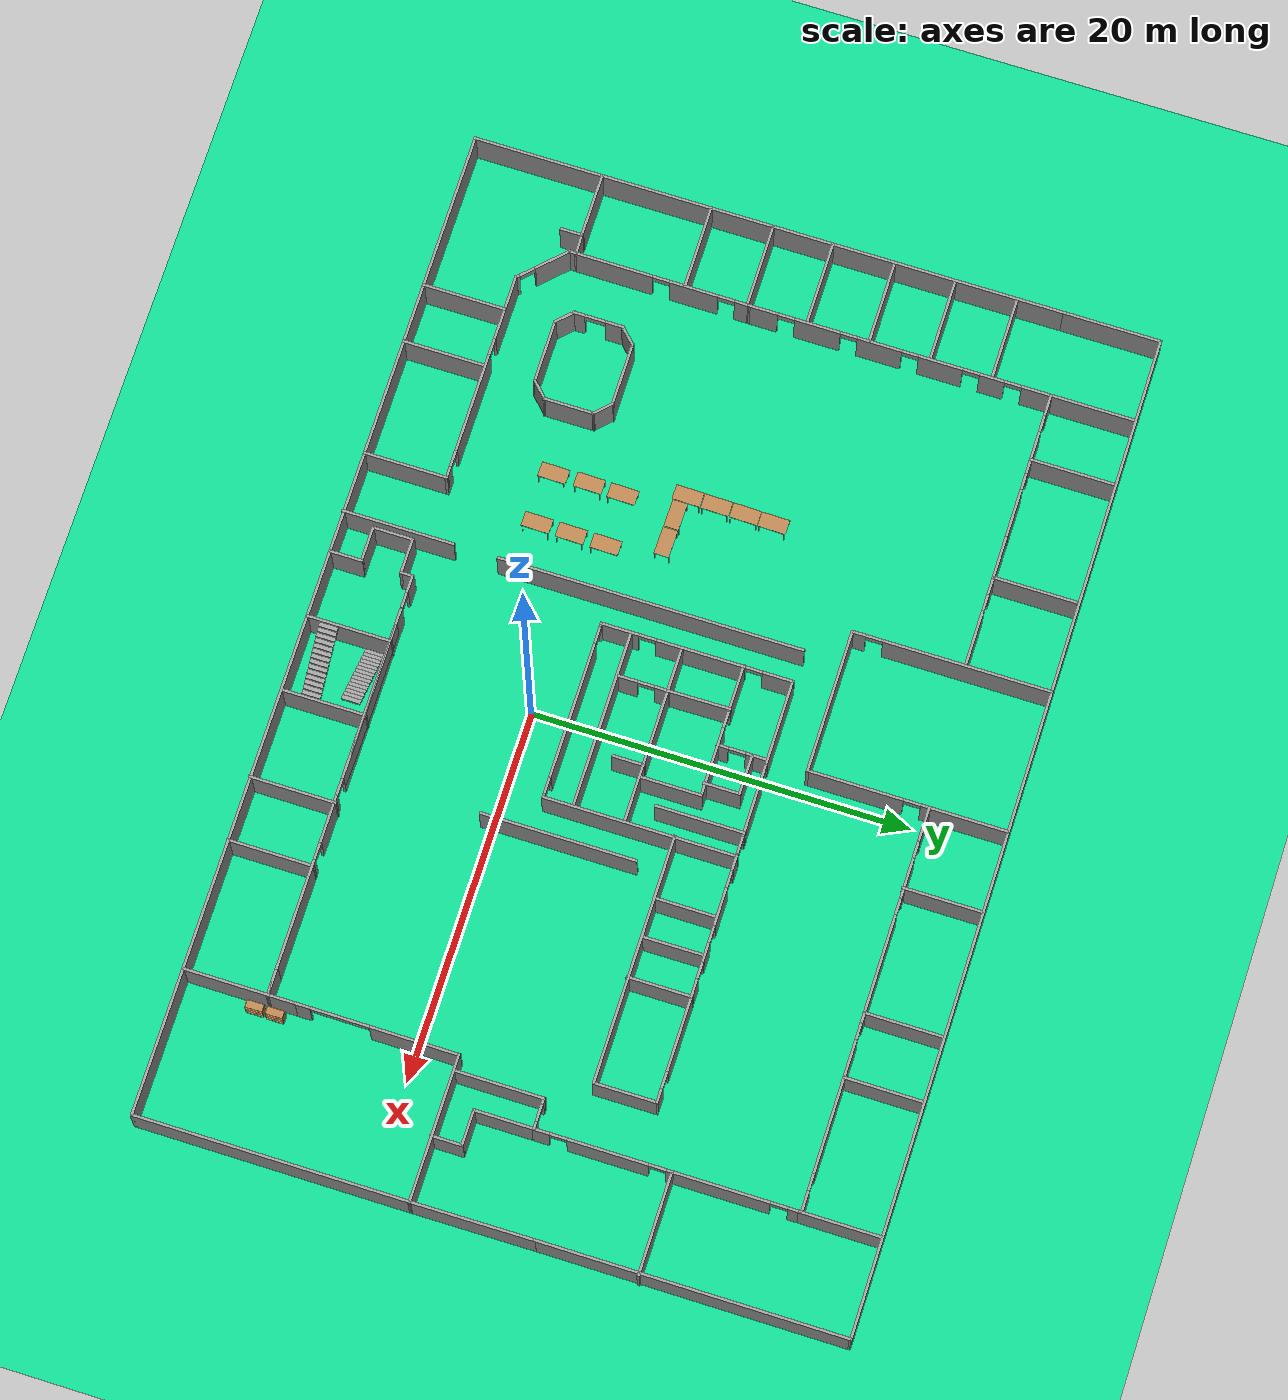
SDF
<sdf version="1.7">
 <world name="default">
  <plugin name="ignition::gazebo::systems::Physics" filename="ignition-gazebo-physics-system"/>
  <plugin name="ignition::gazebo::systems::UserCommands" filename="ignition-gazebo-user-commands-system"/>
  <plugin name="ignition::gazebo::systems::SceneBroadcaster" filename="ignition-gazebo-scene-broadcaster-system"/>
  <plugin filename="ignition-gazebo-sensors-system" name="ignition::gazebo::systems::Sensors">
   <render_engine>ogre2</render_engine>
  </plugin>
  <plugin filename="libignition-gazebo-contact-system.so" name="ignition::gazebo::systems::Contact"/>
  <plugin filename="ignition-gazebo-navsat-system" name="ignition::gazebo::systems::NavSat"/>
  <plugin filename="ignition-gazebo-imu-system" name="ignition::gazebo::systems::Imu"/>
  <light name="sun" type="directional">
   <pose>0 0 10 0 -0 0</pose>
   <diffuse>0.8 0.8 0.8 1</diffuse>
   <specular>0.2 0.2 0.2 1</specular>
   <attenuation>
    <range>1000</range>
    <constant>0.9</constant>
    <linear>0.01</linear>
    <quadratic>0.001</quadratic>
   </attenuation>
   <direction>-0.5 0.1 -0.9</direction>
   <spot><inner_angle>0</inner_angle><outer_angle>0</outer_angle><falloff>0</falloff></spot>
  </light>
  <model name="ground_plane">
   <static>1</static>
   <link name="link">
    <collision name="collision">
     <geometry><plane><normal>0 0 1</normal><size>100 100</size></plane></geometry>
     <surface>
      <contact><ode><kp>1e15</kp><kd>1e13</kd></ode></contact>
      <friction><ode><mu>1.0</mu><mu2>1.0</mu2></ode></friction>
     </surface>
    </collision>
    <visual name="visual">
     <cast_shadows>0</cast_shadows>
     <geometry><plane><normal>0 0 1</normal><size>100 100</size></plane></geometry>
     <material>
      <script><uri>file://media/materials/scripts/gazebo.material</uri><name>Gazebo/Grey</name></script>
      <diffuse>0.05 0.82 0.55 0.8</diffuse>
     </material>
    </visual>
   </link>
  </model>
  <gravity>0 0 -9.8</gravity>
  <magnetic_field>6e-06 2.3e-05 -4.2e-05</magnetic_field>
  <atmosphere type="adiabatic"/>
  <physics name="default_physics" default="0" type="ode">
   <max_step_size>0.100</max_step_size>
   <real_time_factor>1</real_time_factor>
   <real_time_update_rate>1000</real_time_update_rate>
  </physics>
  <scene><ambient>0.4 0.4 0.4 1</ambient><background>0.7 0.7 0.7 1</background><shadows>1</shadows></scene>
  <audio><device>default</device></audio>
  <spherical_coordinates>
   <surface_model>EARTH_WGS84</surface_model>
   <latitude_deg>0</latitude_deg>
   <longitude_deg>0</longitude_deg>
   <elevation>0</elevation>
   <heading_deg>0</heading_deg>
  </spherical_coordinates>
  <model name="circuit_launch">
   <pose>-0.874625 6.32825 0 0 -0 0</pose>
   <link name="Stairs_1">
    <visual name="Stairs_1_Visual_0">
     <pose>3.56304 -17.2142 0.083333 0 -0 -1.5708</pose>
     <geometry><box><size>1 0.233333 0.166667</size></box></geometry>
     <material>
      <script><uri>file://media/materials/scripts/gazebo.material</uri><name>Gazebo/Grey</name></script>
      <ambient>1 1 1 1</ambient>
      <diffuse>1 1 1 1</diffuse>
     </material>
     <meta><layer>0</layer></meta>
    </visual>
    <collision name="Stairs_1_Collision_0">
     <geometry><box><size>1 0.233333 0.166667</size></box></geometry>
     <pose>3.56304 -17.2142 0.083333 0 -0 -1.5708</pose>
    </collision>
    <visual name="Stairs_1_Visual_1">
     <pose>3.32971 -17.2142 0.25 0 -0 -1.5708</pose>
     <geometry><box><size>1 0.233333 0.166667</size></box></geometry>
     <material>
      <script><uri>file://media/materials/scripts/gazebo.material</uri><name>Gazebo/Grey</name></script>
      <ambient>1 1 1 1</ambient>
      <diffuse>1 1 1 1</diffuse>
     </material>
     <meta><layer>0</layer></meta>
    </visual>
    <collision name="Stairs_1_Collision_1">
     <geometry><box><size>1 0.233333 0.166667</size></box></geometry>
     <pose>3.32971 -17.2142 0.25 0 -0 -1.5708</pose>
    </collision>
    <visual name="Stairs_1_Visual_2">
     <pose>3.09638 -17.2142 0.416667 0 -0 -1.5708</pose>
     <geometry><box><size>1 0.233333 0.166667</size></box></geometry>
     <material>
      <script><uri>file://media/materials/scripts/gazebo.material</uri><name>Gazebo/Grey</name></script>
      <ambient>1 1 1 1</ambient>
      <diffuse>1 1 1 1</diffuse>
     </material>
     <meta><layer>0</layer></meta>
    </visual>
    <collision name="Stairs_1_Collision_2">
     <geometry><box><size>1 0.233333 0.166667</size></box></geometry>
     <pose>3.09638 -17.2142 0.416667 0 -0 -1.5708</pose>
    </collision>
    <visual name="Stairs_1_Visual_3">
     <pose>2.86304 -17.2142 0.583333 0 -0 -1.5708</pose>
     <geometry><box><size>1 0.233333 0.166667</size></box></geometry>
     <material>
      <script><uri>file://media/materials/scripts/gazebo.material</uri><name>Gazebo/Grey</name></script>
      <ambient>1 1 1 1</ambient>
      <diffuse>1 1 1 1</diffuse>
     </material>
     <meta><layer>0</layer></meta>
    </visual>
    <collision name="Stairs_1_Collision_3">
     <geometry><box><size>1 0.233333 0.166667</size></box></geometry>
     <pose>2.86304 -17.2142 0.583333 0 -0 -1.5708</pose>
    </collision>
    <visual name="Stairs_1_Visual_4">
     <pose>2.62971 -17.2142 0.75 0 -0 -1.5708</pose>
     <geometry><box><size>1 0.233333 0.166667</size></box></geometry>
     <material>
      <script><uri>file://media/materials/scripts/gazebo.material</uri><name>Gazebo/Grey</name></script>
      <ambient>1 1 1 1</ambient>
      <diffuse>1 1 1 1</diffuse>
     </material>
     <meta><layer>0</layer></meta>
    </visual>
    <collision name="Stairs_1_Collision_4">
     <geometry><box><size>1 0.233333 0.166667</size></box></geometry>
     <pose>2.62971 -17.2142 0.75 0 -0 -1.5708</pose>
    </collision>
    <visual name="Stairs_1_Visual_5">
     <pose>2.39638 -17.2142 0.916667 0 -0 -1.5708</pose>
     <geometry><box><size>1 0.233333 0.166667</size></box></geometry>
     <material>
      <script><uri>file://media/materials/scripts/gazebo.material</uri><name>Gazebo/Grey</name></script>
      <ambient>1 1 1 1</ambient>
      <diffuse>1 1 1 1</diffuse>
     </material>
     <meta><layer>0</layer></meta>
    </visual>
    <collision name="Stairs_1_Collision_5">
     <geometry><box><size>1 0.233333 0.166667</size></box></geometry>
     <pose>2.39638 -17.2142 0.916667 0 -0 -1.5708</pose>
    </collision>
    <visual name="Stairs_1_Visual_6">
     <pose>2.16304 -17.2142 1.08333 0 -0 -1.5708</pose>
     <geometry><box><size>1 0.233333 0.166667</size></box></geometry>
     <material>
      <script><uri>file://media/materials/scripts/gazebo.material</uri><name>Gazebo/Grey</name></script>
      <ambient>1 1 1 1</ambient>
      <diffuse>1 1 1 1</diffuse>
     </material>
     <meta><layer>0</layer></meta>
    </visual>
    <collision name="Stairs_1_Collision_6">
     <geometry><box><size>1 0.233333 0.166667</size></box></geometry>
     <pose>2.16304 -17.2142 1.08333 0 -0 -1.5708</pose>
    </collision>
    <visual name="Stairs_1_Visual_7">
     <pose>1.92971 -17.2142 1.25 0 -0 -1.5708</pose>
     <geometry><box><size>1 0.233333 0.166667</size></box></geometry>
     <material>
      <script><uri>file://media/materials/scripts/gazebo.material</uri><name>Gazebo/Grey</name></script>
      <ambient>1 1 1 1</ambient>
      <diffuse>1 1 1 1</diffuse>
     </material>
     <meta><layer>0</layer></meta>
    </visual>
    <collision name="Stairs_1_Collision_7">
     <geometry><box><size>1 0.233333 0.166667</size></box></geometry>
     <pose>1.92971 -17.2142 1.25 0 -0 -1.5708</pose>
    </collision>
    <visual name="Stairs_1_Visual_8">
     <pose>1.69638 -17.2142 1.41667 0 -0 -1.5708</pose>
     <geometry><box><size>1 0.233333 0.166667</size></box></geometry>
     <material>
      <script><uri>file://media/materials/scripts/gazebo.material</uri><name>Gazebo/Grey</name></script>
      <ambient>1 1 1 1</ambient>
      <diffuse>1 1 1 1</diffuse>
      <diffuse>1 1 1 1</diffuse>
     </material>
     <meta><layer>0</layer></meta>
    </visual>
    <collision name="Stairs_1_Collision_8">
     <geometry><box><size>1 0.233333 0.166667</size></box></geometry>
     <pose>1.69638 -17.2142 1.41667 0 -0 -1.5708</pose>
    </collision>
    <visual name="Stairs_1_Visual_9">
     <pose>1.46304 -17.2142 1.58333 0 -0 -1.5708</pose>
     <geometry><box><size>1 0.233333 0.166667</size></box></geometry>
     <material>
      <script><uri>file://media/materials/scripts/gazebo.material</uri><name>Gazebo/Grey</name></script>
      <ambient>1 1 1 1</ambient>
      <diffuse>1 1 1 1</diffuse>
      <diffuse>1 1 1 1</diffuse>
     </material>
     <meta><layer>0</layer></meta>
    </visual>
    <collision name="Stairs_1_Collision_9">
     <geometry><box><size>1 0.233333 0.166667</size></box></geometry>
     <pose>1.46304 -17.2142 1.58333 0 -0 -1.5708</pose>
    </collision>
    <visual name="Stairs_1_Visual_10">
     <pose>1.22971 -17.2142 1.75 0 -0 -1.5708</pose>
     <geometry><box><size>1 0.233333 0.166667</size></box></geometry>
     <material>
      <script><uri>file://media/materials/scripts/gazebo.material</uri><name>Gazebo/Grey</name></script>
      <ambient>1 1 1 1</ambient>
      <diffuse>1 1 1 1</diffuse>
      <diffuse>1 1 1 1</diffuse>
     </material>
     <meta><layer>0</layer></meta>
    </visual>
    <collision name="Stairs_1_Collision_10">
     <geometry><box><size>1 0.233333 0.166667</size></box></geometry>
     <pose>1.22971 -17.2142 1.75 0 -0 -1.5708</pose>
    </collision>
    <visual name="Stairs_1_Visual_11">
     <pose>0.996375 -17.2142 1.91667 0 -0 -1.5708</pose>
     <geometry><box><size>1 0.233333 0.166667</size></box></geometry>
     <material>
      <script><uri>file://media/materials/scripts/gazebo.material</uri><name>Gazebo/Grey</name></script>
      <ambient>1 1 1 1</ambient>
      <diffuse>1 1 1 1</diffuse>
      <diffuse>1 1 1 1</diffuse>
     </material>
     <meta><layer>0</layer></meta>
    </visual>
    <collision name="Stairs_1_Collision_11">
     <geometry><box><size>1 0.233333 0.166667</size></box></geometry>
     <pose>0.996375 -17.2142 1.91667 0 -0 -1.5708</pose>
    </collision>
    <visual name="Stairs_1_Visual_12">
     <pose>0.763042 -17.2142 2.08333 0 -0 -1.5708</pose>
     <geometry><box><size>1 0.233333 0.166667</size></box></geometry>
     <material>
      <script><uri>file://media/materials/scripts/gazebo.material</uri><name>Gazebo/Grey</name></script>
      <ambient>1 1 1 1</ambient>
      <diffuse>1 1 1 1</diffuse>
      <diffuse>1 1 1 1</diffuse>
     </material>
     <meta><layer>0</layer></meta>
    </visual>
    <collision name="Stairs_1_Collision_12">
     <geometry><box><size>1 0.233333 0.166667</size></box></geometry>
     <pose>0.763042 -17.2142 2.08333 0 -0 -1.5708</pose>
    </collision>
    <visual name="Stairs_1_Visual_13">
     <pose>0.529709 -17.2142 2.25 0 -0 -1.5708</pose>
     <geometry><box><size>1 0.233333 0.166667</size></box></geometry>
     <material>
      <script><uri>file://media/materials/scripts/gazebo.material</uri><name>Gazebo/Grey</name></script>
      <ambient>1 1 1 1</ambient>
      <diffuse>1 1 1 1</diffuse>
      <diffuse>1 1 1 1</diffuse>
     </material>
     <meta><layer>0</layer></meta>
    </visual>
    <collision name="Stairs_1_Collision_13">
     <geometry><box><size>1 0.233333 0.166667</size></box></geometry>
     <pose>0.529709 -17.2142 2.25 0 -0 -1.5708</pose>
    </collision>
    <visual name="Stairs_1_Visual_14">
     <pose>0.296375 -17.2142 2.41667 0 -0 -1.5708</pose>
     <geometry><box><size>1 0.233333 0.166667</size></box></geometry>
     <material>
      <script><uri>file://media/materials/scripts/gazebo.material</uri><name>Gazebo/Grey</name></script>
      <ambient>1 1 1 1</ambient>
      <diffuse>1 1 1 1</diffuse>
      <diffuse>1 1 1 1</diffuse>
     </material>
     <meta><layer>0</layer></meta>
    </visual>
    <collision name="Stairs_1_Collision_14">
     <geometry><box><size>1 0.233333 0.166667</size></box></geometry>
     <pose>0.296375 -17.2142 2.41667 0 -0 -1.5708</pose>
    </collision>
   </link>
   <link name="Stairs_2">
    <visual name="Stairs_2_Visual_0">
     <pose>0.290776 -14.8993 0.083333 0 -0 1.5708</pose>
     <geometry><box><size>1 0.233333 0.166667</size></box></geometry>
     <material>
      <script><uri>file://media/materials/scripts/gazebo.material</uri><name>Gazebo/Grey</name></script>
      <ambient>1 1 1 1</ambient>
      <diffuse>1 1 1 1</diffuse>
      <diffuse>1 1 1 1</diffuse>
     </material>
     <meta><layer>0</layer></meta>
    </visual>
    <collision name="Stairs_2_Collision_0">
     <geometry><box><size>1 0.233333 0.166667</size></box></geometry>
     <pose>0.290776 -14.8993 0.083333 0 -0 1.5708</pose>
    </collision>
    <visual name="Stairs_2_Visual_1">
     <pose>0.524109 -14.8993 0.25 0 -0 1.5708</pose>
     <geometry><box><size>1 0.233333 0.166667</size></box></geometry>
     <material>
      <script><uri>file://media/materials/scripts/gazebo.material</uri><name>Gazebo/Grey</name></script>
      <ambient>1 1 1 1</ambient>
      <diffuse>1 1 1 1</diffuse>
      <diffuse>1 1 1 1</diffuse>
     </material>
     <meta><layer>0</layer></meta>
    </visual>
    <collision name="Stairs_2_Collision_1">
     <geometry><box><size>1 0.233333 0.166667</size></box></geometry>
     <pose>0.524109 -14.8993 0.25 0 -0 1.5708</pose>
    </collision>
    <visual name="Stairs_2_Visual_2">
     <pose>0.757443 -14.8993 0.416667 0 -0 1.5708</pose>
     <geometry><box><size>1 0.233333 0.166667</size></box></geometry>
     <material>
      <script><uri>file://media/materials/scripts/gazebo.material</uri><name>Gazebo/Grey</name></script>
      <ambient>1 1 1 1</ambient>
      <diffuse>1 1 1 1</diffuse>
     </material>
     <meta><layer>0</layer></meta>
    </visual>
    <collision name="Stairs_2_Collision_2">
     <geometry><box><size>1 0.233333 0.166667</size></box></geometry>
     <pose>0.757443 -14.8993 0.416667 0 -0 1.5708</pose>
    </collision>
    <visual name="Stairs_2_Visual_3">
     <pose>0.990776 -14.8993 0.583333 0 -0 1.5708</pose>
     <geometry><box><size>1 0.233333 0.166667</size></box></geometry>
     <material>
      <script><uri>file://media/materials/scripts/gazebo.material</uri><name>Gazebo/Grey</name></script>
      <ambient>1 1 1 1</ambient>
      <diffuse>1 1 1 1</diffuse>
     </material>
     <meta><layer>0</layer></meta>
    </visual>
    <collision name="Stairs_2_Collision_3">
     <geometry><box><size>1 0.233333 0.166667</size></box></geometry>
     <pose>0.990776 -14.8993 0.583333 0 -0 1.5708</pose>
    </collision>
    <visual name="Stairs_2_Visual_4">
     <pose>1.22411 -14.8993 0.75 0 -0 1.5708</pose>
     <geometry><box><size>1 0.233333 0.166667</size></box></geometry>
     <material>
      <script><uri>file://media/materials/scripts/gazebo.material</uri><name>Gazebo/Grey</name></script>
      <ambient>1 1 1 1</ambient>
      <diffuse>1 1 1 1</diffuse>
     </material>
     <meta><layer>0</layer></meta>
    </visual>
    <collision name="Stairs_2_Collision_4">
     <geometry><box><size>1 0.233333 0.166667</size></box></geometry>
     <pose>1.22411 -14.8993 0.75 0 -0 1.5708</pose>
    </collision>
    <visual name="Stairs_2_Visual_5">
     <pose>1.45744 -14.8993 0.916667 0 -0 1.5708</pose>
     <geometry><box><size>1 0.233333 0.166667</size></box></geometry>
     <material>
      <script><uri>file://media/materials/scripts/gazebo.material</uri><name>Gazebo/Grey</name></script>
      <ambient>1 1 1 1</ambient>
      <diffuse>1 1 1 1</diffuse>
     </material>
     <meta><layer>0</layer></meta>
    </visual>
    <collision name="Stairs_2_Collision_5">
     <geometry><box><size>1 0.233333 0.166667</size></box></geometry>
     <pose>1.45744 -14.8993 0.916667 0 -0 1.5708</pose>
    </collision>
    <visual name="Stairs_2_Visual_6">
     <pose>1.69078 -14.8993 1.08333 0 -0 1.5708</pose>
     <geometry><box><size>1 0.233333 0.166667</size></box></geometry>
     <material>
      <script><uri>file://media/materials/scripts/gazebo.material</uri><name>Gazebo/Grey</name></script>
      <ambient>1 1 1 1</ambient>
      <diffuse>1 1 1 1</diffuse>
     </material>
     <meta><layer>0</layer></meta>
    </visual>
    <collision name="Stairs_2_Collision_6">
     <geometry><box><size>1 0.233333 0.166667</size></box></geometry>
     <pose>1.69078 -14.8993 1.08333 0 -0 1.5708</pose>
    </collision>
    <visual name="Stairs_2_Visual_7">
     <pose>1.92411 -14.8993 1.25 0 -0 1.5708</pose>
     <geometry><box><size>1 0.233333 0.166667</size></box></geometry>
     <material>
      <script><uri>file://media/materials/scripts/gazebo.material</uri><name>Gazebo/Grey</name></script>
      <ambient>1 1 1 1</ambient>
      <diffuse>1 1 1 1</diffuse>
     </material>
     <meta><layer>0</layer></meta>
    </visual>
    <collision name="Stairs_2_Collision_7">
     <geometry><box><size>1 0.233333 0.166667</size></box></geometry>
     <pose>1.92411 -14.8993 1.25 0 -0 1.5708</pose>
    </collision>
    <visual name="Stairs_2_Visual_8">
     <pose>2.15744 -14.8993 1.41667 0 -0 1.5708</pose>
     <geometry><box><size>1 0.233333 0.166667</size></box></geometry>
     <material>
      <script><uri>file://media/materials/scripts/gazebo.material</uri><name>Gazebo/Grey</name></script>
      <ambient>1 1 1 1</ambient>
      <diffuse>1 1 1 1</diffuse>
     </material>
     <meta><layer>0</layer></meta>
    </visual>
    <collision name="Stairs_2_Collision_8">
     <geometry><box><size>1 0.233333 0.166667</size></box></geometry>
     <pose>2.15744 -14.8993 1.41667 0 -0 1.5708</pose>
    </collision>
    <visual name="Stairs_2_Visual_9">
     <pose>2.39078 -14.8993 1.58333 0 -0 1.5708</pose>
     <geometry><box><size>1 0.233333 0.166667</size></box></geometry>
     <material>
      <script><uri>file://media/materials/scripts/gazebo.material</uri><name>Gazebo/Grey</name></script>
      <ambient>1 1 1 1</ambient>
      <diffuse>1 1 1 1</diffuse>
     </material>
     <meta><layer>0</layer></meta>
    </visual>
    <collision name="Stairs_2_Collision_9">
     <geometry><box><size>1 0.233333 0.166667</size></box></geometry>
     <pose>2.39078 -14.8993 1.58333 0 -0 1.5708</pose>
    </collision>
    <visual name="Stairs_2_Visual_10">
     <pose>2.62411 -14.8993 1.75 0 -0 1.5708</pose>
     <geometry><box><size>1 0.233333 0.166667</size></box></geometry>
     <material>
      <script><uri>file://media/materials/scripts/gazebo.material</uri><name>Gazebo/Grey</name></script>
      <ambient>1 1 1 1</ambient>
      <diffuse>1 1 1 1</diffuse>
     </material>
     <meta><layer>0</layer></meta>
    </visual>
    <collision name="Stairs_2_Collision_10">
     <geometry><box><size>1 0.233333 0.166667</size></box></geometry>
     <pose>2.62411 -14.8993 1.75 0 -0 1.5708</pose>
    </collision>
    <visual name="Stairs_2_Visual_11">
     <pose>2.85744 -14.8993 1.91667 0 -0 1.5708</pose>
     <geometry><box><size>1 0.233333 0.166667</size></box></geometry>
     <material>
      <script><uri>file://media/materials/scripts/gazebo.material</uri><name>Gazebo/Grey</name></script>
      <ambient>1 1 1 1</ambient>
      <diffuse>1 1 1 1</diffuse>
     </material>
     <meta><layer>0</layer></meta>
    </visual>
    <collision name="Stairs_2_Collision_11">
     <geometry><box><size>1 0.233333 0.166667</size></box></geometry>
     <pose>2.85744 -14.8993 1.91667 0 -0 1.5708</pose>
    </collision>
    <visual name="Stairs_2_Visual_12">
     <pose>3.09078 -14.8993 2.08333 0 -0 1.5708</pose>
     <geometry><box><size>1 0.233333 0.166667</size></box></geometry>
     <material>
      <script><uri>file://media/materials/scripts/gazebo.material</uri><name>Gazebo/Grey</name></script>
      <ambient>1 1 1 1</ambient>
      <diffuse>1 1 1 1</diffuse>
     </material>
     <meta><layer>0</layer></meta>
    </visual>
    <collision name="Stairs_2_Collision_12">
     <geometry><box><size>1 0.233333 0.166667</size></box></geometry>
     <pose>3.09078 -14.8993 2.08333 0 -0 1.5708</pose>
    </collision>
    <visual name="Stairs_2_Visual_13">
     <pose>3.32411 -14.8993 2.25 0 -0 1.5708</pose>
     <geometry><box><size>1 0.233333 0.166667</size></box></geometry>
     <material>
      <script><uri>file://media/materials/scripts/gazebo.material</uri><name>Gazebo/Grey</name></script>
      <ambient>1 1 1 1</ambient>
      <diffuse>1 1 1 1</diffuse>
     </material>
     <meta><layer>0</layer></meta>
    </visual>
    <collision name="Stairs_2_Collision_13">
     <geometry><box><size>1 0.233333 0.166667</size></box></geometry>
     <pose>3.32411 -14.8993 2.25 0 -0 1.5708</pose>
    </collision>
    <visual name="Stairs_2_Visual_14">
     <pose>3.55744 -14.8993 2.41667 0 -0 1.5708</pose>
     <geometry><box><size>1 0.233333 0.166667</size></box></geometry>
     <material>
      <script><uri>file://media/materials/scripts/gazebo.material</uri><name>Gazebo/Grey</name></script>
      <ambient>1 1 1 1</ambient>
      <diffuse>1 1 1 1</diffuse>
     </material>
     <meta><layer>0</layer></meta>
    </visual>
    <collision name="Stairs_2_Collision_14">
     <geometry><box><size>1 0.233333 0.166667</size></box></geometry>
     <pose>3.55744 -14.8993 2.41667 0 -0 1.5708</pose>
    </collision>
   </link>
   <link name="Wall_100">
    <pose>21.684 10.9599 0 0 -0 1.5708</pose>
    <visual name="Wall_100_Visual_0">
     <pose>-0.787773 0 1.25 0 -0 0</pose>
     <geometry><box><size>5.12125 0.15 2.5</size></box></geometry>
     <material>
      <script><uri>file://media/materials/scripts/gazebo.material</uri><name>Gazebo/Grey</name></script>
      <ambient>1 1 1 1</ambient>
      <diffuse>1 1 1 1</diffuse>
     </material>
     <meta><layer>0</layer></meta>
    </visual>
    <collision name="Wall_100_Collision_0">
     <geometry><box><size>5.12125 0.15 2.5</size></box></geometry>
     <pose>-0.787773 0 1.25 0 -0 0</pose>
    </collision>
    <visual name="Wall_100_Visual_1">
     <pose>3.01063 0 1.25 0 -0 0</pose>
     <geometry><box><size>0.675545 0.15 2.5</size></box></geometry>
     <material>
      <script><uri>file://media/materials/scripts/gazebo.material</uri><name>Gazebo/Grey</name></script>
      <ambient>1 1 1 1</ambient>
      <diffuse>1 1 1 1</diffuse>
     </material>
     <meta><layer>0</layer></meta>
    </visual>
    <collision name="Wall_100_Collision_1">
     <geometry><box><size>0.675545 0.15 2.5</size></box></geometry>
     <pose>3.01063 0 1.25 0 -0 0</pose>
    </collision>
    <visual name="Wall_100_Visual_2">
     <pose>2.22286 0 2.25 0 -0 0</pose>
     <geometry><box><size>0.9 0.15 0.5</size></box></geometry>
     <material>
      <script><uri>file://media/materials/scripts/gazebo.material</uri><name>Gazebo/Grey</name></script>
      <ambient>1 1 1 1</ambient>
      <diffuse>1 1 1 1</diffuse>
     </material>
     <meta><layer>0</layer></meta>
    </visual>
    <collision name="Wall_100_Collision_2">
     <geometry><box><size>0.9 0.15 0.5</size></box></geometry>
     <pose>2.22286 0 2.25 0 -0 0</pose>
    </collision>
   </link>
   <link name="Wall_107">
    <pose>-18.6032 13.9124 0 0 -0 3.14159</pose>
    <visual name="Wall_107_Visual_0">
     <pose>-2.69056 0 1.25 0 -0 0</pose>
     <geometry><box><size>2.61888 0.15 2.5</size></box></geometry>
     <material>
      <script><uri>file://media/materials/scripts/gazebo.material</uri><name>Gazebo/Grey</name></script>
      <ambient>1 1 1 1</ambient>
      <diffuse>1 1 1 1</diffuse>
     </material>
     <meta><layer>0</layer></meta>
    </visual>
    <collision name="Wall_107_Collision_0">
     <geometry><box><size>2.61888 0.15 2.5</size></box></geometry>
     <pose>-2.69056 0 1.25 0 -0 0</pose>
    </collision>
    <visual name="Wall_107_Visual_1">
     <pose>0.710992 0 1.25 0 -0 0</pose>
     <geometry><box><size>2.38423 0.15 2.5</size></box></geometry>
     <material>
      <script><uri>file://media/materials/scripts/gazebo.material</uri><name>Gazebo/Grey</name></script>
      <ambient>1 1 1 1</ambient>
      <diffuse>1 1 1 1</diffuse>
     </material>
     <meta><layer>0</layer></meta>
    </visual>
    <collision name="Wall_107_Collision_1">
     <geometry><box><size>2.38423 0.15 2.5</size></box></geometry>
     <pose>0.710992 0 1.25 0 -0 0</pose>
    </collision>
    <visual name="Wall_107_Visual_2">
     <pose>3.40155 0 1.25 0 -0 0</pose>
     <geometry><box><size>1.19689 0.15 2.5</size></box></geometry>
     <material>
      <script><uri>file://media/materials/scripts/gazebo.material</uri><name>Gazebo/Grey</name></script>
      <ambient>1 1 1 1</ambient>
      <diffuse>1 1 1 1</diffuse>
     </material>
     <meta><layer>0</layer></meta>
    </visual>
    <collision name="Wall_107_Collision_2">
     <geometry><box><size>1.19689 0.15 2.5</size></box></geometry>
     <pose>3.40155 0 1.25 0 -0 0</pose>
    </collision>
    <visual name="Wall_107_Visual_3">
     <pose>-0.931122 0 2.25 0 -0 0</pose>
     <geometry><box><size>0.9 0.15 0.5</size></box></geometry>
     <material>
      <script><uri>file://media/materials/scripts/gazebo.material</uri><name>Gazebo/Grey</name></script>
      <ambient>1 1 1 1</ambient>
      <diffuse>1 1 1 1</diffuse>
     </material>
     <meta><layer>0</layer></meta>
    </visual>
    <collision name="Wall_107_Collision_3">
     <geometry><box><size>0.9 0.15 0.5</size></box></geometry>
     <pose>-0.931122 0 2.25 0 -0 0</pose>
    </collision>
    <visual name="Wall_107_Visual_4">
     <pose>2.35311 0 2.25 0 -0 0</pose>
     <geometry><box><size>0.9 0.15 0.5</size></box></geometry>
     <material>
      <script><uri>file://media/materials/scripts/gazebo.material</uri><name>Gazebo/Grey</name></script>
      <ambient>1 1 1 1</ambient>
      <diffuse>1 1 1 1</diffuse>
     </material>
     <meta><layer>0</layer></meta>
    </visual>
    <collision name="Wall_107_Collision_4">
     <geometry><box><size>0.9 0.15 0.5</size></box></geometry>
     <pose>2.35311 0 2.25 0 -0 0</pose>
    </collision>
   </link>
   <link name="Wall_111">
    <pose>-22.5282 5.86241 0 0 -0 -1.5708</pose>
    <visual name="Wall_111_Visual_0">
     <pose>-7.31172 0 1.25 0 -0 0</pose>
     <geometry><box><size>1.62655 0.15 2.5</size></box></geometry>
     <material>
      <script><uri>file://media/materials/scripts/gazebo.material</uri><name>Gazebo/Grey</name></script>
      <ambient>1 1 1 1</ambient>
      <diffuse>1 1 1 1</diffuse>
     </material>
     <meta><layer>0</layer></meta>
    </visual>
    <collision name="Wall_111_Collision_0">
     <geometry><box><size>1.62655 0.15 2.5</size></box></geometry>
     <pose>-7.31172 0 1.25 0 -0 0</pose>
    </collision>
    <visual name="Wall_111_Visual_1">
     <pose>-4.93124 0 1.25 0 -0 0</pose>
     <geometry><box><size>1.33442 0.15 2.5</size></box></geometry>
     <material>
      <script><uri>file://media/materials/scripts/gazebo.material</uri><name>Gazebo/Grey</name></script>
      <ambient>1 1 1 1</ambient>
      <diffuse>1 1 1 1</diffuse>
     </material>
     <meta><layer>0</layer></meta>
    </visual>
    <collision name="Wall_111_Collision_1">
     <geometry><box><size>1.33442 0.15 2.5</size></box></geometry>
     <pose>-4.93124 0 1.25 0 -0 0</pose>
    </collision>
    <visual name="Wall_111_Visual_2">
     <pose>-2.19142 0 1.25 0 -0 0</pose>
     <geometry><box><size>2.34522 0.15 2.5</size></box></geometry>
     <material>
      <script><uri>file://media/materials/scripts/gazebo.material</uri><name>Gazebo/Grey</name></script>
      <ambient>1 1 1 1</ambient>
      <diffuse>1 1 1 1</diffuse>
     </material>
     <meta><layer>0</layer></meta>
    </visual>
    <collision name="Wall_111_Collision_2">
     <geometry><box><size>2.34522 0.15 2.5</size></box></geometry>
     <pose>-2.19142 0 1.25 0 -0 0</pose>
    </collision>
    <visual name="Wall_111_Visual_3">
     <pose>1.0671 0 1.25 0 -0 0</pose>
     <geometry><box><size>2.37182 0.15 2.5</size></box></geometry>
     <material>
      <script><uri>file://media/materials/scripts/gazebo.material</uri><name>Gazebo/Grey</name></script>
      <ambient>1 1 1 1</ambient>
      <diffuse>1 1 1 1</diffuse>
     </material>
     <meta><layer>0</layer></meta>
    </visual>
    <collision name="Wall_111_Collision_3">
     <geometry><box><size>2.37182 0.15 2.5</size></box></geometry>
     <pose>1.0671 0 1.25 0 -0 0</pose>
    </collision>
    <visual name="Wall_111_Visual_4">
     <pose>4.37883 0 1.25 0 -0 0</pose>
     <geometry><box><size>2.45162 0.15 2.5</size></box></geometry>
     <material>
      <script><uri>file://media/materials/scripts/gazebo.material</uri><name>Gazebo/Grey</name></script>
      <ambient>1 1 1 1</ambient>
      <diffuse>1 1 1 1</diffuse>
     </material>
     <meta><layer>0</layer></meta>
    </visual>
    <collision name="Wall_111_Collision_4">
     <geometry><box><size>2.45162 0.15 2.5</size></box></geometry>
     <pose>4.37883 0 1.25 0 -0 0</pose>
    </collision>
    <visual name="Wall_111_Visual_5">
     <pose>7.31482 0 1.25 0 -0 0</pose>
     <geometry><box><size>1.62036 0.15 2.5</size></box></geometry>
     <material>
      <script><uri>file://media/materials/scripts/gazebo.material</uri><name>Gazebo/Grey</name></script>
      <ambient>1 1 1 1</ambient>
      <diffuse>1 1 1 1</diffuse>
     </material>
     <meta><layer>0</layer></meta>
    </visual>
    <collision name="Wall_111_Collision_5">
     <geometry><box><size>1.62036 0.15 2.5</size></box></geometry>
     <pose>7.31482 0 1.25 0 -0 0</pose>
    </collision>
    <visual name="Wall_111_Visual_6">
     <pose>-6.04845 0 2.25 0 -0 0</pose>
     <geometry><box><size>0.9 0.15 0.5</size></box></geometry>
     <material>
      <script><uri>file://media/materials/scripts/gazebo.material</uri><name>Gazebo/Grey</name></script>
      <ambient>1 1 1 1</ambient>
      <diffuse>1 1 1 1</diffuse>
     </material>
     <meta><layer>0</layer></meta>
    </visual>
    <collision name="Wall_111_Collision_6">
     <geometry><box><size>0.9 0.15 0.5</size></box></geometry>
     <pose>-6.04845 0 2.25 0 -0 0</pose>
    </collision>
    <visual name="Wall_111_Visual_7">
     <pose>-3.81403 0 2.25 0 -0 0</pose>
     <geometry><box><size>0.9 0.15 0.5</size></box></geometry>
     <material>
      <script><uri>file://media/materials/scripts/gazebo.material</uri><name>Gazebo/Grey</name></script>
      <ambient>1 1 1 1</ambient>
      <diffuse>1 1 1 1</diffuse>
     </material>
     <meta><layer>0</layer></meta>
    </visual>
    <collision name="Wall_111_Collision_7">
     <geometry><box><size>0.9 0.15 0.5</size></box></geometry>
     <pose>-3.81403 0 2.25 0 -0 0</pose>
    </collision>
    <visual name="Wall_111_Visual_8">
     <pose>-0.568808 0 2.25 0 -0 0</pose>
     <geometry><box><size>0.9 0.15 0.5</size></box></geometry>
     <material>
      <script><uri>file://media/materials/scripts/gazebo.material</uri><name>Gazebo/Grey</name></script>
      <ambient>1 1 1 1</ambient>
      <diffuse>1 1 1 1</diffuse>
     </material>
     <meta><layer>0</layer></meta>
    </visual>
    <collision name="Wall_111_Collision_8">
     <geometry><box><size>0.9 0.15 0.5</size></box></geometry>
     <pose>-0.568808 0 2.25 0 -0 0</pose>
    </collision>
    <visual name="Wall_111_Visual_9">
     <pose>2.70302 0 2.25 0 -0 0</pose>
     <geometry><box><size>0.9 0.15 0.5</size></box></geometry>
     <material>
      <script><uri>file://media/materials/scripts/gazebo.material</uri><name>Gazebo/Grey</name></script>
      <ambient>1 1 1 1</ambient>
      <diffuse>1 1 1 1</diffuse>
     </material>
     <meta><layer>0</layer></meta>
    </visual>
    <collision name="Wall_111_Collision_9">
     <geometry><box><size>0.9 0.15 0.5</size></box></geometry>
     <pose>2.70302 0 2.25 0 -0 0</pose>
    </collision>
    <visual name="Wall_111_Visual_10">
     <pose>6.05464 0 2.25 0 -0 0</pose>
     <geometry><box><size>0.9 0.15 0.5</size></box></geometry>
     <material>
      <script><uri>file://media/materials/scripts/gazebo.material</uri><name>Gazebo/Grey</name></script>
      <ambient>1 1 1 1</ambient>
      <diffuse>1 1 1 1</diffuse>
     </material>
     <meta><layer>0</layer></meta>
    </visual>
    <collision name="Wall_111_Collision_10">
     <geometry><box><size>0.9 0.15 0.5</size></box></geometry>
     <pose>6.05464 0 2.25 0 -0 0</pose>
    </collision>
   </link>
   <link name="Wall_113">
    <pose>-22.548 -6.83655 0 0 -0 -1.57507</pose>
    <visual name="Wall_113_Visual_0">
     <pose>-4.29939 0 1.25 0 -0 0</pose>
     <geometry><box><size>0.849233 0.15 2.5</size></box></geometry>
     <material>
      <script><uri>file://media/materials/scripts/gazebo.material</uri><name>Gazebo/Grey</name></script>
      <ambient>1 1 1 1</ambient>
      <diffuse>1 1 1 1</diffuse>
     </material>
     <meta><layer>0</layer></meta>
    </visual>
    <collision name="Wall_113_Collision_0">
     <geometry><box><size>0.849233 0.15 2.5</size></box></geometry>
     <pose>-4.29939 0 1.25 0 -0 0</pose>
    </collision>
    <visual name="Wall_113_Visual_1">
     <pose>-1.67683 0 1.25 0 -0 0</pose>
     <geometry><box><size>2.59588 0.15 2.5</size></box></geometry>
     <material>
      <script><uri>file://media/materials/scripts/gazebo.material</uri><name>Gazebo/Grey</name></script>
      <ambient>1 1 1 1</ambient>
      <diffuse>1 1 1 1</diffuse>
     </material>
     <meta><layer>0</layer></meta>
    </visual>
    <collision name="Wall_113_Collision_1">
     <geometry><box><size>2.59588 0.15 2.5</size></box></geometry>
     <pose>-1.67683 0 1.25 0 -0 0</pose>
    </collision>
    <visual name="Wall_113_Visual_2">
     <pose>2.62255 0 1.25 0 -0 0</pose>
     <geometry><box><size>4.2029 0.15 2.5</size></box></geometry>
     <material>
      <script><uri>file://media/materials/scripts/gazebo.material</uri><name>Gazebo/Grey</name></script>
      <ambient>1 1 1 1</ambient>
      <diffuse>1 1 1 1</diffuse>
     </material>
     <meta><layer>0</layer></meta>
    </visual>
    <collision name="Wall_113_Collision_2">
     <geometry><box><size>4.2029 0.15 2.5</size></box></geometry>
     <pose>2.62255 0 1.25 0 -0 0</pose>
    </collision>
    <visual name="Wall_113_Visual_3">
     <pose>-3.42477 0 2.25 0 -0 0</pose>
     <geometry><box><size>0.9 0.15 0.5</size></box></geometry>
     <material>
      <script><uri>file://media/materials/scripts/gazebo.material</uri><name>Gazebo/Grey</name></script>
      <ambient>1 1 1 1</ambient>
      <diffuse>1 1 1 1</diffuse>
     </material>
     <meta><layer>0</layer></meta>
    </visual>
    <collision name="Wall_113_Collision_3">
     <geometry><box><size>0.9 0.15 0.5</size></box></geometry>
     <pose>-3.42477 0 2.25 0 -0 0</pose>
    </collision>
    <visual name="Wall_113_Visual_4">
     <pose>0.071105 0 2.25 0 -0 0</pose>
     <geometry><box><size>0.9 0.15 0.5</size></box></geometry>
     <material>
      <script><uri>file://media/materials/scripts/gazebo.material</uri><name>Gazebo/Grey</name></script>
      <ambient>1 1 1 1</ambient>
      <diffuse>1 1 1 1</diffuse>
     </material>
     <meta><layer>0</layer></meta>
    </visual>
    <collision name="Wall_113_Collision_4">
     <geometry><box><size>0.9 0.15 0.5</size></box></geometry>
     <pose>0.071105 0 2.25 0 -0 0</pose>
    </collision>
   </link>
   <link name="Wall_115">
    <collision name="Wall_115_Collision">
     <geometry><box><size>3.5 0.15 2.5</size></box></geometry>
     <pose>0 0 1.25 0 -0 0</pose>
    </collision>
    <visual name="Wall_115_Visual">
     <pose>0 0 1.25 0 -0 0</pose>
     <geometry><box><size>3.5 0.15 2.5</size></box></geometry>
     <material>
      <script><uri>file://media/materials/scripts/gazebo.material</uri><name>Gazebo/Grey</name></script>
      <ambient>1 1 1 1</ambient>
      <diffuse>1 1 1 1</diffuse>
     </material>
     <meta><layer>0</layer></meta>
    </visual>
    <pose>-17.0124 -7.21468 0 0 -0 0</pose>
   </link>
   <link name="Wall_116">
    <collision name="Wall_116_Collision">
     <geometry><box><size>1.25 0.15 2.5</size></box></geometry>
     <pose>0 0 1.25 0 -0 0</pose>
    </collision>
    <visual name="Wall_116_Visual">
     <pose>0 0 1.25 0 -0 0</pose>
     <geometry><box><size>1.25 0.15 2.5</size></box></geometry>
     <material>
      <script><uri>file://media/materials/scripts/gazebo.material</uri><name>Gazebo/Grey</name></script>
      <ambient>1 1 1 1</ambient>
      <diffuse>1 1 1 1</diffuse>
     </material>
     <meta><layer>0</layer></meta>
    </visual>
    <pose>-14.9485 -7.60359 0 0 -0 -0.785398</pose>
   </link>
   <link name="Wall_117">
    <collision name="Wall_117_Collision">
     <geometry><box><size>2.75 0.15 2.5</size></box></geometry>
     <pose>0 0 1.25 0 -0 0</pose>
    </collision>
    <visual name="Wall_117_Visual">
     <pose>0 0 1.25 0 -0 0</pose>
     <geometry><box><size>2.75 0.15 2.5</size></box></geometry>
     <material>
      <script><uri>file://media/materials/scripts/gazebo.material</uri><name>Gazebo/Grey</name></script>
      <ambient>1 1 1 1</ambient>
      <diffuse>1 1 1 1</diffuse>
     </material>
     <meta><layer>0</layer></meta>
    </visual>
    <pose>-14.5595 -9.2925 0 0 -0 -1.5708</pose>
   </link>
   <link name="Wall_118">
    <collision name="Wall_118_Collision">
     <geometry><box><size>1.25 0.15 2.5</size></box></geometry>
     <pose>0 0 1.25 0 -0 0</pose>
    </collision>
    <visual name="Wall_118_Visual">
     <pose>0 0 1.25 0 -0 0</pose>
     <geometry><box><size>1.25 0.15 2.5</size></box></geometry>
     <material>
      <script><uri>file://media/materials/scripts/gazebo.material</uri><name>Gazebo/Grey</name></script>
      <ambient>1 1 1 1</ambient>
      <diffuse>1 1 1 1</diffuse>
     </material>
     <meta><layer>0</layer></meta>
    </visual>
    <pose>-14.9485 -10.9814 0 0 -0 -2.35619</pose>
   </link>
   <link name="Wall_119">
    <collision name="Wall_119_Collision">
     <geometry><box><size>3.5 0.15 2.5</size></box></geometry>
     <pose>0 0 1.25 0 -0 0</pose>
    </collision>
    <visual name="Wall_119_Visual">
     <pose>0 0 1.25 0 -0 0</pose>
     <geometry><box><size>3.5 0.15 2.5</size></box></geometry>
     <material>
      <script><uri>file://media/materials/scripts/gazebo.material</uri><name>Gazebo/Grey</name></script>
      <ambient>1 1 1 1</ambient>
      <diffuse>1 1 1 1</diffuse>
     </material>
     <meta><layer>0</layer></meta>
    </visual>
    <pose>-17.0124 -11.3703 0 0 -0 3.14159</pose>
   </link>
   <link name="Wall_12">
    <collision name="Wall_12_Collision">
     <geometry><box><size>10.25 0.15 2.5</size></box></geometry>
     <pose>0 0 1.25 0 -0 0</pose>
    </collision>
    <visual name="Wall_12_Visual">
     <pose>0 0 1.25 0 -0 0</pose>
     <geometry><box><size>10.25 0.15 2.5</size></box></geometry>
     <material>
      <script><uri>file://media/materials/scripts/gazebo.material</uri><name>Gazebo/Grey</name></script>
      <ambient>1 1 1 1</ambient>
      <diffuse>1 1 1 1</diffuse>
     </material>
     <meta><layer>0</layer></meta>
    </visual>
    <pose>5.48338 0.868521 0 0 -0 1.5708</pose>
   </link>
   <link name="Wall_120">
    <collision name="Wall_120_Collision">
     <geometry><box><size>1.25 0.15 2.5</size></box></geometry>
     <pose>0 0 1.25 0 -0 0</pose>
    </collision>
    <visual name="Wall_120_Visual">
     <pose>0 0 1.25 0 -0 0</pose>
     <geometry><box><size>1.25 0.15 2.5</size></box></geometry>
     <material>
      <script><uri>file://media/materials/scripts/gazebo.material</uri><name>Gazebo/Grey</name></script>
      <ambient>1 1 1 1</ambient>
      <diffuse>1 1 1 1</diffuse>
     </material>
     <meta><layer>0</layer></meta>
    </visual>
    <pose>-19.0763 -10.9814 0 0 -0 2.35619</pose>
   </link>
   <link name="Wall_121">
    <pose>-19.4652 -9.2925 0 0 -0 1.5708</pose>
    <visual name="Wall_121_Visual_0">
     <pose>-1.04498 0 1.25 0 -0 0</pose>
     <geometry><box><size>0.66004 0.15 2.5</size></box></geometry>
     <material>
      <script><uri>file://media/materials/scripts/gazebo.material</uri><name>Gazebo/Grey</name></script>
      <ambient>1 1 1 1</ambient>
      <diffuse>1 1 1 1</diffuse>
     </material>
     <meta><layer>0</layer></meta>
    </visual>
    <collision name="Wall_121_Collision_0">
     <geometry><box><size>0.66004 0.15 2.5</size></box></geometry>
     <pose>-1.04498 0 1.25 0 -0 0</pose>
    </collision>
    <visual name="Wall_121_Visual_1">
     <pose>0.884108 0 1.25 0 -0 0</pose>
     <geometry><box><size>0.981785 0.15 2.5</size></box></geometry>
     <material>
      <script><uri>file://media/materials/scripts/gazebo.material</uri><name>Gazebo/Grey</name></script>
      <ambient>1 1 1 1</ambient>
      <diffuse>1 1 1 1</diffuse>
     </material>
     <meta><layer>0</layer></meta>
    </visual>
    <collision name="Wall_121_Collision_1">
     <geometry><box><size>0.981785 0.15 2.5</size></box></geometry>
     <pose>0.884108 0 1.25 0 -0 0</pose>
    </collision>
    <visual name="Wall_121_Visual_2">
     <pose>-0.160872 0 2.25 0 -0 0</pose>
     <geometry><box><size>1.10817 0.15 0.5</size></box></geometry>
     <material>
      <script><uri>file://media/materials/scripts/gazebo.material</uri><name>Gazebo/Grey</name></script>
      <ambient>1 1 1 1</ambient>
      <diffuse>1 1 1 1</diffuse>
     </material>
     <meta><layer>0</layer></meta>
    </visual>
    <collision name="Wall_121_Collision_2">
     <geometry><box><size>1.10817 0.15 0.5</size></box></geometry>
     <pose>-0.160872 0 2.25 0 -0 0</pose>
    </collision>
   </link>
   <link name="Wall_122">
    <collision name="Wall_122_Collision">
     <geometry><box><size>1.25 0.15 2.5</size></box></geometry>
     <pose>0 0 1.25 0 -0 0</pose>
    </collision>
    <visual name="Wall_122_Visual">
     <pose>0 0 1.25 0 -0 0</pose>
     <geometry><box><size>1.25 0.15 2.5</size></box></geometry>
     <material>
      <script><uri>file://media/materials/scripts/gazebo.material</uri><name>Gazebo/Grey</name></script>
      <ambient>1 1 1 1</ambient>
      <diffuse>1 1 1 1</diffuse>
     </material>
     <meta><layer>0</layer></meta>
    </visual>
    <pose>-19.0763 -7.60359 0 0 -0 0.785398</pose>
   </link>
   <link name="Wall_124">
    <collision name="Wall_124_Collision">
     <geometry><box><size>16.25 0.15 2.5</size></box></geometry>
     <pose>0 0 1.25 0 -0 0</pose>
    </collision>
    <visual name="Wall_124_Visual">
     <pose>0 0 1.25 0 -0 0</pose>
     <geometry><box><size>16.25 0.15 2.5</size></box></geometry>
     <material>
      <script><uri>file://media/materials/scripts/gazebo.material</uri><name>Gazebo/Grey</name></script>
      <ambient>1 1 1 1</ambient>
      <diffuse>1 1 1 1</diffuse>
     </material>
     <meta><layer>0</layer></meta>
    </visual>
    <pose>-5.75967 -2.14165 0 0 -0 -1.5708</pose>
   </link>
   <link name="Wall_126">
    <collision name="Wall_126_Collision">
     <geometry><box><size>6 0.15 2.5</size></box></geometry>
     <pose>0 0 1.25 0 -0 0</pose>
    </collision>
    <visual name="Wall_126_Visual">
     <pose>0 0 1.25 0 -0 0</pose>
     <geometry><box><size>6 0.15 2.5</size></box></geometry>
     <material>
      <script><uri>file://media/materials/scripts/gazebo.material</uri><name>Gazebo/Grey</name></script>
      <ambient>1 1 1 1</ambient>
      <diffuse>1 1 1 1</diffuse>
     </material>
     <meta><layer>0</layer></meta>
    </visual>
    <pose>-5.76615 -15.5406 0 0 -0 -1.5708</pose>
   </link>
   <link name="Wall_13">
    <pose>0.725889 5.90411 0 0 -0 -3.13856</pose>
    <visual name="Wall_13_Visual_0">
     <pose>-4.71281 0 1.25 0 -0 0</pose>
     <geometry><box><size>0.239451 0.15 2.5</size></box></geometry>
     <material>
      <script><uri>file://media/materials/scripts/gazebo.material</uri><name>Gazebo/Grey</name></script>
      <ambient>1 1 1 1</ambient>
      <diffuse>1 1 1 1</diffuse>
     </material>
     <meta><layer>0</layer></meta>
    </visual>
    <collision name="Wall_13_Collision_0">
     <geometry><box><size>0.239451 0.15 2.5</size></box></geometry>
     <pose>-4.71281 0 1.25 0 -0 0</pose>
    </collision>
    <visual name="Wall_13_Visual_1">
     <pose>-2.18096 0 1.25 0 -0 0</pose>
     <geometry><box><size>3.02425 0.15 2.5</size></box></geometry>
     <material>
      <script><uri>file://media/materials/scripts/gazebo.material</uri><name>Gazebo/Grey</name></script>
      <ambient>1 1 1 1</ambient>
      <diffuse>1 1 1 1</diffuse>
     </material>
     <meta><layer>0</layer></meta>
    </visual>
    <collision name="Wall_13_Collision_1">
     <geometry><box><size>3.02425 0.15 2.5</size></box></geometry>
     <pose>-2.18096 0 1.25 0 -0 0</pose>
    </collision>
    <visual name="Wall_13_Visual_2">
     <pose>2.53185 0 1.25 0 -0 0</pose>
     <geometry><box><size>4.60137 0.15 2.5</size></box></geometry>
     <material>
      <script><uri>file://media/materials/scripts/gazebo.material</uri><name>Gazebo/Grey</name></script>
      <ambient>1 1 1 1</ambient>
      <diffuse>1 1 1 1</diffuse>
     </material>
     <meta><layer>0</layer></meta>
    </visual>
    <collision name="Wall_13_Collision_2">
     <geometry><box><size>4.60137 0.15 2.5</size></box></geometry>
     <pose>2.53185 0 1.25 0 -0 0</pose>
    </collision>
    <visual name="Wall_13_Visual_3">
     <pose>-4.14309 0 2.25 0 -0 0</pose>
     <geometry><box><size>0.9 0.15 0.5</size></box></geometry>
     <material>
      <script><uri>file://media/materials/scripts/gazebo.material</uri><name>Gazebo/Grey</name></script>
      <ambient>1 1 1 1</ambient>
      <diffuse>1 1 1 1</diffuse>
     </material>
     <meta><layer>0</layer></meta>
    </visual>
    <collision name="Wall_13_Collision_3">
     <geometry><box><size>0.9 0.15 0.5</size></box></geometry>
     <pose>-4.14309 0 2.25 0 -0 0</pose>
    </collision>
    <visual name="Wall_13_Visual_4">
     <pose>-0.218831 0 2.25 0 -0 0</pose>
     <geometry><box><size>0.9 0.15 0.5</size></box></geometry>
     <material>
      <script><uri>file://media/materials/scripts/gazebo.material</uri><name>Gazebo/Grey</name></script>
      <ambient>1 1 1 1</ambient>
      <diffuse>1 1 1 1</diffuse>
     </material>
     <meta><layer>0</layer></meta>
    </visual>
    <collision name="Wall_13_Collision_4">
     <geometry><box><size>0.9 0.15 0.5</size></box></geometry>
     <pose>-0.218831 0 2.25 0 -0 0</pose>
    </collision>
   </link>
   <link name="Wall_135">
    <collision name="Wall_135_Collision">
     <geometry><box><size>3.25 0.15 2.5</size></box></geometry>
     <pose>0 0 1.25 0 -0 0</pose>
    </collision>
    <visual name="Wall_135_Visual">
     <pose>0 0 1.25 0 -0 0</pose>
     <geometry><box><size>3.25 0.15 2.5</size></box></geometry>
     <material>
      <script><uri>file://media/materials/scripts/gazebo.material</uri><name>Gazebo/Grey</name></script>
      <ambient>1 1 1 1</ambient>
      <diffuse>1 1 1 1</diffuse>
     </material>
     <meta><layer>0</layer></meta>
    </visual>
    <pose>21.684 -0.963464 0 0 -0 -1.5708</pose>
   </link>
   <link name="Wall_136">
    <collision name="Wall_136_Collision">
     <geometry><box><size>2 0.15 2.5</size></box></geometry>
     <pose>0 0 1.25 0 -0 0</pose>
    </collision>
    <visual name="Wall_136_Visual">
     <pose>0 0 1.25 0 -0 0</pose>
     <geometry><box><size>2 0.15 2.5</size></box></geometry>
     <material>
      <script><uri>file://media/materials/scripts/gazebo.material</uri><name>Gazebo/Grey</name></script>
      <ambient>1 1 1 1</ambient>
      <diffuse>1 1 1 1</diffuse>
     </material>
     <meta><layer>0</layer></meta>
    </visual>
    <pose>22.609 -2.51346 0 0 -0 0</pose>
   </link>
   <link name="Wall_137">
    <collision name="Wall_137_Collision">
     <geometry><box><size>1.75 0.15 2.5</size></box></geometry>
     <pose>0 0 1.25 0 -0 0</pose>
    </collision>
    <visual name="Wall_137_Visual">
     <pose>0 0 1.25 0 -0 0</pose>
     <geometry><box><size>1.75 0.15 2.5</size></box></geometry>
     <material>
      <script><uri>file://media/materials/scripts/gazebo.material</uri><name>Gazebo/Grey</name></script>
      <ambient>1 1 1 1</ambient>
      <diffuse>1 1 1 1</diffuse>
     </material>
     <meta><layer>0</layer></meta>
    </visual>
    <pose>23.534 -3.31346 0 0 -0 -1.5708</pose>
   </link>
   <link name="Wall_139">
    <collision name="Wall_139_Collision">
     <geometry><box><size>0.75 0.15 2.5</size></box></geometry>
     <pose>0 0 1.25 0 -0 0</pose>
    </collision>
    <visual name="Wall_139_Visual">
     <pose>0 0 1.25 0 -0 0</pose>
     <geometry><box><size>0.75 0.15 2.5</size></box></geometry>
     <material>
      <script><uri>file://media/materials/scripts/gazebo.material</uri><name>Gazebo/Grey</name></script>
      <ambient>1 1 1 1</ambient>
      <diffuse>1 1 1 1</diffuse>
     </material>
     <meta><layer>0</layer></meta>
    </visual>
    <pose>-3.52583 -14.3275 0 0 -0 -1.5708</pose>
   </link>
   <link name="Wall_14">
    <pose>-4.03141 0.854113 0 0 -0 -1.57076</pose>
    <visual name="Wall_14_Visual_0">
     <pose>-4.27972 0 1.25 0 -0 0</pose>
     <geometry><box><size>1.66175 0.15 2.5</size></box></geometry>
     <material>
      <script><uri>file://media/materials/scripts/gazebo.material</uri><name>Gazebo/Grey</name></script>
      <ambient>1 1 1 1</ambient>
      <diffuse>1 1 1 1</diffuse>
     </material>
     <meta><layer>0</layer></meta>
    </visual>
    <collision name="Wall_14_Collision_0">
     <geometry><box><size>1.66175 0.15 2.5</size></box></geometry>
     <pose>-4.27972 0 1.25 0 -0 0</pose>
    </collision>
    <visual name="Wall_14_Visual_1">
     <pose>-0.200437 0 1.25 0 -0 0</pose>
     <geometry><box><size>4.69681 0.15 2.5</size></box></geometry>
     <material>
      <script><uri>file://media/materials/scripts/gazebo.material</uri><name>Gazebo/Grey</name></script>
      <ambient>1 1 1 1</ambient>
      <diffuse>1 1 1 1</diffuse>
     </material>
     <meta><layer>0</layer></meta>
    </visual>
    <collision name="Wall_14_Collision_1">
     <geometry><box><size>4.69681 0.15 2.5</size></box></geometry>
     <pose>-0.200437 0 1.25 0 -0 0</pose>
    </collision>
    <visual name="Wall_14_Visual_2">
     <pose>4.07928 0 1.25 0 -0 0</pose>
     <geometry><box><size>2.06262 0.15 2.5</size></box></geometry>
     <material>
      <script><uri>file://media/materials/scripts/gazebo.material</uri><name>Gazebo/Grey</name></script>
      <ambient>1 1 1 1</ambient>
      <diffuse>1 1 1 1</diffuse>
     </material>
     <meta><layer>0</layer></meta>
    </visual>
    <collision name="Wall_14_Collision_2">
     <geometry><box><size>2.06262 0.15 2.5</size></box></geometry>
     <pose>4.07928 0 1.25 0 -0 0</pose>
    </collision>
    <visual name="Wall_14_Visual_3">
     <pose>-2.99884 0 2.25 0 -0 0</pose>
     <geometry><box><size>0.9 0.15 0.5</size></box></geometry>
     <material>
      <script><uri>file://media/materials/scripts/gazebo.material</uri><name>Gazebo/Grey</name></script>
      <ambient>1 1 1 1</ambient>
      <diffuse>1 1 1 1</diffuse>
     </material>
     <meta><layer>0</layer></meta>
    </visual>
    <collision name="Wall_14_Collision_3">
     <geometry><box><size>0.9 0.15 0.5</size></box></geometry>
     <pose>-2.99884 0 2.25 0 -0 0</pose>
    </collision>
    <visual name="Wall_14_Visual_4">
     <pose>2.59797 0 2.25 0 -0 0</pose>
     <geometry><box><size>0.9 0.15 0.5</size></box></geometry>
     <material>
      <script><uri>file://media/materials/scripts/gazebo.material</uri><name>Gazebo/Grey</name></script>
      <ambient>1 1 1 1</ambient>
      <diffuse>1 1 1 1</diffuse>
     </material>
     <meta><layer>0</layer></meta>
    </visual>
    <collision name="Wall_14_Collision_4">
     <geometry><box><size>0.9 0.15 0.5</size></box></geometry>
     <pose>2.59797 0 2.25 0 -0 0</pose>
    </collision>
   </link>
   <link name="Wall_140">
    <collision name="Wall_140_Collision">
     <geometry><box><size>2 0.15 2.5</size></box></geometry>
     <pose>0 0 1.25 0 -0 0</pose>
    </collision>
    <visual name="Wall_140_Visual">
     <pose>0 0 1.25 0 -0 0</pose>
     <geometry><box><size>2 0.15 2.5</size></box></geometry>
     <material>
      <script><uri>file://media/materials/scripts/gazebo.material</uri><name>Gazebo/Grey</name></script>
      <ambient>1 1 1 1</ambient>
      <diffuse>1 1 1 1</diffuse>
     </material>
     <meta><layer>0</layer></meta>
    </visual>
    <pose>-4.45083 -14.6275 0 0 -0 3.14159</pose>
   </link>
   <link name="Wall_141">
    <collision name="Wall_141_Collision">
     <geometry><box><size>2.25 0.15 2.5</size></box></geometry>
     <pose>0 0 1.25 0 -0 0</pose>
    </collision>
    <visual name="Wall_141_Visual">
     <pose>0 0 1.25 0 -0 0</pose>
     <geometry><box><size>2.25 0.15 2.5</size></box></geometry>
     <material>
      <script><uri>file://media/materials/scripts/gazebo.material</uri><name>Gazebo/Grey</name></script>
      <ambient>1 1 1 1</ambient>
      <diffuse>1 1 1 1</diffuse>
     </material>
     <meta><layer>0</layer></meta>
    </visual>
    <pose>-5.37583 -15.6775 0 0 -0 -1.5708</pose>
   </link>
   <link name="Wall_142">
    <collision name="Wall_142_Collision">
     <geometry><box><size>2 0.15 2.5</size></box></geometry>
     <pose>0 0 1.25 0 -0 0</pose>
    </collision>
    <visual name="Wall_142_Visual">
     <pose>0 0 1.25 0 -0 0</pose>
     <geometry><box><size>2 0.15 2.5</size></box></geometry>
     <material>
      <script><uri>file://media/materials/scripts/gazebo.material</uri><name>Gazebo/Grey</name></script>
      <ambient>1 1 1 1</ambient>
      <diffuse>1 1 1 1</diffuse>
     </material>
     <meta><layer>0</layer></meta>
    </visual>
    <pose>-4.45083 -16.7275 0 0 -0 0</pose>
   </link>
   <link name="Wall_144">
    <collision name="Wall_144_Collision">
     <geometry><box><size>1.75 0.15 2.5</size></box></geometry>
     <pose>0 0 1.25 0 -0 0</pose>
    </collision>
    <visual name="Wall_144_Visual">
     <pose>0 0 1.25 0 -0 0</pose>
     <geometry><box><size>1.75 0.15 2.5</size></box></geometry>
     <material>
      <script><uri>file://media/materials/scripts/gazebo.material</uri><name>Gazebo/Grey</name></script>
      <ambient>1 1 1 1</ambient>
      <diffuse>1 1 1 1</diffuse>
     </material>
     <meta><layer>0</layer></meta>
    </visual>
    <pose>-3.52583 -17.5275 0 0 -0 -1.5708</pose>
   </link>
   <link name="Wall_146">
    <pose>-14.7008 -14.0275 0 0 -0 0</pose>
    <visual name="Wall_146_Visual_0">
     <pose>-3.95927 0 1.25 0 -0 0</pose>
     <geometry><box><size>3.58146 0.15 2.5</size></box></geometry>
     <material>
      <script><uri>file://media/materials/scripts/gazebo.material</uri><name>Gazebo/Grey</name></script>
      <ambient>1 1 1 1</ambient>
      <diffuse>1 1 1 1</diffuse>
     </material>
     <meta><layer>0</layer></meta>
    </visual>
    <collision name="Wall_146_Collision_0">
     <geometry><box><size>3.58146 0.15 2.5</size></box></geometry>
     <pose>-3.95927 0 1.25 0 -0 0</pose>
    </collision>
    <visual name="Wall_146_Visual_1">
     <pose>1.43879 0 1.25 0 -0 0</pose>
     <geometry><box><size>5.41466 0.15 2.5</size></box></geometry>
     <material>
      <script><uri>file://media/materials/scripts/gazebo.material</uri><name>Gazebo/Grey</name></script>
      <ambient>1 1 1 1</ambient>
      <diffuse>1 1 1 1</diffuse>
     </material>
     <meta><layer>0</layer></meta>
    </visual>
    <collision name="Wall_146_Collision_1">
     <geometry><box><size>5.41466 0.15 2.5</size></box></geometry>
     <pose>1.43879 0 1.25 0 -0 0</pose>
    </collision>
    <visual name="Wall_146_Visual_2">
     <pose>5.39806 0 1.25 0 -0 0</pose>
     <geometry><box><size>0.703885 0.15 2.5</size></box></geometry>
     <material>
      <script><uri>file://media/materials/scripts/gazebo.material</uri><name>Gazebo/Grey</name></script>
      <ambient>1 1 1 1</ambient>
      <diffuse>1 1 1 1</diffuse>
     </material>
     <meta><layer>0</layer></meta>
    </visual>
    <collision name="Wall_146_Collision_2">
     <geometry><box><size>0.703885 0.15 2.5</size></box></geometry>
     <pose>5.39806 0 1.25 0 -0 0</pose>
    </collision>
    <visual name="Wall_146_Visual_3">
     <pose>-1.71854 0 2.25 0 -0 0</pose>
     <geometry><box><size>0.9 0.15 0.5</size></box></geometry>
     <material>
      <script><uri>file://media/materials/scripts/gazebo.material</uri><name>Gazebo/Grey</name></script>
      <ambient>1 1 1 1</ambient>
      <diffuse>1 1 1 1</diffuse>
     </material>
     <meta><layer>0</layer></meta>
    </visual>
    <collision name="Wall_146_Collision_3">
     <geometry><box><size>0.9 0.15 0.5</size></box></geometry>
     <pose>-1.71854 0 2.25 0 -0 0</pose>
    </collision>
    <visual name="Wall_146_Visual_4">
     <pose>4.59612 0 2.25 0 -0 0</pose>
     <geometry><box><size>0.9 0.15 0.5</size></box></geometry>
     <material>
      <script><uri>file://media/materials/scripts/gazebo.material</uri><name>Gazebo/Grey</name></script>
      <ambient>1 1 1 1</ambient>
      <diffuse>1 1 1 1</diffuse>
     </material>
     <meta><layer>0</layer></meta>
    </visual>
    <collision name="Wall_146_Collision_4">
     <geometry><box><size>0.9 0.15 0.5</size></box></geometry>
     <pose>4.59612 0 2.25 0 -0 0</pose>
    </collision>
   </link>
   <link name="Wall_149">
    <collision name="Wall_149_Collision">
     <geometry><box><size>4.5 0.15 2.5</size></box></geometry>
     <pose>0 0 1.25 0 -0 0</pose>
    </collision>
    <visual name="Wall_149_Visual">
     <pose>0 0 1.25 0 -0 0</pose>
     <geometry><box><size>4.5 0.15 2.5</size></box></geometry>
     <material>
      <script><uri>file://media/materials/scripts/gazebo.material</uri><name>Gazebo/Grey</name></script>
      <ambient>1 1 1 1</ambient>
      <diffuse>1 1 1 1</diffuse>
     </material>
     <meta><layer>0</layer></meta>
    </visual>
    <pose>-15.3417 -16.2052 0 0 -0 -1.5708</pose>
   </link>
   <link name="Wall_151">
    <collision name="Wall_151_Collision">
     <geometry><box><size>4.5 0.15 2.5</size></box></geometry>
     <pose>0 0 1.25 0 -0 0</pose>
    </collision>
    <visual name="Wall_151_Visual">
     <pose>0 0 1.25 0 -0 0</pose>
     <geometry><box><size>4.5 0.15 2.5</size></box></geometry>
     <material>
      <script><uri>file://media/materials/scripts/gazebo.material</uri><name>Gazebo/Grey</name></script>
      <ambient>1 1 1 1</ambient>
      <diffuse>1 1 1 1</diffuse>
     </material>
     <meta><layer>0</layer></meta>
    </visual>
    <pose>-18.5599 -16.2253 0 0 -0 -1.5708</pose>
   </link>
   <link name="Wall_156">
    <collision name="Wall_156_Collision">
     <geometry><box><size>4.3032 0.15 2.5</size></box></geometry>
     <pose>0 0 1.25 0 -0 0</pose>
    </collision>
    <visual name="Wall_156_Visual">
     <pose>0 0 1.25 0 -0 0</pose>
     <geometry><box><size>4.3032 0.15 2.5</size></box></geometry>
     <material>
      <script><uri>file://media/materials/scripts/gazebo.material</uri><name>Gazebo/Grey</name></script>
      <ambient>1 1 1 1</ambient>
      <diffuse>1 1 1 1</diffuse>
     </material>
     <meta><layer>0</layer></meta>
    </visual>
    <pose>21.684 16.3099 0 0 -0 1.5708</pose>
   </link>
   <link name="Wall_158">
    <collision name="Wall_158_Collision">
     <geometry><box><size>4.25 0.15 2.5</size></box></geometry>
     <pose>0 0 1.25 0 -0 0</pose>
    </collision>
    <visual name="Wall_158_Visual">
     <pose>0 0 1.25 0 -0 0</pose>
     <geometry><box><size>4.25 0.15 2.5</size></box></geometry>
     <material>
      <script><uri>file://media/materials/scripts/gazebo.material</uri><name>Gazebo/Grey</name></script>
      <ambient>1 1 1 1</ambient>
      <diffuse>1 1 1 1</diffuse>
     </material>
     <meta><layer>0</layer></meta>
    </visual>
    <pose>14.6128 16.3903 0 0 -0 1.5708</pose>
   </link>
   <link name="Wall_160">
    <collision name="Wall_160_Collision">
     <geometry><box><size>4.25 0.15 2.5</size></box></geometry>
     <pose>0 0 1.25 0 -0 0</pose>
    </collision>
    <visual name="Wall_160_Visual">
     <pose>0 0 1.25 0 -0 0</pose>
     <geometry><box><size>4.25 0.15 2.5</size></box></geometry>
     <material>
      <script><uri>file://media/materials/scripts/gazebo.material</uri><name>Gazebo/Grey</name></script>
      <ambient>1 1 1 1</ambient>
      <diffuse>1 1 1 1</diffuse>
     </material>
     <meta><layer>0</layer></meta>
    </visual>
    <pose>11.1867 16.3597 0 0 -0 1.5708</pose>
   </link>
   <link name="Wall_163">
    <collision name="Wall_163_Collision">
     <geometry><box><size>4.25 0.15 2.5</size></box></geometry>
     <pose>0 0 1.25 0 -0 0</pose>
    </collision>
    <visual name="Wall_163_Visual">
     <pose>0 0 1.25 0 -0 0</pose>
     <geometry><box><size>4.25 0.15 2.5</size></box></geometry>
     <material>
      <script><uri>file://media/materials/scripts/gazebo.material</uri><name>Gazebo/Grey</name></script>
      <ambient>1 1 1 1</ambient>
      <diffuse>1 1 1 1</diffuse>
     </material>
     <meta><layer>0</layer></meta>
    </visual>
    <pose>4.51804 16.3291 0 0 -0 1.5708</pose>
   </link>
   <link name="Wall_165">
    <collision name="Wall_165_Collision">
     <geometry><box><size>4.25 0.15 2.5</size></box></geometry>
     <pose>0 0 1.25 0 -0 0</pose>
    </collision>
    <visual name="Wall_165_Visual">
     <pose>0 0 1.25 0 -0 0</pose>
     <geometry><box><size>4.25 0.15 2.5</size></box></geometry>
     <material>
      <script><uri>file://media/materials/scripts/gazebo.material</uri><name>Gazebo/Grey</name></script>
      <ambient>1 1 1 1</ambient>
      <diffuse>1 1 1 1</diffuse>
     </material>
     <meta><layer>0</layer></meta>
    </visual>
    <pose>0.179829 16.3748 0 0 -0 1.5708</pose>
   </link>
   <link name="Wall_167">
    <collision name="Wall_167_Collision">
     <geometry><box><size>4.5 0.15 2.5</size></box></geometry>
     <pose>0 0 1.25 0 -0 0</pose>
    </collision>
    <visual name="Wall_167_Visual">
     <pose>0 0 1.25 0 -0 0</pose>
     <geometry><box><size>4.5 0.15 2.5</size></box></geometry>
     <material>
      <script><uri>file://media/materials/scripts/gazebo.material</uri><name>Gazebo/Grey</name></script>
      <ambient>1 1 1 1</ambient>
      <diffuse>1 1 1 1</diffuse>
     </material>
     <meta><layer>0</layer></meta>
    </visual>
    <pose>-18.9148 16.0952 0 0 -0 1.5708</pose>
   </link>
   <link name="Wall_169">
    <collision name="Wall_169_Collision">
     <geometry><box><size>4.5 0.15 2.5</size></box></geometry>
     <pose>0 0 1.25 0 -0 0</pose>
    </collision>
    <visual name="Wall_169_Visual">
     <pose>0 0 1.25 0 -0 0</pose>
     <geometry><box><size>4.5 0.15 2.5</size></box></geometry>
     <material>
      <script><uri>file://media/materials/scripts/gazebo.material</uri><name>Gazebo/Grey</name></script>
      <ambient>1 1 1 1</ambient>
      <diffuse>1 1 1 1</diffuse>
     </material>
     <meta><layer>0</layer></meta>
    </visual>
    <pose>-22.5282 16.0874 0 0 -0 1.5708</pose>
   </link>
   <link name="Wall_171">
    <collision name="Wall_171_Collision">
     <geometry><box><size>4.5 0.15 2.5</size></box></geometry>
     <pose>0 0 1.25 0 -0 0</pose>
    </collision>
    <visual name="Wall_171_Visual">
     <pose>0 0 1.25 0 -0 0</pose>
     <geometry><box><size>4.5 0.15 2.5</size></box></geometry>
     <material>
      <script><uri>file://media/materials/scripts/gazebo.material</uri><name>Gazebo/Grey</name></script>
      <ambient>1 1 1 1</ambient>
      <diffuse>1 1 1 1</diffuse>
     </material>
     <meta><layer>0</layer></meta>
    </visual>
    <pose>-24.8529 10.7814 0 0 -0 0</pose>
   </link>
   <link name="Wall_173">
    <collision name="Wall_173_Collision">
     <geometry><box><size>4.5 0.15 2.5</size></box></geometry>
     <pose>0 0 1.25 0 -0 0</pose>
    </collision>
    <visual name="Wall_173_Visual">
     <pose>0 0 1.25 0 -0 0</pose>
     <geometry><box><size>4.5 0.15 2.5</size></box></geometry>
     <material>
      <script><uri>file://media/materials/scripts/gazebo.material</uri><name>Gazebo/Grey</name></script>
      <ambient>1 1 1 1</ambient>
      <diffuse>1 1 1 1</diffuse>
     </material>
     <meta><layer>0</layer></meta>
    </visual>
    <pose>-24.8263 7.48298 0 0 -0 0</pose>
   </link>
   <link name="Wall_175">
    <collision name="Wall_175_Collision">
     <geometry><box><size>4.5 0.15 2.5</size></box></geometry>
     <pose>0 0 1.25 0 -0 0</pose>
    </collision>
    <visual name="Wall_175_Visual">
     <pose>0 0 1.25 0 -0 0</pose>
     <geometry><box><size>4.5 0.15 2.5</size></box></geometry>
     <material>
      <script><uri>file://media/materials/scripts/gazebo.material</uri><name>Gazebo/Grey</name></script>
      <ambient>1 1 1 1</ambient>
      <diffuse>1 1 1 1</diffuse>
     </material>
     <meta><layer>0</layer></meta>
    </visual>
    <pose>-24.7465 4.23776 0 0 -0 0</pose>
   </link>
   <link name="Wall_177">
    <collision name="Wall_177_Collision">
     <geometry><box><size>4.5 0.15 2.5</size></box></geometry>
     <pose>0 0 1.25 0 -0 0</pose>
    </collision>
    <visual name="Wall_177_Visual">
     <pose>0 0 1.25 0 -0 0</pose>
     <geometry><box><size>4.5 0.15 2.5</size></box></geometry>
     <material>
      <script><uri>file://media/materials/scripts/gazebo.material</uri><name>Gazebo/Grey</name></script>
      <ambient>1 1 1 1</ambient>
      <diffuse>1 1 1 1</diffuse>
     </material>
     <meta><layer>0</layer></meta>
    </visual>
    <pose>-24.8529 0.912735 0 0 -0 0</pose>
   </link>
   <link name="Wall_179">
    <collision name="Wall_179_Collision">
     <geometry><box><size>4.5 0.15 2.5</size></box></geometry>
     <pose>0 0 1.25 0 -0 0</pose>
    </collision>
    <visual name="Wall_179_Visual">
     <pose>0 0 1.25 0 -0 0</pose>
     <geometry><box><size>4.5 0.15 2.5</size></box></geometry>
     <material>
      <script><uri>file://media/materials/scripts/gazebo.material</uri><name>Gazebo/Grey</name></script>
      <ambient>1 1 1 1</ambient>
      <diffuse>1 1 1 1</diffuse>
     </material>
     <meta><layer>0</layer></meta>
    </visual>
    <pose>-24.8498 -2.2895 0 0 -0 0</pose>
   </link>
   <link name="Wall_181">
    <collision name="Wall_181_Collision">
     <geometry><box><size>4.5 0.15 2.5</size></box></geometry>
     <pose>0 0 1.25 0 -0 0</pose>
    </collision>
    <visual name="Wall_181_Visual">
     <pose>0 0 1.25 0 -0 0</pose>
     <geometry><box><size>4.5 0.15 2.5</size></box></geometry>
     <material>
      <script><uri>file://media/materials/scripts/gazebo.material</uri><name>Gazebo/Grey</name></script>
      <ambient>1 1 1 1</ambient>
      <diffuse>1 1 1 1</diffuse>
     </material>
     <meta><layer>0</layer></meta>
    </visual>
    <pose>-24.7465 -5.63091 0 0 -0 0</pose>
   </link>
   <link name="Wall_188">
    <collision name="Wall_188_Collision">
     <geometry><box><size>2.5 0.15 2.5</size></box></geometry>
     <pose>0 0 1.25 0 -0 0</pose>
    </collision>
    <visual name="Wall_188_Visual">
     <pose>0 0 1.25 0 -0 0</pose>
     <geometry><box><size>2.5 0.15 2.5</size></box></geometry>
     <material>
      <script><uri>file://media/materials/scripts/gazebo.material</uri><name>Gazebo/Grey</name></script>
      <ambient>1 1 1 1</ambient>
      <diffuse>1 1 1 1</diffuse>
     </material>
     <meta><layer>0</layer></meta>
    </visual>
    <pose>-13.5032 13.9124 0 0 -0 0</pose>
   </link>
   <link name="Wall_189">
    <collision name="Wall_189_Collision">
     <geometry><box><size>4.5 0.15 2.5</size></box></geometry>
     <pose>0 0 1.25 0 -0 0</pose>
    </collision>
    <visual name="Wall_189_Visual">
     <pose>0 0 1.25 0 -0 0</pose>
     <geometry><box><size>4.5 0.15 2.5</size></box></geometry>
     <material>
      <script><uri>file://media/materials/scripts/gazebo.material</uri><name>Gazebo/Grey</name></script>
      <ambient>1 1 1 1</ambient>
      <diffuse>1 1 1 1</diffuse>
     </material>
     <meta><layer>0</layer></meta>
    </visual>
    <pose>-12.3282 16.0874 0 0 -0 1.5708</pose>
   </link>
   <link name="Wall_194">
    <pose>10.8548 14.3248 0 0 -0 0</pose>
    <visual name="Wall_194_Visual_0">
     <pose>-9.80483 0 1.25 0 -0 0</pose>
     <geometry><box><size>1.89033 0.15 2.5</size></box></geometry>
     <material>
      <script><uri>file://media/materials/scripts/gazebo.material</uri><name>Gazebo/Grey</name></script>
      <ambient>1 1 1 1</ambient>
      <diffuse>1 1 1 1</diffuse>
     </material>
     <meta><layer>0</layer></meta>
    </visual>
    <collision name="Wall_194_Collision_0">
     <geometry><box><size>1.89033 0.15 2.5</size></box></geometry>
     <pose>-9.80483 0 1.25 0 -0 0</pose>
    </collision>
    <visual name="Wall_194_Visual_1">
     <pose>-6.88016 0 1.25 0 -0 0</pose>
     <geometry><box><size>2.15902 0.15 2.5</size></box></geometry>
     <material>
      <script><uri>file://media/materials/scripts/gazebo.material</uri><name>Gazebo/Grey</name></script>
      <ambient>1 1 1 1</ambient>
      <diffuse>1 1 1 1</diffuse>
     </material>
     <meta><layer>0</layer></meta>
    </visual>
    <collision name="Wall_194_Collision_1">
     <geometry><box><size>2.15902 0.15 2.5</size></box></geometry>
     <pose>-6.88016 0 1.25 0 -0 0</pose>
    </collision>
    <visual name="Wall_194_Visual_2">
     <pose>-2.01232 0 1.25 0 -0 0</pose>
     <geometry><box><size>5.77665 0.15 2.5</size></box></geometry>
     <material>
      <script><uri>file://media/materials/scripts/gazebo.material</uri><name>Gazebo/Grey</name></script>
      <ambient>1 1 1 1</ambient>
      <diffuse>1 1 1 1</diffuse>
     </material>
     <meta><layer>0</layer></meta>
    </visual>
    <collision name="Wall_194_Collision_2">
     <geometry><box><size>5.77665 0.15 2.5</size></box></geometry>
     <pose>-2.01232 0 1.25 0 -0 0</pose>
    </collision>
    <visual name="Wall_194_Visual_3">
     <pose>5.28944 0 1.25 0 -0 0</pose>
     <geometry><box><size>7.02686 0.15 2.5</size></box></geometry>
     <material>
      <script><uri>file://media/materials/scripts/gazebo.material</uri><name>Gazebo/Grey</name></script>
      <ambient>1 1 1 1</ambient>
      <diffuse>1 1 1 1</diffuse>
     </material>
     <meta><layer>0</layer></meta>
    </visual>
    <collision name="Wall_194_Collision_3">
     <geometry><box><size>7.02686 0.15 2.5</size></box></geometry>
     <pose>5.28944 0 1.25 0 -0 0</pose>
    </collision>
    <visual name="Wall_194_Visual_4">
     <pose>10.2264 0 1.25 0 -0 0</pose>
     <geometry><box><size>1.04713 0.15 2.5</size></box></geometry>
     <material>
      <script><uri>file://media/materials/scripts/gazebo.material</uri><name>Gazebo/Grey</name></script>
      <ambient>1 1 1 1</ambient>
      <diffuse>1 1 1 1</diffuse>
     </material>
     <meta><layer>0</layer></meta>
    </visual>
    <collision name="Wall_194_Collision_4">
     <geometry><box><size>1.04713 0.15 2.5</size></box></geometry>
     <pose>10.2264 0 1.25 0 -0 0</pose>
    </collision>
    <visual name="Wall_194_Visual_5">
     <pose>-8.40967 0 2.25 0 -0 0</pose>
     <geometry><box><size>0.9 0.15 0.5</size></box></geometry>
     <material>
      <script><uri>file://media/materials/scripts/gazebo.material</uri><name>Gazebo/Grey</name></script>
      <ambient>1 1 1 1</ambient>
      <diffuse>1 1 1 1</diffuse>
     </material>
     <meta><layer>0</layer></meta>
    </visual>
    <collision name="Wall_194_Collision_5">
     <geometry><box><size>0.9 0.15 0.5</size></box></geometry>
     <pose>-8.40967 0 2.25 0 -0 0</pose>
    </collision>
    <visual name="Wall_194_Visual_6">
     <pose>-5.35064 0 2.25 0 -0 0</pose>
     <geometry><box><size>0.9 0.15 0.5</size></box></geometry>
     <material>
      <script><uri>file://media/materials/scripts/gazebo.material</uri><name>Gazebo/Grey</name></script>
      <ambient>1 1 1 1</ambient>
      <diffuse>1 1 1 1</diffuse>
     </material>
     <meta><layer>0</layer></meta>
    </visual>
    <collision name="Wall_194_Collision_6">
     <geometry><box><size>0.9 0.15 0.5</size></box></geometry>
     <pose>-5.35064 0 2.25 0 -0 0</pose>
    </collision>
    <visual name="Wall_194_Visual_7">
     <pose>1.32601 0 2.25 0 -0 0</pose>
     <geometry><box><size>0.9 0.15 0.5</size></box></geometry>
     <material>
      <script><uri>file://media/materials/scripts/gazebo.material</uri><name>Gazebo/Grey</name></script>
      <ambient>1 1 1 1</ambient>
      <diffuse>1 1 1 1</diffuse>
     </material>
     <meta><layer>0</layer></meta>
    </visual>
    <collision name="Wall_194_Collision_7">
     <geometry><box><size>0.9 0.15 0.5</size></box></geometry>
     <pose>1.32601 0 2.25 0 -0 0</pose>
    </collision>
    <visual name="Wall_194_Visual_8">
     <pose>9.25286 0 2.25 0 -0 0</pose>
     <geometry><box><size>0.9 0.15 0.5</size></box></geometry>
     <material>
      <script><uri>file://media/materials/scripts/gazebo.material</uri><name>Gazebo/Grey</name></script>
      <ambient>1 1 1 1</ambient>
      <diffuse>1 1 1 1</diffuse>
     </material>
     <meta><layer>0</layer></meta>
    </visual>
    <collision name="Wall_194_Collision_8">
     <geometry><box><size>0.9 0.15 0.5</size></box></geometry>
     <pose>9.25286 0 2.25 0 -0 0</pose>
    </collision>
   </link>
   <link name="Wall_198">
    <pose>0.179829 11.1498 0 0 -0 -1.5708</pose>
    <visual name="Wall_198_Visual_0">
     <pose>-2.99528 0 1.25 0 -0 0</pose>
     <geometry><box><size>0.509431 0.15 2.5</size></box></geometry>
     <material>
      <script><uri>file://media/materials/scripts/gazebo.material</uri><name>Gazebo/Grey</name></script>
      <ambient>1 1 1 1</ambient>
      <diffuse>1 1 1 1</diffuse>
     </material>
     <meta><layer>0</layer></meta>
    </visual>
    <collision name="Wall_198_Collision_0">
     <geometry><box><size>0.509431 0.15 2.5</size></box></geometry>
     <pose>-2.99528 0 1.25 0 -0 0</pose>
    </collision>
    <visual name="Wall_198_Visual_1">
     <pose>0.704715 0 1.25 0 -0 0</pose>
     <geometry><box><size>5.09057 0.15 2.5</size></box></geometry>
     <material>
      <script><uri>file://media/materials/scripts/gazebo.material</uri><name>Gazebo/Grey</name></script>
      <ambient>1 1 1 1</ambient>
      <diffuse>1 1 1 1</diffuse>
     </material>
     <meta><layer>0</layer></meta>
    </visual>
    <collision name="Wall_198_Collision_1">
     <geometry><box><size>5.09057 0.15 2.5</size></box></geometry>
     <pose>0.704715 0 1.25 0 -0 0</pose>
    </collision>
    <visual name="Wall_198_Visual_2">
     <pose>-2.29057 0 2.25 0 -0 0</pose>
     <geometry><box><size>0.9 0.15 0.5</size></box></geometry>
     <material>
      <script><uri>file://media/materials/scripts/gazebo.material</uri><name>Gazebo/Grey</name></script>
      <ambient>1 1 1 1</ambient>
      <diffuse>1 1 1 1</diffuse>
     </material>
     <meta><layer>0</layer></meta>
    </visual>
    <collision name="Wall_198_Collision_2">
     <geometry><box><size>0.9 0.15 0.5</size></box></geometry>
     <pose>-2.29057 0 2.25 0 -0 0</pose>
    </collision>
   </link>
   <link name="Wall_20">
    <collision name="Wall_20_Collision">
     <geometry><box><size>9.5 0.15 2.5</size></box></geometry>
     <pose>0 0 1.25 0 -0 0</pose>
    </collision>
    <visual name="Wall_20_Visual">
     <pose>0 0 1.25 0 -0 0</pose>
     <geometry><box><size>9.5 0.15 2.5</size></box></geometry>
     <material>
      <script><uri>file://media/materials/scripts/gazebo.material</uri><name>Gazebo/Grey</name></script>
      <ambient>1 1 1 1</ambient>
      <diffuse>1 1 1 1</diffuse>
     </material>
     <meta><layer>0</layer></meta>
    </visual>
    <pose>0.66157 -2.61076 0 0 -0 0</pose>
   </link>
   <link name="Wall_200">
    <collision name="Wall_200_Collision">
     <geometry><box><size>7.75 0.15 2.5</size></box></geometry>
     <pose>0 0 1.25 0 -0 0</pose>
    </collision>
    <visual name="Wall_200_Visual">
     <pose>0 0 1.25 0 -0 0</pose>
     <geometry><box><size>7.75 0.15 2.5</size></box></geometry>
     <material>
      <script><uri>file://media/materials/scripts/gazebo.material</uri><name>Gazebo/Grey</name></script>
      <ambient>1 1 1 1</ambient>
      <diffuse>1 1 1 1</diffuse>
     </material>
     <meta><layer>0</layer></meta>
    </visual>
    <pose>-3.62017 7.97482 0 0 -0 3.14159</pose>
   </link>
   <link name="Wall_204">
    <pose>-7.44304 13.1932 0 0 -0 -1.5708</pose>
    <visual name="Wall_204_Visual_0">
     <pose>-0.821435 0 1.25 0 -0 0</pose>
     <geometry><box><size>8.85713 0.15 2.5</size></box></geometry>
     <material>
      <script><uri>file://media/materials/scripts/gazebo.material</uri><name>Gazebo/Grey</name></script>
      <ambient>1 1 1 1</ambient>
      <diffuse>1 1 1 1</diffuse>
     </material>
     <meta><layer>0</layer></meta>
    </visual>
    <collision name="Wall_204_Collision_0">
     <geometry><box><size>8.85713 0.15 2.5</size></box></geometry>
     <pose>-0.821435 0 1.25 0 -0 0</pose>
    </collision>
    <visual name="Wall_204_Visual_1">
     <pose>4.87857 0 1.25 0 -0 0</pose>
     <geometry><box><size>0.74287 0.15 2.5</size></box></geometry>
     <material>
      <script><uri>file://media/materials/scripts/gazebo.material</uri><name>Gazebo/Grey</name></script>
      <ambient>1 1 1 1</ambient>
      <diffuse>1 1 1 1</diffuse>
     </material>
     <meta><layer>0</layer></meta>
    </visual>
    <collision name="Wall_204_Collision_1">
     <geometry><box><size>0.74287 0.15 2.5</size></box></geometry>
     <pose>4.87857 0 1.25 0 -0 0</pose>
    </collision>
    <visual name="Wall_204_Visual_2">
     <pose>4.05713 0 2.25 0 -0 0</pose>
     <geometry><box><size>0.9 0.15 0.5</size></box></geometry>
     <material>
      <script><uri>file://media/materials/scripts/gazebo.material</uri><name>Gazebo/Grey</name></script>
      <ambient>1 1 1 1</ambient>
      <diffuse>1 1 1 1</diffuse>
     </material>
     <meta><layer>0</layer></meta>
    </visual>
    <collision name="Wall_204_Collision_2">
     <geometry><box><size>0.9 0.15 0.5</size></box></geometry>
     <pose>4.05713 0 2.25 0 -0 0</pose>
    </collision>
   </link>
   <link name="Wall_206">
    <pose>-9.90315 13.9124 0 0 -0 0</pose>
    <visual name="Wall_206_Visual_0">
     <pose>-1.98589 0 1.25 0 -0 0</pose>
     <geometry><box><size>1.02823 0.15 2.5</size></box></geometry>
     <material>
      <script><uri>file://media/materials/scripts/gazebo.material</uri><name>Gazebo/Grey</name></script>
      <ambient>1 1 1 1</ambient>
      <diffuse>1 1 1 1</diffuse>
     </material>
     <meta><layer>0</layer></meta>
    </visual>
    <collision name="Wall_206_Collision_0">
     <geometry><box><size>1.02823 0.15 2.5</size></box></geometry>
     <pose>-1.98589 0 1.25 0 -0 0</pose>
    </collision>
    <visual name="Wall_206_Visual_1">
     <pose>0.964114 0 1.25 0 -0 0</pose>
     <geometry><box><size>3.07177 0.15 2.5</size></box></geometry>
     <material>
      <script><uri>file://media/materials/scripts/gazebo.material</uri><name>Gazebo/Grey</name></script>
      <ambient>1 1 1 1</ambient>
      <diffuse>1 1 1 1</diffuse>
     </material>
     <meta><layer>0</layer></meta>
    </visual>
    <collision name="Wall_206_Collision_1">
     <geometry><box><size>3.07177 0.15 2.5</size></box></geometry>
     <pose>0.964114 0 1.25 0 -0 0</pose>
    </collision>
    <visual name="Wall_206_Visual_2">
     <pose>-1.02177 0 2.25 0 -0 0</pose>
     <geometry><box><size>0.9 0.15 0.5</size></box></geometry>
     <material>
      <script><uri>file://media/materials/scripts/gazebo.material</uri><name>Gazebo/Grey</name></script>
      <ambient>1 1 1 1</ambient>
      <diffuse>1 1 1 1</diffuse>
     </material>
     <meta><layer>0</layer></meta>
    </visual>
    <collision name="Wall_206_Collision_2">
     <geometry><box><size>0.9 0.15 0.5</size></box></geometry>
     <pose>-1.02177 0 2.25 0 -0 0</pose>
    </collision>
   </link>
   <link name="Wall_208">
    <collision name="Wall_208_Collision">
     <geometry><box><size>4.5 0.15 2.5</size></box></geometry>
     <pose>0 0 1.25 0 -0 0</pose>
    </collision>
    <visual name="Wall_208_Visual">
     <pose>0 0 1.25 0 -0 0</pose>
     <geometry><box><size>4.5 0.15 2.5</size></box></geometry>
     <material>
      <script><uri>file://media/materials/scripts/gazebo.material</uri><name>Gazebo/Grey</name></script>
      <ambient>1 1 1 1</ambient>
      <diffuse>1 1 1 1</diffuse>
     </material>
     <meta><layer>0</layer></meta>
    </visual>
    <pose>0.066664 -16.1884 0 0 -0 -1.5708</pose>
   </link>
   <link name="Wall_210">
    <collision name="Wall_210_Collision">
     <geometry><box><size>4.5 0.15 2.5</size></box></geometry>
     <pose>0 0 1.25 0 -0 0</pose>
    </collision>
    <visual name="Wall_210_Visual">
     <pose>0 0 1.25 0 -0 0</pose>
     <geometry><box><size>4.5 0.15 2.5</size></box></geometry>
     <material>
      <script><uri>file://media/materials/scripts/gazebo.material</uri><name>Gazebo/Grey</name></script>
      <ambient>1 1 1 1</ambient>
      <diffuse>1 1 1 1</diffuse>
     </material>
     <meta><layer>0</layer></meta>
    </visual>
    <pose>4.12964 -16.1839 0 0 -0 -1.5708</pose>
   </link>
   <link name="Wall_212">
    <collision name="Wall_212_Collision">
     <geometry><box><size>4.5 0.15 2.5</size></box></geometry>
     <pose>0 0 1.25 0 -0 0</pose>
    </collision>
    <visual name="Wall_212_Visual">
     <pose>0 0 1.25 0 -0 0</pose>
     <geometry><box><size>4.5 0.15 2.5</size></box></geometry>
     <material>
      <script><uri>file://media/materials/scripts/gazebo.material</uri><name>Gazebo/Grey</name></script>
      <ambient>1 1 1 1</ambient>
      <diffuse>1 1 1 1</diffuse>
     </material>
     <meta><layer>0</layer></meta>
    </visual>
    <pose>-9.02583 -16.2025 0 0 -0 -1.5708</pose>
   </link>
   <link name="Wall_214">
    <collision name="Wall_214_Collision">
     <geometry><box><size>3.44918 0.15 2.5</size></box></geometry>
     <pose>0 0 1.25 0 -0 0</pose>
    </collision>
    <visual name="Wall_214_Visual">
     <pose>0 0 1.25 0 -0 0</pose>
     <geometry><box><size>3.44918 0.15 2.5</size></box></geometry>
     <material>
      <script><uri>file://media/materials/scripts/gazebo.material</uri><name>Gazebo/Grey</name></script>
      <ambient>1 1 1 1</ambient>
      <diffuse>1 1 1 1</diffuse>
     </material>
     <meta><layer>0</layer></meta>
    </visual>
    <pose>12.9929 4.29092 0 0 -0 -1.5708</pose>
   </link>
   <link name="Wall_216">
    <collision name="Wall_216_Collision">
     <geometry><box><size>3.30783 0.15 2.5</size></box></geometry>
     <pose>0 0 1.25 0 -0 0</pose>
    </collision>
    <visual name="Wall_216_Visual">
     <pose>0 0 1.25 0 -0 0</pose>
     <geometry><box><size>3.30783 0.15 2.5</size></box></geometry>
     <material>
      <script><uri>file://media/materials/scripts/gazebo.material</uri><name>Gazebo/Grey</name></script>
      <ambient>1 1 1 1</ambient>
      <diffuse>1 1 1 1</diffuse>
     </material>
     <meta><layer>0</layer></meta>
    </visual>
    <pose>10.8106 4.34121 0 0 -0 -1.56443</pose>
   </link>
   <link name="Wall_218">
    <collision name="Wall_218_Collision">
     <geometry><box><size>3.34806 0.15 2.5</size></box></geometry>
     <pose>0 0 1.25 0 -0 0</pose>
    </collision>
    <visual name="Wall_218_Visual">
     <pose>0 0 1.25 0 -0 0</pose>
     <geometry><box><size>3.34806 0.15 2.5</size></box></geometry>
     <material>
      <script><uri>file://media/materials/scripts/gazebo.material</uri><name>Gazebo/Grey</name></script>
      <ambient>1 1 1 1</ambient>
      <diffuse>1 1 1 1</diffuse>
     </material>
     <meta><layer>0</layer></meta>
    </visual>
    <pose>8.74891 4.32109 0 0 -0 -1.5708</pose>
   </link>
   <link name="Wall_22">
    <collision name="Wall_22_Collision">
     <geometry><box><size>9.5 0.15 2.5</size></box></geometry>
     <pose>0 0 1.25 0 -0 0</pose>
    </collision>
    <visual name="Wall_22_Visual">
     <pose>0 0 1.25 0 -0 0</pose>
     <geometry><box><size>9.5 0.15 2.5</size></box></geometry>
     <material>
      <script><uri>file://media/materials/scripts/gazebo.material</uri><name>Gazebo/Grey</name></script>
      <ambient>1 1 1 1</ambient>
      <diffuse>1 1 1 1</diffuse>
     </material>
     <meta><layer>0</layer></meta>
    </visual>
    <pose>0.676779 0.065985 0 0 -0 0</pose>
   </link>
   <link name="Wall_224">
    <pose>15.7929 5.94024 0 0 -0 0</pose>
    <visual name="Wall_224_Visual_0">
     <pose>-0.850007 0 1.25 0 -0 0</pose>
     <geometry><box><size>4.04999 0.15 2.5</size></box></geometry>
     <material>
      <script><uri>file://media/materials/scripts/gazebo.material</uri><name>Gazebo/Grey</name></script>
      <ambient>1 1 1 1</ambient>
      <diffuse>1 1 1 1</diffuse>
     </material>
     <meta><layer>0</layer></meta>
    </visual>
    <collision name="Wall_224_Collision_0">
     <geometry><box><size>4.04999 0.15 2.5</size></box></geometry>
     <pose>-0.850007 0 1.25 0 -0 0</pose>
    </collision>
    <visual name="Wall_224_Visual_1">
     <pose>2.47499 0 1.25 0 -0 0</pose>
     <geometry><box><size>0.800014 0.15 2.5</size></box></geometry>
     <material>
      <script><uri>file://media/materials/scripts/gazebo.material</uri><name>Gazebo/Grey</name></script>
      <ambient>1 1 1 1</ambient>
      <diffuse>1 1 1 1</diffuse>
     </material>
     <meta><layer>0</layer></meta>
    </visual>
    <collision name="Wall_224_Collision_1">
     <geometry><box><size>0.800014 0.15 2.5</size></box></geometry>
     <pose>2.47499 0 1.25 0 -0 0</pose>
    </collision>
    <visual name="Wall_224_Visual_2">
     <pose>1.62499 0 2.25 0 -0 0</pose>
     <geometry><box><size>0.9 0.15 0.5</size></box></geometry>
     <material>
      <script><uri>file://media/materials/scripts/gazebo.material</uri><name>Gazebo/Grey</name></script>
      <ambient>1 1 1 1</ambient>
      <diffuse>1 1 1 1</diffuse>
     </material>
     <meta><layer>0</layer></meta>
    </visual>
    <collision name="Wall_224_Collision_2">
     <geometry><box><size>0.9 0.15 0.5</size></box></geometry>
     <pose>1.62499 0 2.25 0 -0 0</pose>
    </collision>
   </link>
   <link name="Wall_225">
    <collision name="Wall_225_Collision">
     <geometry><box><size>3.40841 0.15 2.5</size></box></geometry>
     <pose>0 0 1.25 0 -0 0</pose>
    </collision>
    <visual name="Wall_225_Visual">
     <pose>0 0 1.25 0 -0 0</pose>
     <geometry><box><size>3.40841 0.15 2.5</size></box></geometry>
     <material>
      <script><uri>file://media/materials/scripts/gazebo.material</uri><name>Gazebo/Grey</name></script>
      <ambient>1 1 1 1</ambient>
      <diffuse>1 1 1 1</diffuse>
     </material>
     <meta><layer>0</layer></meta>
    </visual>
    <pose>18.5987 4.31104 0 0 -0 -1.56721</pose>
   </link>
   <link name="Wall_227">
    <collision name="Wall_227_Collision">
     <geometry><box><size>4.6374 0.15 2.5</size></box></geometry>
     <pose>0 0 1.25 0 -0 0</pose>
    </collision>
    <visual name="Wall_227_Visual">
     <pose>0 0 1.25 0 -0 0</pose>
     <geometry><box><size>4.6374 0.15 2.5</size></box></geometry>
     <material>
      <script><uri>file://media/materials/scripts/gazebo.material</uri><name>Gazebo/Grey</name></script>
      <ambient>1 1 1 1</ambient>
      <diffuse>1 1 1 1</diffuse>
     </material>
     <meta><layer>0</layer></meta>
    </visual>
    <pose>8.90387 -16.2159 0 0 -0 -1.5708</pose>
   </link>
   <link name="Wall_231">
    <collision name="Wall_231_Collision">
     <geometry><box><size>4.56795 0.15 2.5</size></box></geometry>
     <pose>0 0 1.25 0 -0 0</pose>
    </collision>
    <visual name="Wall_231_Visual">
     <pose>0 0 1.25 0 -0 0</pose>
     <geometry><box><size>4.56795 0.15 2.5</size></box></geometry>
     <material>
      <script><uri>file://media/materials/scripts/gazebo.material</uri><name>Gazebo/Grey</name></script>
      <ambient>1 1 1 1</ambient>
      <diffuse>1 1 1 1</diffuse>
     </material>
     <meta><layer>0</layer></meta>
    </visual>
    <pose>12.3272 -16.2274 0 0 -0 -1.5708</pose>
   </link>
   <link name="Wall_235">
    <collision name="Wall_235_Collision">
     <geometry><box><size>1.58774 0.15 2.5</size></box></geometry>
     <pose>0 0 1.25 0 -0 0</pose>
    </collision>
    <visual name="Wall_235_Visual">
     <pose>0 0 1.25 0 -0 0</pose>
     <geometry><box><size>1.58774 0.15 2.5</size></box></geometry>
     <material>
      <script><uri>file://media/materials/scripts/gazebo.material</uri><name>Gazebo/Grey</name></script>
      <ambient>1 1 1 1</ambient>
      <diffuse>1 1 1 1</diffuse>
     </material>
     <meta><layer>0</layer></meta>
    </visual>
    <pose>19.234 -13.2964 0 0 -0 -1.56926</pose>
   </link>
   <link name="Wall_237">
    <pose>18.5296 -14.0214 0 0 -0 0.008728</pose>
    <visual name="Wall_237_Visual_0">
     <pose>0 0 1.25 0 -0 0</pose>
     <geometry><box><size>1.56101 0.15 2.5</size></box></geometry>
     <material>
      <script><uri>file://media/materials/scripts/gazebo.material</uri><name>Gazebo/Grey</name></script>
      <ambient>1 1 1 1</ambient>
      <diffuse>1 1 1 1</diffuse>
     </material>
     <meta><layer>0</layer></meta>
    </visual>
    <collision name="Wall_237_Collision_0">
     <geometry><box><size>1.56101 0.15 2.5</size></box></geometry>
     <pose>0 0 1.25 0 -0 0</pose>
    </collision>
    <visual name="Wall_237_Visual_1">
     <pose>0.388137 0 1.25 0 -0 0</pose>
     <geometry><box><size>0.784736 0.15 2.5</size></box></geometry>
     <material>
      <script><uri>file://media/materials/scripts/gazebo.material</uri><name>Gazebo/Grey</name></script>
      <ambient>1 1 1 1</ambient>
      <diffuse>1 1 1 1</diffuse>
     </material>
     <meta><layer>0</layer></meta>
    </visual>
    <collision name="Wall_237_Collision_1">
     <geometry><box><size>0.784736 0.15 2.5</size></box></geometry>
     <pose>0.388137 0 1.25 0 -0 0</pose>
    </collision>
   </link>
   <link name="Wall_239">
    <collision name="Wall_239_Collision">
     <geometry><box><size>4.5 0.15 2.5</size></box></geometry>
     <pose>0 0 1.25 0 -0 0</pose>
    </collision>
    <visual name="Wall_239_Visual">
     <pose>0 0 1.25 0 -0 0</pose>
     <geometry><box><size>4.5 0.15 2.5</size></box></geometry>
     <material>
      <script><uri>file://media/materials/scripts/gazebo.material</uri><name>Gazebo/Grey</name></script>
      <ambient>1 1 1 1</ambient>
      <diffuse>1 1 1 1</diffuse>
     </material>
     <meta><layer>0</layer></meta>
    </visual>
    <pose>19.2351 -16.1902 0 0 -0 -1.5708</pose>
   </link>
   <link name="Wall_24">
    <pose>-1.67128 -1.21881 0 0 -0 -1.5708</pose>
    <visual name="Wall_24_Visual_0">
     <pose>-0.984567 0 1.25 0 -0 0</pose>
     <geometry><box><size>0.780865 0.15 2.5</size></box></geometry>
     <material>
      <script><uri>file://media/materials/scripts/gazebo.material</uri><name>Gazebo/Grey</name></script>
      <ambient>1 1 1 1</ambient>
      <diffuse>1 1 1 1</diffuse>
     </material>
     <meta><layer>0</layer></meta>
    </visual>
    <collision name="Wall_24_Collision_0">
     <geometry><box><size>0.780865 0.15 2.5</size></box></geometry>
     <pose>-0.984567 0 1.25 0 -0 0</pose>
    </collision>
    <visual name="Wall_24_Visual_1">
     <pose>0.840433 0 1.25 0 -0 0</pose>
     <geometry><box><size>1.06913 0.15 2.5</size></box></geometry>
     <material>
      <script><uri>file://media/materials/scripts/gazebo.material</uri><name>Gazebo/Grey</name></script>
      <ambient>1 1 1 1</ambient>
      <diffuse>1 1 1 1</diffuse>
     </material>
     <meta><layer>0</layer></meta>
    </visual>
    <collision name="Wall_24_Collision_1">
     <geometry><box><size>1.06913 0.15 2.5</size></box></geometry>
     <pose>0.840433 0 1.25 0 -0 0</pose>
    </collision>
    <visual name="Wall_24_Visual_2">
     <pose>-0.144135 0 2.25 0 -0 0</pose>
     <geometry><box><size>0.9 0.15 0.5</size></box></geometry>
     <material>
      <script><uri>file://media/materials/scripts/gazebo.material</uri><name>Gazebo/Grey</name></script>
      <ambient>1 1 1 1</ambient>
      <diffuse>1 1 1 1</diffuse>
     </material>
     <meta><layer>0</layer></meta>
    </visual>
    <collision name="Wall_24_Collision_2">
     <geometry><box><size>0.9 0.15 0.5</size></box></geometry>
     <pose>-0.144135 0 2.25 0 -0 0</pose>
    </collision>
   </link>
   <link name="Wall_26">
    <collision name="Wall_26_Collision">
     <geometry><box><size>1.75 0.15 2.5</size></box></geometry>
     <pose>0 0 1.25 0 -0 0</pose>
    </collision>
    <visual name="Wall_26_Visual">
     <pose>0 0 1.25 0 -0 0</pose>
     <geometry><box><size>1.75 0.15 2.5</size></box></geometry>
     <material>
      <script><uri>file://media/materials/scripts/gazebo.material</uri><name>Gazebo/Grey</name></script>
      <ambient>1 1 1 1</ambient>
      <diffuse>1 1 1 1</diffuse>
     </material>
     <meta><layer>0</layer></meta>
    </visual>
    <pose>2.38945 -0.703597 0 0 -0 -1.5708</pose>
   </link>
   <link name="Wall_29">
    <collision name="Wall_29_Collision">
     <geometry><box><size>2.5 0.15 2.5</size></box></geometry>
     <pose>0 0 1.25 0 -0 0</pose>
    </collision>
    <visual name="Wall_29_Visual">
     <pose>0 0 1.25 0 -0 0</pose>
     <geometry><box><size>2.5 0.15 2.5</size></box></geometry>
     <material>
      <script><uri>file://media/materials/scripts/gazebo.material</uri><name>Gazebo/Grey</name></script>
      <ambient>1 1 1 1</ambient>
      <diffuse>1 1 1 1</diffuse>
     </material>
     <meta><layer>0</layer></meta>
    </visual>
    <pose>-2.88406 3.30545 0 0 -0 0</pose>
   </link>
   <link name="Wall_30">
    <collision name="Wall_30_Collision">
     <geometry><box><size>3.37448 0.15 2.5</size></box></geometry>
     <pose>0 0 1.25 0 -0 0</pose>
    </collision>
    <visual name="Wall_30_Visual">
     <pose>0 0 1.25 0 -0 0</pose>
     <geometry><box><size>3.37448 0.15 2.5</size></box></geometry>
     <material>
      <script><uri>file://media/materials/scripts/gazebo.material</uri><name>Gazebo/Grey</name></script>
      <ambient>1 1 1 1</ambient>
      <diffuse>1 1 1 1</diffuse>
     </material>
     <meta><layer>0</layer></meta>
    </visual>
    <pose>-1.69017 1.69332 0 0 -0 -1.55908</pose>
   </link>
   <link name="Wall_32">
    <pose>0.651978 3.30545 0 0 -0 0</pose>
    <visual name="Wall_32_Visual_0">
     <pose>-2.33849 0 1.25 0 -0 0</pose>
     <geometry><box><size>0.19508 0.15 2.5</size></box></geometry>
     <material>
      <script><uri>file://media/materials/scripts/gazebo.material</uri><name>Gazebo/Grey</name></script>
      <ambient>1 1 1 1</ambient>
      <diffuse>1 1 1 1</diffuse>
     </material>
     <meta><layer>0</layer></meta>
    </visual>
    <collision name="Wall_32_Collision_0">
     <geometry><box><size>0.19508 0.15 2.5</size></box></geometry>
     <pose>-2.33849 0 1.25 0 -0 0</pose>
    </collision>
    <visual name="Wall_32_Visual_1">
     <pose>0.54754 0 1.25 0 -0 0</pose>
     <geometry><box><size>3.77699 0.15 2.5</size></box></geometry>
     <material>
      <script><uri>file://media/materials/scripts/gazebo.material</uri><name>Gazebo/Grey</name></script>
      <ambient>1 1 1 1</ambient>
      <diffuse>1 1 1 1</diffuse>
     </material>
     <meta><layer>0</layer></meta>
    </visual>
    <collision name="Wall_32_Collision_1">
     <geometry><box><size>3.77699 0.15 2.5</size></box></geometry>
     <pose>0.54754 0 1.25 0 -0 0</pose>
    </collision>
    <visual name="Wall_32_Visual_2">
     <pose>-1.79095 0 2.25 0 -0 0</pose>
     <geometry><box><size>0.9 0.15 0.5</size></box></geometry>
     <material>
      <script><uri>file://media/materials/scripts/gazebo.material</uri><name>Gazebo/Grey</name></script>
      <ambient>1 1 1 1</ambient>
      <diffuse>1 1 1 1</diffuse>
     </material>
     <meta><layer>0</layer></meta>
    </visual>
    <collision name="Wall_32_Collision_2">
     <geometry><box><size>0.9 0.15 0.5</size></box></geometry>
     <pose>-1.79095 0 2.25 0 -0 0</pose>
    </collision>
   </link>
   <link name="Wall_33">
    <collision name="Wall_33_Collision">
     <geometry><box><size>3.25 0.15 2.5</size></box></geometry>
     <pose>0 0 1.25 0 -0 0</pose>
    </collision>
    <visual name="Wall_33_Visual">
     <pose>0 0 1.25 0 -0 0</pose>
     <geometry><box><size>3.25 0.15 2.5</size></box></geometry>
     <material>
      <script><uri>file://media/materials/scripts/gazebo.material</uri><name>Gazebo/Grey</name></script>
      <ambient>1 1 1 1</ambient>
      <diffuse>1 1 1 1</diffuse>
     </material>
     <meta><layer>0</layer></meta>
    </visual>
    <pose>3.01301 1.75545 0 0 -0 -1.5708</pose>
   </link>
   <link name="Wall_36">
    <collision name="Wall_36_Collision">
     <geometry><box><size>2.25 0.15 2.5</size></box></geometry>
     <pose>0 0 1.25 0 -0 0</pose>
    </collision>
    <visual name="Wall_36_Visual">
     <pose>0 0 1.25 0 -0 0</pose>
     <geometry><box><size>2.25 0.15 2.5</size></box></geometry>
     <material>
      <script><uri>file://media/materials/scripts/gazebo.material</uri><name>Gazebo/Grey</name></script>
      <ambient>1 1 1 1</ambient>
      <diffuse>1 1 1 1</diffuse>
     </material>
     <meta><layer>0</layer></meta>
    </visual>
    <pose>1.31023 5.10177 0 0 -0 0</pose>
   </link>
   <link name="Wall_39">
    <collision name="Wall_39_Collision">
     <geometry><box><size>2 0.15 2.5</size></box></geometry>
     <pose>0 0 1.25 0 -0 0</pose>
    </collision>
    <visual name="Wall_39_Visual">
     <pose>0 0 1.25 0 -0 0</pose>
     <geometry><box><size>2 0.15 2.5</size></box></geometry>
     <material>
      <script><uri>file://media/materials/scripts/gazebo.material</uri><name>Gazebo/Grey</name></script>
      <ambient>1 1 1 1</ambient>
      <diffuse>1 1 1 1</diffuse>
     </material>
     <meta><layer>0</layer></meta>
    </visual>
    <pose>2.36023 4.17677 0 0 -0 -1.5708</pose>
   </link>
   <link name="Wall_46">
    <pose>0.260229 4.59094 0 0 -0 -1.5708</pose>
    <visual name="Wall_46_Visual_0">
     <pose>-0.771645 0 1.25 0 -0 0</pose>
     <geometry><box><size>1.20671 0.15 2.5</size></box></geometry>
     <material>
      <script><uri>file://media/materials/scripts/gazebo.material</uri><name>Gazebo/Grey</name></script>
      <ambient>1 1 1 1</ambient>
      <diffuse>1 1 1 1</diffuse>
     </material>
     <meta><layer>0</layer></meta>
    </visual>
    <collision name="Wall_46_Collision_0">
     <geometry><box><size>1.20671 0.15 2.5</size></box></geometry>
     <pose>-0.771645 0 1.25 0 -0 0</pose>
    </collision>
    <visual name="Wall_46_Visual_1">
     <pose>1.05336 0 1.25 0 -0 0</pose>
     <geometry><box><size>0.64329 0.15 2.5</size></box></geometry>
     <material>
      <script><uri>file://media/materials/scripts/gazebo.material</uri><name>Gazebo/Grey</name></script>
      <ambient>1 1 1 1</ambient>
      <diffuse>1 1 1 1</diffuse>
     </material>
     <meta><layer>0</layer></meta>
    </visual>
    <collision name="Wall_46_Collision_1">
     <geometry><box><size>0.64329 0.15 2.5</size></box></geometry>
     <pose>1.05336 0 1.25 0 -0 0</pose>
    </collision>
    <visual name="Wall_46_Visual_2">
     <pose>0.28171 0 2.25 0 -0 0</pose>
     <geometry><box><size>0.9 0.15 0.5</size></box></geometry>
     <material>
      <script><uri>file://media/materials/scripts/gazebo.material</uri><name>Gazebo/Grey</name></script>
      <ambient>1 1 1 1</ambient>
      <diffuse>1 1 1 1</diffuse>
     </material>
     <meta><layer>0</layer></meta>
    </visual>
    <collision name="Wall_46_Collision_2">
     <geometry><box><size>0.9 0.15 0.5</size></box></geometry>
     <pose>0.28171 0 2.25 0 -0 0</pose>
    </collision>
   </link>
   <link name="Wall_49">
    <collision name="Wall_49_Collision">
     <geometry><box><size>4.75 0.15 2.5</size></box></geometry>
     <pose>0 0 1.25 0 -0 0</pose>
    </collision>
    <visual name="Wall_49_Visual">
     <pose>0 0 1.25 0 -0 0</pose>
     <geometry><box><size>4.75 0.15 2.5</size></box></geometry>
     <material>
      <script><uri>file://media/materials/scripts/gazebo.material</uri><name>Gazebo/Grey</name></script>
      <ambient>1 1 1 1</ambient>
      <diffuse>1 1 1 1</diffuse>
     </material>
     <meta><layer>0</layer></meta>
    </visual>
    <pose>4.2145 3.62135 0 0 -0 -1.5708</pose>
   </link>
   <link name="Wall_51">
    <collision name="Wall_51_Collision">
     <geometry><box><size>54.1582 0.15 2.5</size></box></geometry>
     <pose>0 0 1.25 0 -0 0</pose>
    </collision>
    <visual name="Wall_51_Visual">
     <pose>0 0 1.25 0 -0 0</pose>
     <geometry><box><size>54.1582 0.15 2.5</size></box></geometry>
     <material>
      <script><uri>file://media/materials/scripts/gazebo.material</uri><name>Gazebo/Grey</name></script>
      <ambient>1 1 1 1</ambient>
      <diffuse>1 1 1 1</diffuse>
     </material>
     <meta><layer>0</layer></meta>
    </visual>
    <pose>-0.020714 -18.4097 0 0 -0 -0.000749</pose>
   </link>
   <link name="Wall_52">
    <collision name="Wall_52_Collision">
     <geometry><box><size>14.5 0.15 2.5</size></box></geometry>
     <pose>0 0 1.25 0 -0 0</pose>
    </collision>
    <visual name="Wall_52_Visual">
     <pose>0 0 1.25 0 -0 0</pose>
     <geometry><box><size>14.5 0.15 2.5</size></box></geometry>
     <material>
      <script><uri>file://media/materials/scripts/gazebo.material</uri><name>Gazebo/Grey</name></script>
      <ambient>1 1 1 1</ambient>
      <diffuse>1 1 1 1</diffuse>
     </material>
     <meta><layer>0</layer></meta>
    </visual>
    <pose>26.9834 -11.255 0 0 -0 1.5708</pose>
   </link>
   <link name="Wall_54">
    <collision name="Wall_54_Collision">
     <geometry><box><size>16.25 0.15 2.5</size></box></geometry>
     <pose>0 0 1.25 0 -0 0</pose>
    </collision>
    <visual name="Wall_54_Visual">
     <pose>0 0 1.25 0 -0 0</pose>
     <geometry><box><size>16.25 0.15 2.5</size></box></geometry>
     <material>
      <script><uri>file://media/materials/scripts/gazebo.material</uri><name>Gazebo/Grey</name></script>
      <ambient>1 1 1 1</ambient>
      <diffuse>1 1 1 1</diffuse>
     </material>
     <meta><layer>0</layer></meta>
    </visual>
    <pose>-27.0248 -10.3395 0 0 -0 1.5708</pose>
   </link>
   <link name="Wall_56">
    <collision name="Wall_56_Collision">
     <geometry><box><size>15.75 0.15 2.5</size></box></geometry>
     <pose>0 0 1.25 0 -0 0</pose>
    </collision>
    <visual name="Wall_56_Visual">
     <pose>0 0 1.25 0 -0 0</pose>
     <geometry><box><size>15.75 0.15 2.5</size></box></geometry>
     <material>
      <script><uri>file://media/materials/scripts/gazebo.material</uri><name>Gazebo/Grey</name></script>
      <ambient>1 1 1 1</ambient>
      <diffuse>1 1 1 1</diffuse>
     </material>
     <meta><layer>0</layer></meta>
    </visual>
    <pose>-27.0248 5.5105 0 0 -0 1.5708</pose>
   </link>
   <link name="Wall_58">
    <collision name="Wall_58_Collision">
     <geometry><box><size>5.25 0.15 2.5</size></box></geometry>
     <pose>0 0 1.25 0 -0 0</pose>
    </collision>
    <visual name="Wall_58_Visual">
     <pose>0 0 1.25 0 -0 0</pose>
     <geometry><box><size>5.25 0.15 2.5</size></box></geometry>
     <material>
      <script><uri>file://media/materials/scripts/gazebo.material</uri><name>Gazebo/Grey</name></script>
      <ambient>1 1 1 1</ambient>
      <diffuse>1 1 1 1</diffuse>
     </material>
     <meta><layer>0</layer></meta>
    </visual>
    <pose>-27.0248 15.8605 0 0 -0 1.5708</pose>
   </link>
   <link name="Wall_59">
    <collision name="Wall_59_Collision">
     <geometry><box><size>54.1178 0.15 2.5</size></box></geometry>
     <pose>0 0 1.25 0 -0 0</pose>
    </collision>
    <visual name="Wall_59_Visual">
     <pose>0 0 1.25 0 -0 0</pose>
     <geometry><box><size>54.1178 0.15 2.5</size></box></geometry>
     <material>
      <script><uri>file://media/materials/scripts/gazebo.material</uri><name>Gazebo/Grey</name></script>
      <ambient>1 1 1 1</ambient>
      <diffuse>1 1 1 1</diffuse>
     </material>
     <meta><layer>0</layer></meta>
    </visual>
    <pose>-0.040942 18.438 0 0 -0 0.00102</pose>
   </link>
   <link name="Wall_60">
    <collision name="Wall_60_Collision">
     <geometry><box><size>16.25 0.15 2.5</size></box></geometry>
     <pose>0 0 1.25 0 -0 0</pose>
    </collision>
    <visual name="Wall_60_Visual">
     <pose>0 0 1.25 0 -0 0</pose>
     <geometry><box><size>16.25 0.15 2.5</size></box></geometry>
     <material>
      <script><uri>file://media/materials/scripts/gazebo.material</uri><name>Gazebo/Grey</name></script>
      <ambient>1 1 1 1</ambient>
      <diffuse>1 1 1 1</diffuse>
     </material>
     <meta><layer>0</layer></meta>
    </visual>
    <pose>26.9429 10.4155 0 0 -0 -1.5708</pose>
   </link>
   <link name="Wall_64">
    <collision name="Wall_64_Collision">
     <geometry><box><size>6.59561 0.15 2.5</size></box></geometry>
     <pose>0 0 1.25 0 -0 0</pose>
    </collision>
    <visual name="Wall_64_Visual">
     <pose>0 0 1.25 0 -0 0</pose>
     <geometry><box><size>6.59561 0.15 2.5</size></box></geometry>
     <material>
      <script><uri>file://media/materials/scripts/gazebo.material</uri><name>Gazebo/Grey</name></script>
      <ambient>1 1 1 1</ambient>
      <diffuse>1 1 1 1</diffuse>
     </material>
     <meta><layer>0</layer></meta>
    </visual>
    <pose>26.9632 -0.857211 0 0 -0 -1.56452</pose>
   </link>
   <link name="Wall_68">
    <collision name="Wall_68_Collision">
     <geometry><box><size>3.57611 0.15 2.5</size></box></geometry>
     <pose>0 0 1.25 0 -0 0</pose>
    </collision>
    <visual name="Wall_68_Visual">
     <pose>0 0 1.25 0 -0 0</pose>
     <geometry><box><size>3.57611 0.15 2.5</size></box></geometry>
     <material>
      <script><uri>file://media/materials/scripts/gazebo.material</uri><name>Gazebo/Grey</name></script>
      <ambient>1 1 1 1</ambient>
      <diffuse>1 1 1 1</diffuse>
     </material>
     <meta><layer>0</layer></meta>
    </visual>
    <pose>-25.321 -11.5161 0 0 -0 0</pose>
   </link>
   <link name="Wall_69">
    <collision name="Wall_69_Collision">
     <geometry><box><size>1.25 0.15 2.5</size></box></geometry>
     <pose>0 0 1.25 0 -0 0</pose>
    </collision>
    <visual name="Wall_69_Visual">
     <pose>0 0 1.25 0 -0 0</pose>
     <geometry><box><size>1.25 0.15 2.5</size></box></geometry>
     <material>
      <script><uri>file://media/materials/scripts/gazebo.material</uri><name>Gazebo/Grey</name></script>
      <ambient>1 1 1 1</ambient>
      <diffuse>1 1 1 1</diffuse>
     </material>
     <meta><layer>0</layer></meta>
    </visual>
    <pose>-23.6079 -12.0661 0 0 -0 -1.5708</pose>
   </link>
   <link name="Wall_71">
    <collision name="Wall_71_Collision">
     <geometry><box><size>1.19052 0.15 2.5</size></box></geometry>
     <pose>0 0 1.25 0 -0 0</pose>
    </collision>
    <visual name="Wall_71_Visual">
     <pose>0 0 1.25 0 -0 0</pose>
     <geometry><box><size>1.19052 0.15 2.5</size></box></geometry>
     <material>
      <script><uri>file://media/materials/scripts/gazebo.material</uri><name>Gazebo/Grey</name></script>
      <ambient>1 1 1 1</ambient>
      <diffuse>1 1 1 1</diffuse>
     </material>
     <meta><layer>0</layer></meta>
    </visual>
    <pose>-23.0879 -11.5008 0 0 -0 0.029403</pose>
   </link>
   <link name="Wall_73">
    <collision name="Wall_73_Collision">
     <geometry><box><size>0.5 0.15 2.5</size></box></geometry>
     <pose>0 0 1.25 0 -0 0</pose>
    </collision>
    <visual name="Wall_73_Visual">
     <pose>0 0 1.25 0 -0 0</pose>
     <geometry><box><size>0.5 0.15 2.5</size></box></geometry>
     <material>
      <script><uri>file://media/materials/scripts/gazebo.material</uri><name>Gazebo/Grey</name></script>
      <ambient>1 1 1 1</ambient>
      <diffuse>1 1 1 1</diffuse>
     </material>
     <meta><layer>0</layer></meta>
    </visual>
    <pose>-22.5679 -11.6605 0 0 -0 -1.5708</pose>
   </link>
   <link name="Wall_74">
    <pose>-21.4718 -12.9315 0 0 -0 -0.785398</pose>
    <visual name="Wall_74_Visual_0">
     <pose>-0.586655 0 1.25 0 -0 0</pose>
     <geometry><box><size>2.07669 0.15 2.5</size></box></geometry>
     <material>
      <script><uri>file://media/materials/scripts/gazebo.material</uri><name>Gazebo/Grey</name></script>
      <ambient>1 1 1 1</ambient>
      <diffuse>1 1 1 1</diffuse>
     </material>
     <meta><layer>0</layer></meta>
    </visual>
    <collision name="Wall_74_Collision_0">
     <geometry><box><size>2.07669 0.15 2.5</size></box></geometry>
     <pose>-0.586655 0 1.25 0 -0 0</pose>
    </collision>
    <visual name="Wall_74_Visual_1">
     <pose>1.48835 0 1.25 0 -0 0</pose>
     <geometry><box><size>0.273311 0.15 2.5</size></box></geometry>
     <material>
      <script><uri>file://media/materials/scripts/gazebo.material</uri><name>Gazebo/Grey</name></script>
      <ambient>1 1 1 1</ambient>
      <diffuse>1 1 1 1</diffuse>
     </material>
     <meta><layer>0</layer></meta>
    </visual>
    <collision name="Wall_74_Collision_1">
     <geometry><box><size>0.273311 0.15 2.5</size></box></geometry>
     <pose>1.48835 0 1.25 0 -0 0</pose>
    </collision>
    <visual name="Wall_74_Visual_2">
     <pose>0.901689 0 2.25 0 -0 0</pose>
     <geometry><box><size>0.9 0.15 0.5</size></box></geometry>
     <material>
      <script><uri>file://media/materials/scripts/gazebo.material</uri><name>Gazebo/Grey</name></script>
      <ambient>1 1 1 1</ambient>
      <diffuse>1 1 1 1</diffuse>
     </material>
     <meta><layer>0</layer></meta>
    </visual>
    <collision name="Wall_74_Collision_2">
     <geometry><box><size>0.9 0.15 0.5</size></box></geometry>
     <pose>0.901689 0 2.25 0 -0 0</pose>
    </collision>
   </link>
   <link name="Wall_77">
    <pose>7.14917 -14.0275 0 0 -0 0</pose>
    <visual name="Wall_77_Visual_0">
     <pose>-10.2621 0 1.25 0 -0 0</pose>
     <geometry><box><size>0.975837 0.15 2.5</size></box></geometry>
     <material>
      <script><uri>file://media/materials/scripts/gazebo.material</uri><name>Gazebo/Grey</name></script>
      <ambient>1 1 1 1</ambient>
      <diffuse>1 1 1 1</diffuse>
     </material>
     <meta><layer>0</layer></meta>
    </visual>
    <collision name="Wall_77_Collision_0">
     <geometry><box><size>0.975837 0.15 2.5</size></box></geometry>
     <pose>-10.2621 0 1.25 0 -0 0</pose>
    </collision>
    <visual name="Wall_77_Visual_1">
     <pose>-4.21358 0 1.25 0 -0 0</pose>
     <geometry><box><size>9.32116 0.15 2.5</size></box></geometry>
     <material>
      <script><uri>file://media/materials/scripts/gazebo.material</uri><name>Gazebo/Grey</name></script>
      <ambient>1 1 1 1</ambient>
      <diffuse>1 1 1 1</diffuse>
     </material>
     <meta><layer>0</layer></meta>
    </visual>
    <collision name="Wall_77_Collision_1">
     <geometry><box><size>9.32116 0.15 2.5</size></box></geometry>
     <pose>-4.21358 0 1.25 0 -0 0</pose>
    </collision>
    <visual name="Wall_77_Visual_2">
     <pose>-3.78532 0 1.25 0 -0 0</pose>
     <geometry><box><size>8.46463 0.15 2.5</size></box></geometry>
     <material>
      <script><uri>file://media/materials/scripts/gazebo.material</uri><name>Gazebo/Grey</name></script>
      <ambient>1 1 1 1</ambient>
      <diffuse>1 1 1 1</diffuse>
     </material>
     <meta><layer>0</layer></meta>
    </visual>
    <collision name="Wall_77_Collision_2">
     <geometry><box><size>8.46463 0.15 2.5</size></box></geometry>
     <pose>-3.78532 0 1.25 0 -0 0</pose>
    </collision>
    <visual name="Wall_77_Visual_3">
     <pose>2.64336 0 1.25 0 -0 0</pose>
     <geometry><box><size>2.59272 0.15 2.5</size></box></geometry>
     <material>
      <script><uri>file://media/materials/scripts/gazebo.material</uri><name>Gazebo/Grey</name></script>
      <ambient>1 1 1 1</ambient>
      <diffuse>1 1 1 1</diffuse>
     </material>
     <meta><layer>0</layer></meta>
    </visual>
    <collision name="Wall_77_Collision_3">
     <geometry><box><size>2.59272 0.15 2.5</size></box></geometry>
     <pose>2.64336 0 1.25 0 -0 0</pose>
    </collision>
    <visual name="Wall_77_Visual_4">
     <pose>7.79486 0 1.25 0 -0 0</pose>
     <geometry><box><size>5.91028 0.15 2.5</size></box></geometry>
     <material>
      <script><uri>file://media/materials/scripts/gazebo.material</uri><name>Gazebo/Grey</name></script>
      <ambient>1 1 1 1</ambient>
      <diffuse>1 1 1 1</diffuse>
     </material>
     <meta><layer>0</layer></meta>
    </visual>
    <collision name="Wall_77_Collision_4">
     <geometry><box><size>5.91028 0.15 2.5</size></box></geometry>
     <pose>7.79486 0 1.25 0 -0 0</pose>
    </collision>
    <visual name="Wall_77_Visual_5">
     <pose>-9.3459 0 2.25 0 -0 0</pose>
     <geometry><box><size>0.856526 0.15 0.5</size></box></geometry>
     <material>
      <script><uri>file://media/materials/scripts/gazebo.material</uri><name>Gazebo/Grey</name></script>
      <ambient>1 1 1 1</ambient>
      <diffuse>1 1 1 1</diffuse>
     </material>
     <meta><layer>0</layer></meta>
    </visual>
    <collision name="Wall_77_Collision_5">
     <geometry><box><size>0.856526 0.15 0.5</size></box></geometry>
     <pose>-9.3459 0 2.25 0 -0 0</pose>
    </collision>
    <visual name="Wall_77_Visual_6">
     <pose>0.896997 0 2.25 0 -0 0</pose>
     <geometry><box><size>0.9 0.15 0.5</size></box></geometry>
     <material>
      <script><uri>file://media/materials/scripts/gazebo.material</uri><name>Gazebo/Grey</name></script>
      <ambient>1 1 1 1</ambient>
      <diffuse>1 1 1 1</diffuse>
     </material>
     <meta><layer>0</layer></meta>
    </visual>
    <collision name="Wall_77_Collision_6">
     <geometry><box><size>0.9 0.15 0.5</size></box></geometry>
     <pose>0.896997 0 2.25 0 -0 0</pose>
    </collision>
    <visual name="Wall_77_Visual_7">
     <pose>0.896997 0 2.25 0 -0 0</pose>
     <geometry><box><size>0.9 0.15 0.5</size></box></geometry>
     <material>
      <script><uri>file://media/materials/scripts/gazebo.material</uri><name>Gazebo/Grey</name></script>
      <ambient>1 1 1 1</ambient>
      <diffuse>1 1 1 1</diffuse>
     </material>
     <meta><layer>0</layer></meta>
    </visual>
    <collision name="Wall_77_Collision_7">
     <geometry><box><size>0.9 0.15 0.5</size></box></geometry>
     <pose>0.896997 0 2.25 0 -0 0</pose>
    </collision>
    <visual name="Wall_77_Visual_8">
     <pose>4.38972 0 2.25 0 -0 0</pose>
     <geometry><box><size>0.9 0.15 0.5</size></box></geometry>
     <material>
      <script><uri>file://media/materials/scripts/gazebo.material</uri><name>Gazebo/Grey</name></script>
      <ambient>1 1 1 1</ambient>
      <diffuse>1 1 1 1</diffuse>
     </material>
     <meta><layer>0</layer></meta>
    </visual>
    <collision name="Wall_77_Collision_8">
     <geometry><box><size>0.9 0.15 0.5</size></box></geometry>
     <pose>4.38972 0 2.25 0 -0 0</pose>
    </collision>
   </link>
   <link name="Wall_79">
    <pose>19.2482 -8.32544 0 0 -0 1.5672</pose>
    <visual name="Wall_79_Visual_0">
     <pose>-3.90656 0 1.25 0 -0 0</pose>
     <geometry><box><size>0.841025 0.15 2.5</size></box></geometry>
     <material>
      <script><uri>file://media/materials/scripts/gazebo.material</uri><name>Gazebo/Grey</name></script>
      <ambient>1 1 1 1</ambient>
      <diffuse>1 1 1 1</diffuse>
     </material>
     <meta><layer>0</layer></meta>
    </visual>
    <collision name="Wall_79_Collision_0">
     <geometry><box><size>0.841025 0.15 2.5</size></box></geometry>
     <pose>-3.90656 0 1.25 0 -0 0</pose>
    </collision>
    <visual name="Wall_79_Visual_1">
     <pose>1.96925 0 1.25 0 -0 0</pose>
     <geometry><box><size>4.71564 0.15 2.5</size></box></geometry>
     <material>
      <script><uri>file://media/materials/scripts/gazebo.material</uri><name>Gazebo/Grey</name></script>
      <ambient>1 1 1 1</ambient>
      <diffuse>1 1 1 1</diffuse>
     </material>
     <meta><layer>0</layer></meta>
    </visual>
    <collision name="Wall_79_Collision_1">
     <geometry><box><size>4.71564 0.15 2.5</size></box></geometry>
     <pose>1.96925 0 1.25 0 -0 0</pose>
    </collision>
    <visual name="Wall_79_Visual_2">
     <pose>-1.93731 0 2.25 0 -0 0</pose>
     <geometry><box><size>3.09748 0.15 0.5</size></box></geometry>
     <material>
      <script><uri>file://media/materials/scripts/gazebo.material</uri><name>Gazebo/Grey</name></script>
      <ambient>1 1 1 1</ambient>
      <diffuse>1 1 1 1</diffuse>
     </material>
     <meta><layer>0</layer></meta>
    </visual>
    <collision name="Wall_79_Collision_2">
     <geometry><box><size>3.09748 0.15 0.5</size></box></geometry>
     <pose>-1.93731 0 2.25 0 -0 0</pose>
    </collision>
   </link>
   <link name="Wall_80">
    <collision name="Wall_80_Collision">
     <geometry><box><size>7.86988 0.15 2.5</size></box></geometry>
     <pose>0 0 1.25 0 -0 0</pose>
    </collision>
    <visual name="Wall_80_Visual">
     <pose>0 0 1.25 0 -0 0</pose>
     <geometry><box><size>7.86988 0.15 2.5</size></box></geometry>
     <material>
      <script><uri>file://media/materials/scripts/gazebo.material</uri><name>Gazebo/Grey</name></script>
      <ambient>1 1 1 1</ambient>
      <diffuse>1 1 1 1</diffuse>
     </material>
     <meta><layer>0</layer></meta>
    </visual>
    <pose>23.1234 -4.07668 0 0 -0 -0.000849</pose>
   </link>
   <link name="Wall_82">
    <collision name="Wall_82_Collision">
     <geometry><box><size>8.25 0.15 2.5</size></box></geometry>
     <pose>0 0 1.25 0 -0 0</pose>
    </collision>
    <visual name="Wall_82_Visual">
     <pose>0 0 1.25 0 -0 0</pose>
     <geometry><box><size>8.25 0.15 2.5</size></box></geometry>
     <material>
      <script><uri>file://media/materials/scripts/gazebo.material</uri><name>Gazebo/Grey</name></script>
      <ambient>1 1 1 1</ambient>
      <diffuse>1 1 1 1</diffuse>
     </material>
     <meta><layer>0</layer></meta>
    </visual>
    <pose>7.21096 -2.83129 0 0 -0 -1.5708</pose>
   </link>
   <link name="Wall_84">
    <collision name="Wall_84_Collision">
     <geometry><box><size>13.25 0.15 2.5</size></box></geometry>
     <pose>0 0 1.25 0 -0 0</pose>
    </collision>
    <visual name="Wall_84_Visual">
     <pose>0 0 1.25 0 -0 0</pose>
     <geometry><box><size>13.25 0.15 2.5</size></box></geometry>
     <material>
      <script><uri>file://media/materials/scripts/gazebo.material</uri><name>Gazebo/Grey</name></script>
      <ambient>1 1 1 1</ambient>
      <diffuse>1 1 1 1</diffuse>
     </material>
     <meta><layer>0</layer></meta>
    </visual>
    <pose>11.9947 2.67806 0 0 -0 0</pose>
   </link>
   <link name="Wall_9">
    <pose>0.726084 -4.18148 0 0 -0 0</pose>
    <visual name="Wall_9_Visual_0">
     <pose>-4.69913 0 1.25 0 -0 0</pose>
     <geometry><box><size>0.26635 0.15 2.5</size></box></geometry>
     <material>
      <script><uri>file://media/materials/scripts/gazebo.material</uri><name>Gazebo/Grey</name></script>
      <ambient>1 1 1 1</ambient>
      <diffuse>1 1 1 1</diffuse>
     </material>
     <meta><layer>0</layer></meta>
    </visual>
    <collision name="Wall_9_Collision_0">
     <geometry><box><size>0.26635 0.15 2.5</size></box></geometry>
     <pose>-4.69913 0 1.25 0 -0 0</pose>
    </collision>
    <visual name="Wall_9_Visual_1">
     <pose>0.005616 0 1.25 0 -0 0</pose>
     <geometry><box><size>7.34314 0.15 2.5</size></box></geometry>
     <material>
      <script><uri>file://media/materials/scripts/gazebo.material</uri><name>Gazebo/Grey</name></script>
      <ambient>1 1 1 1</ambient>
      <diffuse>1 1 1 1</diffuse>
     </material>
     <meta><layer>0</layer></meta>
    </visual>
    <collision name="Wall_9_Collision_1">
     <geometry><box><size>7.34314 0.15 2.5</size></box></geometry>
     <pose>0.005616 0 1.25 0 -0 0</pose>
    </collision>
    <visual name="Wall_9_Visual_2">
     <pose>4.70475 0 1.25 0 -0 0</pose>
     <geometry><box><size>0.255118 0.15 2.5</size></box></geometry>
     <material>
      <script><uri>file://media/materials/scripts/gazebo.material</uri><name>Gazebo/Grey</name></script>
      <ambient>1 1 1 1</ambient>
      <diffuse>1 1 1 1</diffuse>
     </material>
     <meta><layer>0</layer></meta>
    </visual>
    <collision name="Wall_9_Collision_2">
     <geometry><box><size>0.255118 0.15 2.5</size></box></geometry>
     <pose>4.70475 0 1.25 0 -0 0</pose>
    </collision>
    <visual name="Wall_9_Visual_3">
     <pose>-4.11596 0 2.25 0 -0 0</pose>
     <geometry><box><size>0.9 0.15 0.5</size></box></geometry>
     <material>
      <script><uri>file://media/materials/scripts/gazebo.material</uri><name>Gazebo/Grey</name></script>
      <ambient>1 1 1 1</ambient>
      <diffuse>1 1 1 1</diffuse>
     </material>
     <meta><layer>0</layer></meta>
    </visual>
    <collision name="Wall_9_Collision_3">
     <geometry><box><size>0.9 0.15 0.5</size></box></geometry>
     <pose>-4.11596 0 2.25 0 -0 0</pose>
    </collision>
    <visual name="Wall_9_Visual_4">
     <pose>4.12719 0 2.25 0 -0 0</pose>
     <geometry><box><size>0.9 0.15 0.5</size></box></geometry>
     <material>
      <script><uri>file://media/materials/scripts/gazebo.material</uri><name>Gazebo/Grey</name></script>
      <ambient>1 1 1 1</ambient>
      <diffuse>1 1 1 1</diffuse>
     </material>
     <meta><layer>0</layer></meta>
    </visual>
    <collision name="Wall_9_Collision_4">
     <geometry><box><size>0.9 0.15 0.5</size></box></geometry>
     <pose>4.12719 0 2.25 0 -0 0</pose>
    </collision>
   </link>
   <link name="Wall_93">
    <pose>9.23813 5.92938 0 0 -0 -3.1387</pose>
    <visual name="Wall_93_Visual_0">
     <pose>-3.32054 0 1.25 0 -0 0</pose>
     <geometry><box><size>1.01844 0.15 2.5</size></box></geometry>
     <material>
      <script><uri>file://media/materials/scripts/gazebo.material</uri><name>Gazebo/Grey</name></script>
      <ambient>1 1 1 1</ambient>
      <diffuse>1 1 1 1</diffuse>
     </material>
     <meta><layer>0</layer></meta>
    </visual>
    <collision name="Wall_93_Collision_0">
     <geometry><box><size>1.01844 0.15 2.5</size></box></geometry>
     <pose>-3.32054 0 1.25 0 -0 0</pose>
    </collision>
    <visual name="Wall_93_Visual_1">
     <pose>-1.39685 0 1.25 0 -0 0</pose>
     <geometry><box><size>1.02895 0.15 2.5</size></box></geometry>
     <material>
      <script><uri>file://media/materials/scripts/gazebo.material</uri><name>Gazebo/Grey</name></script>
      <ambient>1 1 1 1</ambient>
      <diffuse>1 1 1 1</diffuse>
     </material>
     <meta><layer>0</layer></meta>
    </visual>
    <collision name="Wall_93_Collision_1">
     <geometry><box><size>1.02895 0.15 2.5</size></box></geometry>
     <pose>-1.39685 0 1.25 0 -0 0</pose>
    </collision>
    <visual name="Wall_93_Visual_2">
     <pose>1.04465 0 1.25 0 -0 0</pose>
     <geometry><box><size>2.05404 0.15 2.5</size></box></geometry>
     <material>
      <script><uri>file://media/materials/scripts/gazebo.material</uri><name>Gazebo/Grey</name></script>
      <ambient>1 1 1 1</ambient>
      <diffuse>1 1 1 1</diffuse>
     </material>
     <meta><layer>0</layer></meta>
    </visual>
    <collision name="Wall_93_Collision_2">
     <geometry><box><size>2.05404 0.15 2.5</size></box></geometry>
     <pose>1.04465 0 1.25 0 -0 0</pose>
    </collision>
    <visual name="Wall_93_Visual_3">
     <pose>3.40071 0 1.25 0 -0 0</pose>
     <geometry><box><size>0.858099 0.15 2.5</size></box></geometry>
     <material>
      <script><uri>file://media/materials/scripts/gazebo.material</uri><name>Gazebo/Grey</name></script>
      <ambient>1 1 1 1</ambient>
      <diffuse>1 1 1 1</diffuse>
     </material>
     <meta><layer>0</layer></meta>
    </visual>
    <collision name="Wall_93_Collision_3">
     <geometry><box><size>0.858099 0.15 2.5</size></box></geometry>
     <pose>3.40071 0 1.25 0 -0 0</pose>
    </collision>
    <visual name="Wall_93_Visual_4">
     <pose>-2.36132 0 2.25 0 -0 0</pose>
     <geometry><box><size>0.9 0.15 0.5</size></box></geometry>
     <material>
      <script><uri>file://media/materials/scripts/gazebo.material</uri><name>Gazebo/Grey</name></script>
      <ambient>1 1 1 1</ambient>
      <diffuse>1 1 1 1</diffuse>
     </material>
     <meta><layer>0</layer></meta>
    </visual>
    <collision name="Wall_93_Collision_4">
     <geometry><box><size>0.9 0.15 0.5</size></box></geometry>
     <pose>-2.36132 0 2.25 0 -0 0</pose>
    </collision>
    <visual name="Wall_93_Visual_5">
     <pose>-0.432373 0 2.25 0 -0 0</pose>
     <geometry><box><size>0.9 0.15 0.5</size></box></geometry>
     <material>
      <script><uri>file://media/materials/scripts/gazebo.material</uri><name>Gazebo/Grey</name></script>
      <ambient>1 1 1 1</ambient>
      <diffuse>1 1 1 1</diffuse>
     </material>
     <meta><layer>0</layer></meta>
    </visual>
    <collision name="Wall_93_Collision_5">
     <geometry><box><size>0.9 0.15 0.5</size></box></geometry>
     <pose>-0.432373 0 2.25 0 -0 0</pose>
    </collision>
    <visual name="Wall_93_Visual_6">
     <pose>2.52166 0 2.25 0 -0 0</pose>
     <geometry><box><size>0.9 0.15 0.5</size></box></geometry>
     <material>
      <script><uri>file://media/materials/scripts/gazebo.material</uri><name>Gazebo/Grey</name></script>
      <ambient>1 1 1 1</ambient>
      <diffuse>1 1 1 1</diffuse>
     </material>
     <meta><layer>0</layer></meta>
    </visual>
    <collision name="Wall_93_Collision_6">
     <geometry><box><size>0.9 0.15 0.5</size></box></geometry>
     <pose>2.52166 0 2.25 0 -0 0</pose>
    </collision>
   </link>
   <link name="Wall_95">
    <collision name="Wall_95_Collision">
     <geometry><box><size>4.75 0.15 2.5</size></box></geometry>
     <pose>0 0 1.25 0 -0 0</pose>
    </collision>
    <visual name="Wall_95_Visual">
     <pose>0 0 1.25 0 -0 0</pose>
     <geometry><box><size>4.75 0.15 2.5</size></box></geometry>
     <material>
      <script><uri>file://media/materials/scripts/gazebo.material</uri><name>Gazebo/Grey</name></script>
      <ambient>1 1 1 1</ambient>
      <diffuse>1 1 1 1</diffuse>
     </material>
     <meta><layer>0</layer></meta>
    </visual>
    <pose>20.084 -1.71346 0 0 -0 1.5708</pose>
   </link>
   <link name="Wall_96">
    <pose>20.884 0.586536 0 0 -0 0</pose>
    <visual name="Wall_96_Visual_0">
     <pose>-0.690088 0 1.25 0 -0 0</pose>
     <geometry><box><size>0.369824 0.15 2.5</size></box></geometry>
     <material>
      <script><uri>file://media/materials/scripts/gazebo.material</uri><name>Gazebo/Grey</name></script>
      <ambient>1 1 1 1</ambient>
      <diffuse>1 1 1 1</diffuse>
     </material>
     <meta><layer>0</layer></meta>
    </visual>
    <collision name="Wall_96_Collision_0">
     <geometry><box><size>0.369824 0.15 2.5</size></box></geometry>
     <pose>-0.690088 0 1.25 0 -0 0</pose>
    </collision>
    <visual name="Wall_96_Visual_1">
     <pose>0.634912 0 1.25 0 -0 0</pose>
     <geometry><box><size>0.480176 0.15 2.5</size></box></geometry>
     <material>
      <script><uri>file://media/materials/scripts/gazebo.material</uri><name>Gazebo/Grey</name></script>
      <ambient>1 1 1 1</ambient>
      <diffuse>1 1 1 1</diffuse>
     </material>
     <meta><layer>0</layer></meta>
    </visual>
    <collision name="Wall_96_Collision_1">
     <geometry><box><size>0.480176 0.15 2.5</size></box></geometry>
     <pose>0.634912 0 1.25 0 -0 0</pose>
    </collision>
    <visual name="Wall_96_Visual_2">
     <pose>-0.055176 0 2.25 0 -0 0</pose>
     <geometry><box><size>0.9 0.15 0.5</size></box></geometry>
     <material>
      <script><uri>file://media/materials/scripts/gazebo.material</uri><name>Gazebo/Grey</name></script>
      <ambient>1 1 1 1</ambient>
      <diffuse>1 1 1 1</diffuse>
     </material>
     <meta><layer>0</layer></meta>
    </visual>
    <collision name="Wall_96_Collision_2">
     <geometry><box><size>0.9 0.15 0.5</size></box></geometry>
     <pose>-0.055176 0 2.25 0 -0 0</pose>
    </collision>
   </link>
   <link name="Wall_97">
    <pose>21.684 4.13654 0 0 -0 1.5708</pose>
    <visual name="Wall_97_Visual_0">
     <pose>-3.18726 0 1.25 0 -0 0</pose>
     <geometry><box><size>0.875475 0.15 2.5</size></box></geometry>
     <material>
      <script><uri>file://media/materials/scripts/gazebo.material</uri><name>Gazebo/Grey</name></script>
      <ambient>1 1 1 1</ambient>
      <diffuse>1 1 1 1</diffuse>
     </material>
     <meta><layer>0</layer></meta>
    </visual>
    <collision name="Wall_97_Collision_0">
     <geometry><box><size>0.875475 0.15 2.5</size></box></geometry>
     <pose>-3.18726 0 1.25 0 -0 0</pose>
    </collision>
    <visual name="Wall_97_Visual_1">
     <pose>0.252507 0 1.25 0 -0 0</pose>
     <geometry><box><size>4.20406 0.15 2.5</size></box></geometry>
     <material>
      <script><uri>file://media/materials/scripts/gazebo.material</uri><name>Gazebo/Grey</name></script>
      <ambient>1 1 1 1</ambient>
      <diffuse>1 1 1 1</diffuse>
     </material>
     <meta><layer>0</layer></meta>
    </visual>
    <collision name="Wall_97_Collision_1">
     <geometry><box><size>4.20406 0.15 2.5</size></box></geometry>
     <pose>0.252507 0 1.25 0 -0 0</pose>
    </collision>
    <visual name="Wall_97_Visual_2">
     <pose>3.43977 0 1.25 0 -0 0</pose>
     <geometry><box><size>0.37046 0.15 2.5</size></box></geometry>
     <material>
      <script><uri>file://media/materials/scripts/gazebo.material</uri><name>Gazebo/Grey</name></script>
      <ambient>1 1 1 1</ambient>
      <diffuse>1 1 1 1</diffuse>
     </material>
     <meta><layer>0</layer></meta>
    </visual>
    <collision name="Wall_97_Collision_2">
     <geometry><box><size>0.37046 0.15 2.5</size></box></geometry>
     <pose>3.43977 0 1.25 0 -0 0</pose>
    </collision>
    <visual name="Wall_97_Visual_3">
     <pose>-2.29953 0 2.25 0 -0 0</pose>
     <geometry><box><size>0.9 0.15 0.5</size></box></geometry>
     <material>
      <script><uri>file://media/materials/scripts/gazebo.material</uri><name>Gazebo/Grey</name></script>
      <ambient>1 1 1 1</ambient>
      <diffuse>1 1 1 1</diffuse>
     </material>
     <meta><layer>0</layer></meta>
    </visual>
    <collision name="Wall_97_Collision_3">
     <geometry><box><size>0.9 0.15 0.5</size></box></geometry>
     <pose>-2.29953 0 2.25 0 -0 0</pose>
    </collision>
    <visual name="Wall_97_Visual_4">
     <pose>2.80454 0 2.25 0 -0 0</pose>
     <geometry><box><size>0.9 0.15 0.5</size></box></geometry>
     <material>
      <script><uri>file://media/materials/scripts/gazebo.material</uri><name>Gazebo/Grey</name></script>
      <ambient>1 1 1 1</ambient>
      <diffuse>1 1 1 1</diffuse>
     </material>
     <meta><layer>0</layer></meta>
    </visual>
    <collision name="Wall_97_Collision_4">
     <geometry><box><size>0.9 0.15 0.5</size></box></geometry>
     <pose>2.80454 0 2.25 0 -0 0</pose>
    </collision>
   </link>
   <link name="Wall_98">
    <collision name="Wall_98_Collision">
     <geometry><box><size>5.5 0.15 2.5</size></box></geometry>
     <pose>0 0 1.25 0 -0 0</pose>
    </collision>
    <visual name="Wall_98_Visual">
     <pose>0 0 1.25 0 -0 0</pose>
     <geometry><box><size>5.5 0.15 2.5</size></box></geometry>
     <material>
      <script><uri>file://media/materials/scripts/gazebo.material</uri><name>Gazebo/Grey</name></script>
      <ambient>1 1 1 1</ambient>
      <diffuse>1 1 1 1</diffuse>
     </material>
     <meta><layer>0</layer></meta>
    </visual>
    <pose>24.359 7.68654 0 0 -0 0</pose>
   </link>
   <static>1</static>
  </model>
  <model name="bookshelf">
   <static>1</static>
   <link name="link">
    <inertial><mass>1</mass></inertial>
    <collision name="back">
     <pose>0 0.005 0.6 0 -0 0</pose>
     <geometry><box><size>0.9 0.01 1.2</size></box></geometry>
    </collision>
    <visual name="visual1">
     <pose>0 0.005 0.6 0 -0 0</pose>
     <geometry><box><size>0.9 0.01 1.2</size></box></geometry>
     <material>
      <script><uri>file://media/materials/scripts/gazebo.material</uri><name>Gazebo/Wood</name></script>
     </material>
    </visual>
    <collision name="left_side">
     <pose>0.45 -0.195 0.6 0 -0 0</pose>
     <geometry><box><size>0.02 0.4 1.2</size></box></geometry>
    </collision>
    <visual name="visual2">
     <pose>0.45 -0.195 0.6 0 -0 0</pose>
     <geometry><box><size>0.02 0.4 1.2</size></box></geometry>
     <material>
      <script><uri>file://media/materials/scripts/gazebo.material</uri><name>Gazebo/Wood</name></script>
     </material>
    </visual>
    <collision name="right_side">
     <pose>-0.45 -0.195 0.6 0 -0 0</pose>
     <geometry><box><size>0.02 0.4 1.2</size></box></geometry>
    </collision>
    <visual name="visual3">
     <pose>-0.45 -0.195 0.6 0 -0 0</pose>
     <geometry><box><size>0.02 0.4 1.2</size></box></geometry>
     <material>
      <script><uri>file://media/materials/scripts/gazebo.material</uri><name>Gazebo/Wood</name></script>
     </material>
    </visual>
    <collision name="bottom">
     <pose>0 -0.195 0.03 0 -0 0</pose>
     <geometry><box><size>0.88 0.4 0.06</size></box></geometry>
    </collision>
    <visual name="visual4">
     <pose>0 -0.195 0.03 0 -0 0</pose>
     <geometry><box><size>0.88 0.4 0.06</size></box></geometry>
     <material>
      <script><uri>file://media/materials/scripts/gazebo.material</uri><name>Gazebo/Wood</name></script>
     </material>
    </visual>
    <collision name="top">
     <pose>0 -0.195 1.19 0 -0 0</pose>
     <geometry><box><size>0.88 0.4 0.02</size></box></geometry>
    </collision>
    <visual name="visual5">
     <pose>0 -0.195 1.19 0 -0 0</pose>
     <geometry><box><size>0.88 0.4 0.02</size></box></geometry>
     <material>
      <script><uri>file://media/materials/scripts/gazebo.material</uri><name>Gazebo/Wood</name></script>
     </material>
    </visual>
    <collision name="low_shelf">
     <pose>0 -0.195 0.43 0 -0 0</pose>
     <geometry><box><size>0.88 0.4 0.02</size></box></geometry>
    </collision>
    <visual name="visual6">
     <pose>0 -0.195 0.43 0 -0 0</pose>
     <geometry><box><size>0.88 0.4 0.02</size></box></geometry>
     <material>
      <script><uri>file://media/materials/scripts/gazebo.material</uri><name>Gazebo/Wood</name></script>
     </material>
    </visual>
    <collision name="high_shelf">
     <pose>0 -0.195 0.8 0 -0 0</pose>
     <geometry><box><size>0.88 0.4 0.02</size></box></geometry>
    </collision>
    <visual name="visual7">
     <pose>0 -0.195 0.8 0 -0 0</pose>
     <geometry><box><size>0.88 0.4 0.02</size></box></geometry>
     <material>
      <script><uri>file://media/materials/scripts/gazebo.material</uri><name>Gazebo/Wood</name></script>
     </material>
    </visual>
   </link>
   <pose>18.6408 -7.2385 0 0 -0 1.57237</pose>
  </model>
  <model name="bookshelf_0">
   <static>1</static>
   <link name="link">
    <inertial><mass>1</mass></inertial>
    <collision name="back">
     <pose>0 0.005 0.6 0 -0 0</pose>
     <geometry><box><size>0.9 0.01 1.2</size></box></geometry>
    </collision>
    <visual name="visual1">
     <pose>0 0.005 0.6 0 -0 0</pose>
     <geometry><box><size>0.9 0.01 1.2</size></box></geometry>
     <material>
      <script><uri>file://media/materials/scripts/gazebo.material</uri><name>Gazebo/Wood</name></script>
     </material>
    </visual>
    <collision name="left_side">
     <pose>0.45 -0.195 0.6 0 -0 0</pose>
     <geometry><box><size>0.02 0.4 1.2</size></box></geometry>
    </collision>
    <visual name="visual2">
     <pose>0.45 -0.195 0.6 0 -0 0</pose>
     <geometry><box><size>0.02 0.4 1.2</size></box></geometry>
     <material>
      <script><uri>file://media/materials/scripts/gazebo.material</uri><name>Gazebo/Wood</name></script>
     </material>
    </visual>
    <collision name="right_side">
     <pose>-0.45 -0.195 0.6 0 -0 0</pose>
     <geometry><box><size>0.02 0.4 1.2</size></box></geometry>
    </collision>
    <visual name="visual3">
     <pose>-0.45 -0.195 0.6 0 -0 0</pose>
     <geometry><box><size>0.02 0.4 1.2</size></box></geometry>
     <material>
      <script><uri>file://media/materials/scripts/gazebo.material</uri><name>Gazebo/Wood</name></script>
     </material>
    </visual>
    <collision name="bottom">
     <pose>0 -0.195 0.03 0 -0 0</pose>
     <geometry><box><size>0.88 0.4 0.06</size></box></geometry>
    </collision>
    <visual name="visual4">
     <pose>0 -0.195 0.03 0 -0 0</pose>
     <geometry><box><size>0.88 0.4 0.06</size></box></geometry>
     <material>
      <script><uri>file://media/materials/scripts/gazebo.material</uri><name>Gazebo/Wood</name></script>
     </material>
    </visual>
    <collision name="top">
     <pose>0 -0.195 1.19 0 -0 0</pose>
     <geometry><box><size>0.88 0.4 0.02</size></box></geometry>
    </collision>
    <visual name="visual5">
     <pose>0 -0.195 1.19 0 -0 0</pose>
     <geometry><box><size>0.88 0.4 0.02</size></box></geometry>
     <material>
      <script><uri>file://media/materials/scripts/gazebo.material</uri><name>Gazebo/Wood</name></script>
     </material>
    </visual>
    <collision name="low_shelf">
     <pose>0 -0.195 0.43 0 -0 0</pose>
     <geometry><box><size>0.88 0.4 0.02</size></box></geometry>
    </collision>
    <visual name="visual6">
     <pose>0 -0.195 0.43 0 -0 0</pose>
     <geometry><box><size>0.88 0.4 0.02</size></box></geometry>
     <material>
      <script><uri>file://media/materials/scripts/gazebo.material</uri><name>Gazebo/Wood</name></script>
     </material>
    </visual>
    <collision name="high_shelf">
     <pose>0 -0.195 0.8 0 -0 0</pose>
     <geometry><box><size>0.88 0.4 0.02</size></box></geometry>
    </collision>
    <visual name="visual7">
     <pose>0 -0.195 0.8 0 -0 0</pose>
     <geometry><box><size>0.88 0.4 0.02</size></box></geometry>
     <material>
      <script><uri>file://media/materials/scripts/gazebo.material</uri><name>Gazebo/Wood</name></script>
     </material>
    </visual>
   </link>
   <pose>18.6244 -8.31067 0 0 -0 1.58575</pose>
  </model>
  <model name="table">
   <static>1</static>
   <link name="link">
    <collision name="surface">
     <pose>0 0 1 0 -0 0</pose>
     <geometry><box><size>1.5 0.8 0.03</size></box></geometry>
     <surface><friction><ode><mu>0.6</mu><mu2>0.6</mu2></ode></friction></surface>
    </collision>
    <visual name="visual1">
     <pose>0 0 1 0 -0 0</pose>
     <geometry><box><size>1.5 0.8 0.03</size></box></geometry>
     <material>
      <script><uri>file://media/materials/scripts/gazebo.material</uri><name>Gazebo/Wood</name></script>
     </material>
    </visual>
    <collision name="front_left_leg">
     <pose>0.68 0.38 0.5 0 -0 0</pose>
     <geometry><cylinder><radius>0.02</radius><length>1</length></cylinder></geometry>
    </collision>
    <visual name="front_left_leg">
     <pose>0.68 0.38 0.5 0 -0 0</pose>
     <geometry><cylinder><radius>0.02</radius><length>1</length></cylinder></geometry>
     <material>
      <script><uri>file://media/materials/scripts/gazebo.material</uri><name>Gazebo/Grey</name></script>
     </material>
    </visual>
    <collision name="front_right_leg">
     <pose>0.68 -0.38 0.5 0 -0 0</pose>
     <geometry><cylinder><radius>0.02</radius><length>1</length></cylinder></geometry>
    </collision>
    <visual name="front_right_leg">
     <pose>0.68 -0.38 0.5 0 -0 0</pose>
     <geometry><cylinder><radius>0.02</radius><length>1</length></cylinder></geometry>
     <material>
      <script><uri>file://media/materials/scripts/gazebo.material</uri><name>Gazebo/Grey</name></script>
     </material>
    </visual>
    <collision name="back_right_leg">
     <pose>-0.68 -0.38 0.5 0 -0 0</pose>
     <geometry><cylinder><radius>0.02</radius><length>1</length></cylinder></geometry>
    </collision>
    <visual name="back_right_leg">
     <pose>-0.68 -0.38 0.5 0 -0 0</pose>
     <geometry><cylinder><radius>0.02</radius><length>1</length></cylinder></geometry>
     <material>
      <script><uri>file://media/materials/scripts/gazebo.material</uri><name>Gazebo/Grey</name></script>
     </material>
    </visual>
    <collision name="back_left_leg">
     <pose>-0.68 0.38 0.5 0 -0 0</pose>
     <geometry><cylinder><radius>0.02</radius><length>1</length></cylinder></geometry>
    </collision>
    <visual name="back_left_leg">
     <pose>-0.68 0.38 0.5 0 -0 0</pose>
     <geometry><cylinder><radius>0.02</radius><length>1</length></cylinder></geometry>
     <material>
      <script><uri>file://media/materials/scripts/gazebo.material</uri><name>Gazebo/Grey</name></script>
     </material>
    </visual>
   </link>
   <pose>-12.2396 0.932048 0 0 -0 1.55611</pose>
  </model>
  <model name="table_clone">
   <static>1</static>
   <link name="link">
    <collision name="surface">
     <pose>0 0 1 0 -0 0</pose>
     <geometry><box><size>1.5 0.8 0.03</size></box></geometry>
     <surface><friction><ode><mu>0.6</mu><mu2>0.6</mu2></ode></friction></surface>
    </collision>
    <visual name="visual1">
     <pose>0 0 1 0 -0 0</pose>
     <geometry><box><size>1.5 0.8 0.03</size></box></geometry>
     <material>
      <script><uri>file://media/materials/scripts/gazebo.material</uri><name>Gazebo/Wood</name></script>
     </material>
    </visual>
    <collision name="front_left_leg">
     <pose>0.68 0.38 0.5 0 -0 0</pose>
     <geometry><cylinder><radius>0.02</radius><length>1</length></cylinder></geometry>
    </collision>
    <visual name="front_left_leg">
     <pose>0.68 0.38 0.5 0 -0 0</pose>
     <geometry><cylinder><radius>0.02</radius><length>1</length></cylinder></geometry>
     <material>
      <script><uri>file://media/materials/scripts/gazebo.material</uri><name>Gazebo/Grey</name></script>
     </material>
    </visual>
    <collision name="front_right_leg">
     <pose>0.68 -0.38 0.5 0 -0 0</pose>
     <geometry><cylinder><radius>0.02</radius><length>1</length></cylinder></geometry>
    </collision>
    <visual name="front_right_leg">
     <pose>0.68 -0.38 0.5 0 -0 0</pose>
     <geometry><cylinder><radius>0.02</radius><length>1</length></cylinder></geometry>
     <material>
      <script><uri>file://media/materials/scripts/gazebo.material</uri><name>Gazebo/Grey</name></script>
     </material>
    </visual>
    <collision name="back_right_leg">
     <pose>-0.68 -0.38 0.5 0 -0 0</pose>
     <geometry><cylinder><radius>0.02</radius><length>1</length></cylinder></geometry>
    </collision>
    <visual name="back_right_leg">
     <pose>-0.68 -0.38 0.5 0 -0 0</pose>
     <geometry><cylinder><radius>0.02</radius><length>1</length></cylinder></geometry>
     <material>
      <script><uri>file://media/materials/scripts/gazebo.material</uri><name>Gazebo/Grey</name></script>
     </material>
    </visual>
    <collision name="back_left_leg">
     <pose>-0.68 0.38 0.5 0 -0 0</pose>
     <geometry><cylinder><radius>0.02</radius><length>1</length></cylinder></geometry>
    </collision>
    <visual name="back_left_leg">
     <pose>-0.68 0.38 0.5 0 -0 0</pose>
     <geometry><cylinder><radius>0.02</radius><length>1</length></cylinder></geometry>
     <material>
      <script><uri>file://media/materials/scripts/gazebo.material</uri><name>Gazebo/Grey</name></script>
     </material>
    </visual>
   </link>
   <pose>-12.2801 -0.874708 0 0 -0 1.55611</pose>
  </model>
  <model name="table_clone_0">
   <static>1</static>
   <link name="link">
    <collision name="surface">
     <pose>0 0 1 0 -0 0</pose>
     <geometry><box><size>1.5 0.8 0.03</size></box></geometry>
     <surface><friction><ode><mu>0.6</mu><mu2>0.6</mu2></ode></friction></surface>
    </collision>
    <visual name="visual1">
     <pose>0 0 1 0 -0 0</pose>
     <geometry><box><size>1.5 0.8 0.03</size></box></geometry>
     <material>
      <script><uri>file://media/materials/scripts/gazebo.material</uri><name>Gazebo/Wood</name></script>
     </material>
    </visual>
    <collision name="front_left_leg">
     <pose>0.68 0.38 0.5 0 -0 0</pose>
     <geometry><cylinder><radius>0.02</radius><length>1</length></cylinder></geometry>
    </collision>
    <visual name="front_left_leg">
     <pose>0.68 0.38 0.5 0 -0 0</pose>
     <geometry><cylinder><radius>0.02</radius><length>1</length></cylinder></geometry>
     <material>
      <script><uri>file://media/materials/scripts/gazebo.material</uri><name>Gazebo/Grey</name></script>
     </material>
    </visual>
    <collision name="front_right_leg">
     <pose>0.68 -0.38 0.5 0 -0 0</pose>
     <geometry><cylinder><radius>0.02</radius><length>1</length></cylinder></geometry>
    </collision>
    <visual name="front_right_leg">
     <pose>0.68 -0.38 0.5 0 -0 0</pose>
     <geometry><cylinder><radius>0.02</radius><length>1</length></cylinder></geometry>
     <material>
      <script><uri>file://media/materials/scripts/gazebo.material</uri><name>Gazebo/Grey</name></script>
     </material>
    </visual>
    <collision name="back_right_leg">
     <pose>-0.68 -0.38 0.5 0 -0 0</pose>
     <geometry><cylinder><radius>0.02</radius><length>1</length></cylinder></geometry>
    </collision>
    <visual name="back_right_leg">
     <pose>-0.68 -0.38 0.5 0 -0 0</pose>
     <geometry><cylinder><radius>0.02</radius><length>1</length></cylinder></geometry>
     <material>
      <script><uri>file://media/materials/scripts/gazebo.material</uri><name>Gazebo/Grey</name></script>
     </material>
    </visual>
    <collision name="back_left_leg">
     <pose>-0.68 0.38 0.5 0 -0 0</pose>
     <geometry><cylinder><radius>0.02</radius><length>1</length></cylinder></geometry>
    </collision>
    <visual name="back_left_leg">
     <pose>-0.68 0.38 0.5 0 -0 0</pose>
     <geometry><cylinder><radius>0.02</radius><length>1</length></cylinder></geometry>
     <material>
      <script><uri>file://media/materials/scripts/gazebo.material</uri><name>Gazebo/Grey</name></script>
     </material>
    </visual>
   </link>
   <pose>-12.2481 -2.77017 0 0 -0 1.55611</pose>
  </model>
  <model name="table_clone_1">
   <static>1</static>
   <link name="link">
    <collision name="surface">
     <pose>0 0 1 0 -0 0</pose>
     <geometry><box><size>1.5 0.8 0.03</size></box></geometry>
     <surface><friction><ode><mu>0.6</mu><mu2>0.6</mu2></ode></friction></surface>
    </collision>
    <visual name="visual1">
     <pose>0 0 1 0 -0 0</pose>
     <geometry><box><size>1.5 0.8 0.03</size></box></geometry>
     <material>
      <script><uri>file://media/materials/scripts/gazebo.material</uri><name>Gazebo/Wood</name></script>
     </material>
    </visual>
    <collision name="front_left_leg">
     <pose>0.68 0.38 0.5 0 -0 0</pose>
     <geometry><cylinder><radius>0.02</radius><length>1</length></cylinder></geometry>
    </collision>
    <visual name="front_left_leg">
     <pose>0.68 0.38 0.5 0 -0 0</pose>
     <geometry><cylinder><radius>0.02</radius><length>1</length></cylinder></geometry>
     <material>
      <script><uri>file://media/materials/scripts/gazebo.material</uri><name>Gazebo/Grey</name></script>
     </material>
    </visual>
    <collision name="front_right_leg">
     <pose>0.68 -0.38 0.5 0 -0 0</pose>
     <geometry><cylinder><radius>0.02</radius><length>1</length></cylinder></geometry>
    </collision>
    <visual name="front_right_leg">
     <pose>0.68 -0.38 0.5 0 -0 0</pose>
     <geometry><cylinder><radius>0.02</radius><length>1</length></cylinder></geometry>
     <material>
      <script><uri>file://media/materials/scripts/gazebo.material</uri><name>Gazebo/Grey</name></script>
     </material>
    </visual>
    <collision name="back_right_leg">
     <pose>-0.68 -0.38 0.5 0 -0 0</pose>
     <geometry><cylinder><radius>0.02</radius><length>1</length></cylinder></geometry>
    </collision>
    <visual name="back_right_leg">
     <pose>-0.68 -0.38 0.5 0 -0 0</pose>
     <geometry><cylinder><radius>0.02</radius><length>1</length></cylinder></geometry>
     <material>
      <script><uri>file://media/materials/scripts/gazebo.material</uri><name>Gazebo/Grey</name></script>
     </material>
    </visual>
    <collision name="back_left_leg">
     <pose>-0.68 0.38 0.5 0 -0 0</pose>
     <geometry><cylinder><radius>0.02</radius><length>1</length></cylinder></geometry>
    </collision>
    <visual name="back_left_leg">
     <pose>-0.68 0.38 0.5 0 -0 0</pose>
     <geometry><cylinder><radius>0.02</radius><length>1</length></cylinder></geometry>
     <material>
      <script><uri>file://media/materials/scripts/gazebo.material</uri><name>Gazebo/Grey</name></script>
     </material>
    </visual>
   </link>
   <pose>-9.41025 0.928105 0 0 -0 1.55611</pose>
  </model>
  <model name="table_clone_2">
   <static>1</static>
   <link name="link">
    <collision name="surface">
     <pose>0 0 1 0 -0 0</pose>
     <geometry><box><size>1.5 0.8 0.03</size></box></geometry>
     <surface><friction><ode><mu>0.6</mu><mu2>0.6</mu2></ode></friction></surface>
    </collision>
    <visual name="visual1">
     <pose>0 0 1 0 -0 0</pose>
     <geometry><box><size>1.5 0.8 0.03</size></box></geometry>
     <material>
      <script><uri>file://media/materials/scripts/gazebo.material</uri><name>Gazebo/Wood</name></script>
     </material>
    </visual>
    <collision name="front_left_leg">
     <pose>0.68 0.38 0.5 0 -0 0</pose>
     <geometry><cylinder><radius>0.02</radius><length>1</length></cylinder></geometry>
    </collision>
    <visual name="front_left_leg">
     <pose>0.68 0.38 0.5 0 -0 0</pose>
     <geometry><cylinder><radius>0.02</radius><length>1</length></cylinder></geometry>
     <material>
      <script><uri>file://media/materials/scripts/gazebo.material</uri><name>Gazebo/Grey</name></script>
     </material>
    </visual>
    <collision name="front_right_leg">
     <pose>0.68 -0.38 0.5 0 -0 0</pose>
     <geometry><cylinder><radius>0.02</radius><length>1</length></cylinder></geometry>
    </collision>
    <visual name="front_right_leg">
     <pose>0.68 -0.38 0.5 0 -0 0</pose>
     <geometry><cylinder><radius>0.02</radius><length>1</length></cylinder></geometry>
     <material>
      <script><uri>file://media/materials/scripts/gazebo.material</uri><name>Gazebo/Grey</name></script>
     </material>
    </visual>
    <collision name="back_right_leg">
     <pose>-0.68 -0.38 0.5 0 -0 0</pose>
     <geometry><cylinder><radius>0.02</radius><length>1</length></cylinder></geometry>
    </collision>
    <visual name="back_right_leg">
     <pose>-0.68 -0.38 0.5 0 -0 0</pose>
     <geometry><cylinder><radius>0.02</radius><length>1</length></cylinder></geometry>
     <material>
      <script><uri>file://media/materials/scripts/gazebo.material</uri><name>Gazebo/Grey</name></script>
     </material>
    </visual>
    <collision name="back_left_leg">
     <pose>-0.68 0.38 0.5 0 -0 0</pose>
     <geometry><cylinder><radius>0.02</radius><length>1</length></cylinder></geometry>
    </collision>
    <visual name="back_left_leg">
     <pose>-0.68 0.38 0.5 0 -0 0</pose>
     <geometry><cylinder><radius>0.02</radius><length>1</length></cylinder></geometry>
     <material>
      <script><uri>file://media/materials/scripts/gazebo.material</uri><name>Gazebo/Grey</name></script>
     </material>
    </visual>
   </link>
   <pose>-9.4375 -0.923212 0 0 -0 1.55611</pose>
  </model>
  <model name="table_clone_3">
   <static>1</static>
   <link name="link">
    <collision name="surface">
     <pose>0 0 1 0 -0 0</pose>
     <geometry><box><size>1.5 0.8 0.03</size></box></geometry>
     <surface><friction><ode><mu>0.6</mu><mu2>0.6</mu2></ode></friction></surface>
    </collision>
    <visual name="visual1">
     <pose>0 0 1 0 -0 0</pose>
     <geometry><box><size>1.5 0.8 0.03</size></box></geometry>
     <material>
      <script><uri>file://media/materials/scripts/gazebo.material</uri><name>Gazebo/Wood</name></script>
     </material>
    </visual>
    <collision name="front_left_leg">
     <pose>0.68 0.38 0.5 0 -0 0</pose>
     <geometry><cylinder><radius>0.02</radius><length>1</length></cylinder></geometry>
    </collision>
    <visual name="front_left_leg">
     <pose>0.68 0.38 0.5 0 -0 0</pose>
     <geometry><cylinder><radius>0.02</radius><length>1</length></cylinder></geometry>
     <material>
      <script><uri>file://media/materials/scripts/gazebo.material</uri><name>Gazebo/Grey</name></script>
     </material>
    </visual>
    <collision name="front_right_leg">
     <pose>0.68 -0.38 0.5 0 -0 0</pose>
     <geometry><cylinder><radius>0.02</radius><length>1</length></cylinder></geometry>
    </collision>
    <visual name="front_right_leg">
     <pose>0.68 -0.38 0.5 0 -0 0</pose>
     <geometry><cylinder><radius>0.02</radius><length>1</length></cylinder></geometry>
     <material>
      <script><uri>file://media/materials/scripts/gazebo.material</uri><name>Gazebo/Grey</name></script>
     </material>
    </visual>
    <collision name="back_right_leg">
     <pose>-0.68 -0.38 0.5 0 -0 0</pose>
     <geometry><cylinder><radius>0.02</radius><length>1</length></cylinder></geometry>
    </collision>
    <visual name="back_right_leg">
     <pose>-0.68 -0.38 0.5 0 -0 0</pose>
     <geometry><cylinder><radius>0.02</radius><length>1</length></cylinder></geometry>
     <material>
      <script><uri>file://media/materials/scripts/gazebo.material</uri><name>Gazebo/Grey</name></script>
     </material>
    </visual>
    <collision name="back_left_leg">
     <pose>-0.68 0.38 0.5 0 -0 0</pose>
     <geometry><cylinder><radius>0.02</radius><length>1</length></cylinder></geometry>
    </collision>
    <visual name="back_left_leg">
     <pose>-0.68 0.38 0.5 0 -0 0</pose>
     <geometry><cylinder><radius>0.02</radius><length>1</length></cylinder></geometry>
     <material>
      <script><uri>file://media/materials/scripts/gazebo.material</uri><name>Gazebo/Grey</name></script>
     </material>
    </visual>
   </link>
   <pose>-9.46464 -2.75716 0 0 -0 1.55611</pose>
  </model>
  <model name="table_clone_4">
   <static>1</static>
   <link name="link">
    <collision name="surface">
     <pose>0 0 1 0 -0 0</pose>
     <geometry><box><size>1.5 0.8 0.03</size></box></geometry>
     <surface><friction><ode><mu>0.6</mu><mu2>0.6</mu2></ode></friction></surface>
    </collision>
    <visual name="visual1">
     <pose>0 0 1 0 -0 0</pose>
     <geometry><box><size>1.5 0.8 0.03</size></box></geometry>
     <material>
      <script><uri>file://media/materials/scripts/gazebo.material</uri><name>Gazebo/Wood</name></script>
     </material>
    </visual>
    <collision name="front_left_leg">
     <pose>0.68 0.38 0.5 0 -0 0</pose>
     <geometry><cylinder><radius>0.02</radius><length>1</length></cylinder></geometry>
    </collision>
    <visual name="front_left_leg">
     <pose>0.68 0.38 0.5 0 -0 0</pose>
     <geometry><cylinder><radius>0.02</radius><length>1</length></cylinder></geometry>
     <material>
      <script><uri>file://media/materials/scripts/gazebo.material</uri><name>Gazebo/Grey</name></script>
     </material>
    </visual>
    <collision name="front_right_leg">
     <pose>0.68 -0.38 0.5 0 -0 0</pose>
     <geometry><cylinder><radius>0.02</radius><length>1</length></cylinder></geometry>
    </collision>
    <visual name="front_right_leg">
     <pose>0.68 -0.38 0.5 0 -0 0</pose>
     <geometry><cylinder><radius>0.02</radius><length>1</length></cylinder></geometry>
     <material>
      <script><uri>file://media/materials/scripts/gazebo.material</uri><name>Gazebo/Grey</name></script>
     </material>
    </visual>
    <collision name="back_right_leg">
     <pose>-0.68 -0.38 0.5 0 -0 0</pose>
     <geometry><cylinder><radius>0.02</radius><length>1</length></cylinder></geometry>
    </collision>
    <visual name="back_right_leg">
     <pose>-0.68 -0.38 0.5 0 -0 0</pose>
     <geometry><cylinder><radius>0.02</radius><length>1</length></cylinder></geometry>
     <material>
      <script><uri>file://media/materials/scripts/gazebo.material</uri><name>Gazebo/Grey</name></script>
     </material>
    </visual>
    <collision name="back_left_leg">
     <pose>-0.68 0.38 0.5 0 -0 0</pose>
     <geometry><cylinder><radius>0.02</radius><length>1</length></cylinder></geometry>
    </collision>
    <visual name="back_left_leg">
     <pose>-0.68 0.38 0.5 0 -0 0</pose>
     <geometry><cylinder><radius>0.02</radius><length>1</length></cylinder></geometry>
     <material>
      <script><uri>file://media/materials/scripts/gazebo.material</uri><name>Gazebo/Grey</name></script>
     </material>
    </visual>
   </link>
   <pose>-13.0671 8.71314 0 0 -0 1.55611</pose>
  </model>
  <model name="table_clone_5">
   <static>1</static>
   <link name="link">
    <collision name="surface">
     <pose>0 0 1 0 -0 0</pose>
     <geometry><box><size>1.5 0.8 0.03</size></box></geometry>
     <surface><friction><ode><mu>0.6</mu><mu2>0.6</mu2></ode></friction></surface>
    </collision>
    <visual name="visual1">
     <pose>0 0 1 0 -0 0</pose>
     <geometry><box><size>1.5 0.8 0.03</size></box></geometry>
     <material>
      <script><uri>file://media/materials/scripts/gazebo.material</uri><name>Gazebo/Wood</name></script>
     </material>
    </visual>
    <collision name="front_left_leg">
     <pose>0.68 0.38 0.5 0 -0 0</pose>
     <geometry><cylinder><radius>0.02</radius><length>1</length></cylinder></geometry>
    </collision>
    <visual name="front_left_leg">
     <pose>0.68 0.38 0.5 0 -0 0</pose>
     <geometry><cylinder><radius>0.02</radius><length>1</length></cylinder></geometry>
     <material>
      <script><uri>file://media/materials/scripts/gazebo.material</uri><name>Gazebo/Grey</name></script>
     </material>
    </visual>
    <collision name="front_right_leg">
     <pose>0.68 -0.38 0.5 0 -0 0</pose>
     <geometry><cylinder><radius>0.02</radius><length>1</length></cylinder></geometry>
    </collision>
    <visual name="front_right_leg">
     <pose>0.68 -0.38 0.5 0 -0 0</pose>
     <geometry><cylinder><radius>0.02</radius><length>1</length></cylinder></geometry>
     <material>
      <script><uri>file://media/materials/scripts/gazebo.material</uri><name>Gazebo/Grey</name></script>
     </material>
    </visual>
    <collision name="back_right_leg">
     <pose>-0.68 -0.38 0.5 0 -0 0</pose>
     <geometry><cylinder><radius>0.02</radius><length>1</length></cylinder></geometry>
    </collision>
    <visual name="back_right_leg">
     <pose>-0.68 -0.38 0.5 0 -0 0</pose>
     <geometry><cylinder><radius>0.02</radius><length>1</length></cylinder></geometry>
     <material>
      <script><uri>file://media/materials/scripts/gazebo.material</uri><name>Gazebo/Grey</name></script>
     </material>
    </visual>
    <collision name="back_left_leg">
     <pose>-0.68 0.38 0.5 0 -0 0</pose>
     <geometry><cylinder><radius>0.02</radius><length>1</length></cylinder></geometry>
    </collision>
    <visual name="back_left_leg">
     <pose>-0.68 0.38 0.5 0 -0 0</pose>
     <geometry><cylinder><radius>0.02</radius><length>1</length></cylinder></geometry>
     <material>
      <script><uri>file://media/materials/scripts/gazebo.material</uri><name>Gazebo/Grey</name></script>
     </material>
    </visual>
   </link>
   <pose>-13.0959 7.19163 0 0 -0 1.55611</pose>
  </model>
  <model name="table_clone_6">
   <static>1</static>
   <link name="link">
    <collision name="surface">
     <pose>0 0 1 0 -0 0</pose>
     <geometry><box><size>1.5 0.8 0.03</size></box></geometry>
     <surface><friction><ode><mu>0.6</mu><mu2>0.6</mu2></ode></friction></surface>
    </collision>
    <visual name="visual1">
     <pose>0 0 1 0 -0 0</pose>
     <geometry><box><size>1.5 0.8 0.03</size></box></geometry>
     <material>
      <script><uri>file://media/materials/scripts/gazebo.material</uri><name>Gazebo/Wood</name></script>
     </material>
    </visual>
    <collision name="front_left_leg">
     <pose>0.68 0.38 0.5 0 -0 0</pose>
     <geometry><cylinder><radius>0.02</radius><length>1</length></cylinder></geometry>
    </collision>
    <visual name="front_left_leg">
     <pose>0.68 0.38 0.5 0 -0 0</pose>
     <geometry><cylinder><radius>0.02</radius><length>1</length></cylinder></geometry>
     <material>
      <script><uri>file://media/materials/scripts/gazebo.material</uri><name>Gazebo/Grey</name></script>
     </material>
    </visual>
    <collision name="front_right_leg">
     <pose>0.68 -0.38 0.5 0 -0 0</pose>
     <geometry><cylinder><radius>0.02</radius><length>1</length></cylinder></geometry>
    </collision>
    <visual name="front_right_leg">
     <pose>0.68 -0.38 0.5 0 -0 0</pose>
     <geometry><cylinder><radius>0.02</radius><length>1</length></cylinder></geometry>
     <material>
      <script><uri>file://media/materials/scripts/gazebo.material</uri><name>Gazebo/Grey</name></script>
     </material>
    </visual>
    <collision name="back_right_leg">
     <pose>-0.68 -0.38 0.5 0 -0 0</pose>
     <geometry><cylinder><radius>0.02</radius><length>1</length></cylinder></geometry>
    </collision>
    <visual name="back_right_leg">
     <pose>-0.68 -0.38 0.5 0 -0 0</pose>
     <geometry><cylinder><radius>0.02</radius><length>1</length></cylinder></geometry>
     <material>
      <script><uri>file://media/materials/scripts/gazebo.material</uri><name>Gazebo/Grey</name></script>
     </material>
    </visual>
    <collision name="back_left_leg">
     <pose>-0.68 0.38 0.5 0 -0 0</pose>
     <geometry><cylinder><radius>0.02</radius><length>1</length></cylinder></geometry>
    </collision>
    <visual name="back_left_leg">
     <pose>-0.68 0.38 0.5 0 -0 0</pose>
     <geometry><cylinder><radius>0.02</radius><length>1</length></cylinder></geometry>
     <material>
      <script><uri>file://media/materials/scripts/gazebo.material</uri><name>Gazebo/Grey</name></script>
     </material>
    </visual>
   </link>
   <pose>-13.1175 5.66114 0 0 -0 1.55611</pose>
  </model>
  <model name="table_clone_7">
   <static>1</static>
   <link name="link">
    <collision name="surface">
     <pose>0 0 1 0 -0 0</pose>
     <geometry><box><size>1.5 0.8 0.03</size></box></geometry>
     <surface><friction><ode><mu>0.6</mu><mu2>0.6</mu2></ode></friction></surface>
    </collision>
    <visual name="visual1">
     <pose>0 0 1 0 -0 0</pose>
     <geometry><box><size>1.5 0.8 0.03</size></box></geometry>
     <material>
      <script><uri>file://media/materials/scripts/gazebo.material</uri><name>Gazebo/Wood</name></script>
     </material>
    </visual>
    <collision name="front_left_leg">
     <pose>0.68 0.38 0.5 0 -0 0</pose>
     <geometry><cylinder><radius>0.02</radius><length>1</length></cylinder></geometry>
    </collision>
    <visual name="front_left_leg">
     <pose>0.68 0.38 0.5 0 -0 0</pose>
     <geometry><cylinder><radius>0.02</radius><length>1</length></cylinder></geometry>
     <material>
      <script><uri>file://media/materials/scripts/gazebo.material</uri><name>Gazebo/Grey</name></script>
     </material>
    </visual>
    <collision name="front_right_leg">
     <pose>0.68 -0.38 0.5 0 -0 0</pose>
     <geometry><cylinder><radius>0.02</radius><length>1</length></cylinder></geometry>
    </collision>
    <visual name="front_right_leg">
     <pose>0.68 -0.38 0.5 0 -0 0</pose>
     <geometry><cylinder><radius>0.02</radius><length>1</length></cylinder></geometry>
     <material>
      <script><uri>file://media/materials/scripts/gazebo.material</uri><name>Gazebo/Grey</name></script>
     </material>
    </visual>
    <collision name="back_right_leg">
     <pose>-0.68 -0.38 0.5 0 -0 0</pose>
     <geometry><cylinder><radius>0.02</radius><length>1</length></cylinder></geometry>
    </collision>
    <visual name="back_right_leg">
     <pose>-0.68 -0.38 0.5 0 -0 0</pose>
     <geometry><cylinder><radius>0.02</radius><length>1</length></cylinder></geometry>
     <material>
      <script><uri>file://media/materials/scripts/gazebo.material</uri><name>Gazebo/Grey</name></script>
     </material>
    </visual>
    <collision name="back_left_leg">
     <pose>-0.68 0.38 0.5 0 -0 0</pose>
     <geometry><cylinder><radius>0.02</radius><length>1</length></cylinder></geometry>
    </collision>
    <visual name="back_left_leg">
     <pose>-0.68 0.38 0.5 0 -0 0</pose>
     <geometry><cylinder><radius>0.02</radius><length>1</length></cylinder></geometry>
     <material>
      <script><uri>file://media/materials/scripts/gazebo.material</uri><name>Gazebo/Grey</name></script>
     </material>
    </visual>
   </link>
   <pose>-13.1498 4.12927 0 0 -0 1.55611</pose>
  </model>
  <model name="table_clone_7_clone">
   <static>1</static>
   <link name="link">
    <collision name="surface">
     <pose>0 0 1 0 -0 0</pose>
     <geometry><box><size>1.5 0.8 0.03</size></box></geometry>
     <surface><friction><ode><mu>0.6</mu><mu2>0.6</mu2></ode></friction></surface>
    </collision>
    <visual name="visual1">
     <pose>0 0 1 0 -0 0</pose>
     <geometry><box><size>1.5 0.8 0.03</size></box></geometry>
     <material>
      <script><uri>file://media/materials/scripts/gazebo.material</uri><name>Gazebo/Wood</name></script>
     </material>
    </visual>
    <collision name="front_left_leg">
     <pose>0.68 0.38 0.5 0 -0 0</pose>
     <geometry><cylinder><radius>0.02</radius><length>1</length></cylinder></geometry>
    </collision>
    <visual name="front_left_leg">
     <pose>0.68 0.38 0.5 0 -0 0</pose>
     <geometry><cylinder><radius>0.02</radius><length>1</length></cylinder></geometry>
     <material>
      <script><uri>file://media/materials/scripts/gazebo.material</uri><name>Gazebo/Grey</name></script>
     </material>
    </visual>
    <collision name="front_right_leg">
     <pose>0.68 -0.38 0.5 0 -0 0</pose>
     <geometry><cylinder><radius>0.02</radius><length>1</length></cylinder></geometry>
    </collision>
    <visual name="front_right_leg">
     <pose>0.68 -0.38 0.5 0 -0 0</pose>
     <geometry><cylinder><radius>0.02</radius><length>1</length></cylinder></geometry>
     <material>
      <script><uri>file://media/materials/scripts/gazebo.material</uri><name>Gazebo/Grey</name></script>
     </material>
    </visual>
    <collision name="back_right_leg">
     <pose>-0.68 -0.38 0.5 0 -0 0</pose>
     <geometry><cylinder><radius>0.02</radius><length>1</length></cylinder></geometry>
    </collision>
    <visual name="back_right_leg">
     <pose>-0.68 -0.38 0.5 0 -0 0</pose>
     <geometry><cylinder><radius>0.02</radius><length>1</length></cylinder></geometry>
     <material>
      <script><uri>file://media/materials/scripts/gazebo.material</uri><name>Gazebo/Grey</name></script>
     </material>
    </visual>
    <collision name="back_left_leg">
     <pose>-0.68 0.38 0.5 0 -0 0</pose>
     <geometry><cylinder><radius>0.02</radius><length>1</length></cylinder></geometry>
    </collision>
    <visual name="back_left_leg">
     <pose>-0.68 0.38 0.5 0 -0 0</pose>
     <geometry><cylinder><radius>0.02</radius><length>1</length></cylinder></geometry>
     <material>
      <script><uri>file://media/materials/scripts/gazebo.material</uri><name>Gazebo/Grey</name></script>
     </material>
    </visual>
   </link>
   <pose>-11.9842 3.8295 0 0 0 -0.018624</pose>
  </model>
  <model name="table_clone_7_clone_clone">
   <static>1</static>
   <link name="link">
    <collision name="surface">
     <pose>0 0 1 0 -0 0</pose>
     <geometry><box><size>1.5 0.8 0.03</size></box></geometry>
     <surface><friction><ode><mu>0.6</mu><mu2>0.6</mu2></ode></friction></surface>
    </collision>
    <visual name="visual1">
     <pose>0 0 1 0 -0 0</pose>
     <geometry><box><size>1.5 0.8 0.03</size></box></geometry>
     <material>
      <script><uri>file://media/materials/scripts/gazebo.material</uri><name>Gazebo/Wood</name></script>
     </material>
    </visual>
    <collision name="front_left_leg">
     <pose>0.68 0.38 0.5 0 -0 0</pose>
     <geometry><cylinder><radius>0.02</radius><length>1</length></cylinder></geometry>
    </collision>
    <visual name="front_left_leg">
     <pose>0.68 0.38 0.5 0 -0 0</pose>
     <geometry><cylinder><radius>0.02</radius><length>1</length></cylinder></geometry>
     <material>
      <script><uri>file://media/materials/scripts/gazebo.material</uri><name>Gazebo/Grey</name></script>
     </material>
    </visual>
    <collision name="front_right_leg">
     <pose>0.68 -0.38 0.5 0 -0 0</pose>
     <geometry><cylinder><radius>0.02</radius><length>1</length></cylinder></geometry>
    </collision>
    <visual name="front_right_leg">
     <pose>0.68 -0.38 0.5 0 -0 0</pose>
     <geometry><cylinder><radius>0.02</radius><length>1</length></cylinder></geometry>
     <material>
      <script><uri>file://media/materials/scripts/gazebo.material</uri><name>Gazebo/Grey</name></script>
     </material>
    </visual>
    <collision name="back_right_leg">
     <pose>-0.68 -0.38 0.5 0 -0 0</pose>
     <geometry><cylinder><radius>0.02</radius><length>1</length></cylinder></geometry>
    </collision>
    <visual name="back_right_leg">
     <pose>-0.68 -0.38 0.5 0 -0 0</pose>
     <geometry><cylinder><radius>0.02</radius><length>1</length></cylinder></geometry>
     <material>
      <script><uri>file://media/materials/scripts/gazebo.material</uri><name>Gazebo/Grey</name></script>
     </material>
    </visual>
    <collision name="back_left_leg">
     <pose>-0.68 0.38 0.5 0 -0 0</pose>
     <geometry><cylinder><radius>0.02</radius><length>1</length></cylinder></geometry>
    </collision>
    <visual name="back_left_leg">
     <pose>-0.68 0.38 0.5 0 -0 0</pose>
     <geometry><cylinder><radius>0.02</radius><length>1</length></cylinder></geometry>
     <material>
      <script><uri>file://media/materials/scripts/gazebo.material</uri><name>Gazebo/Grey</name></script>
     </material>
    </visual>
   </link>
   <pose>-10.4492 3.791 0 0 0 -0.018624</pose>
  </model>
 </world>
</sdf>
